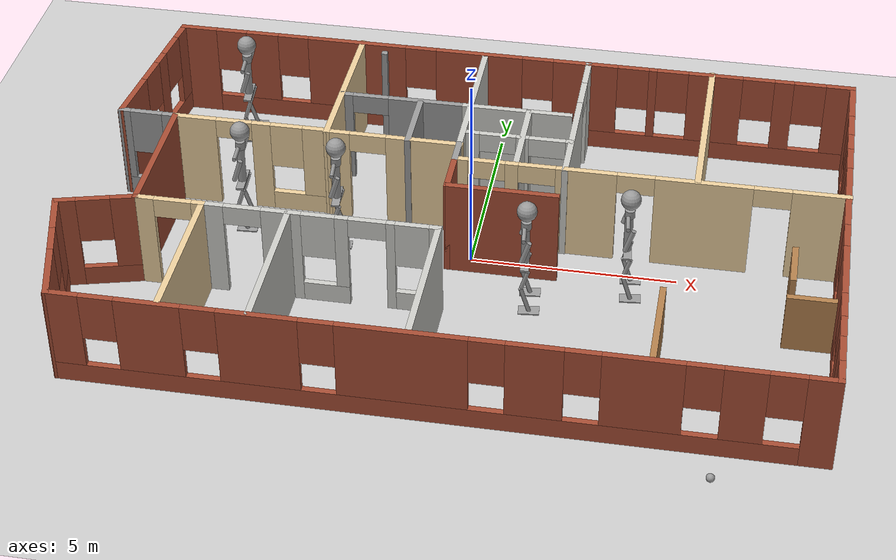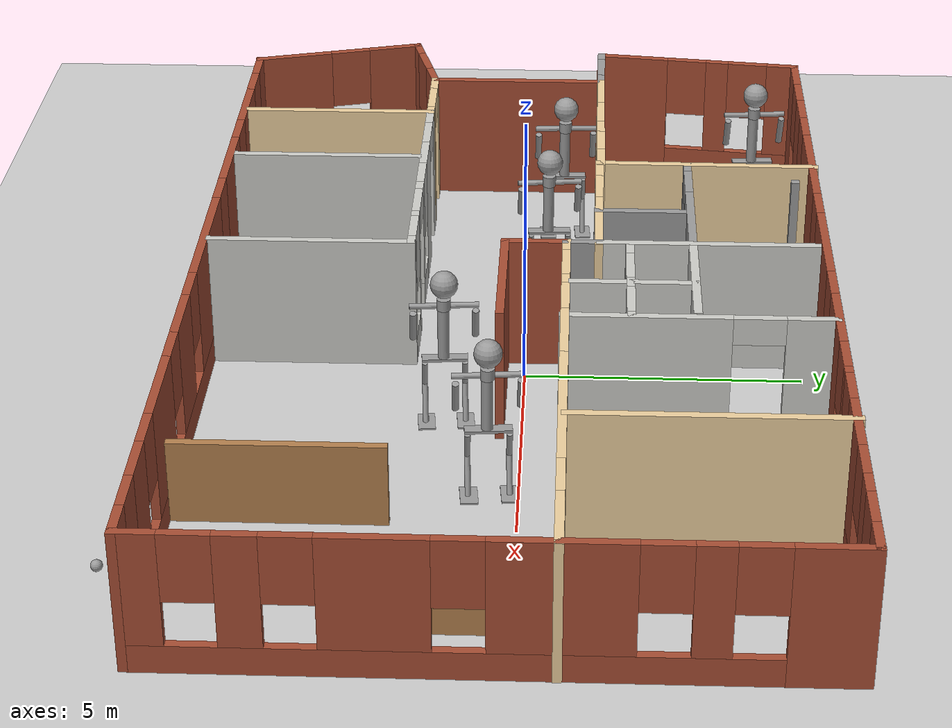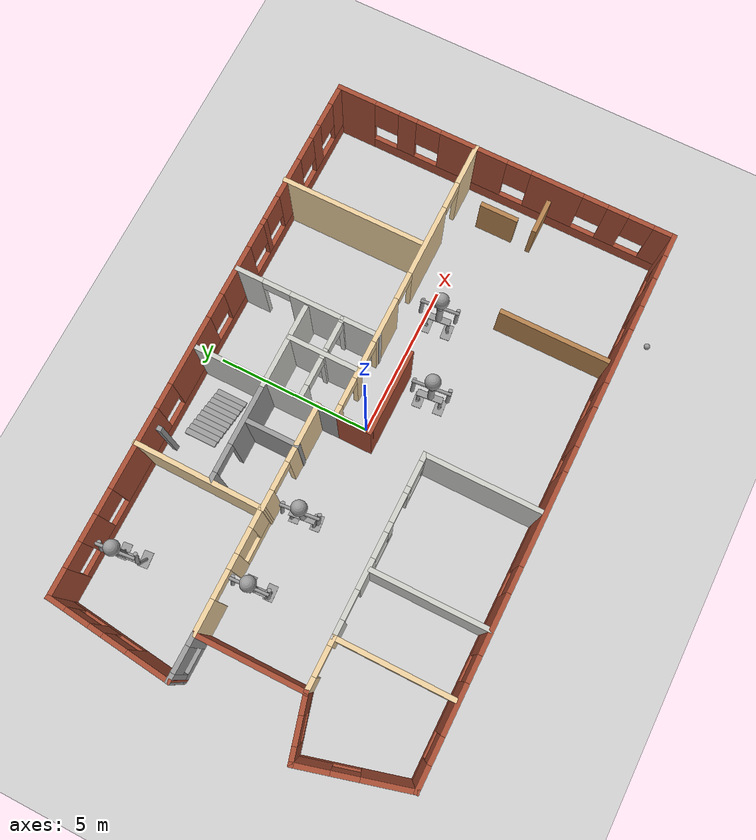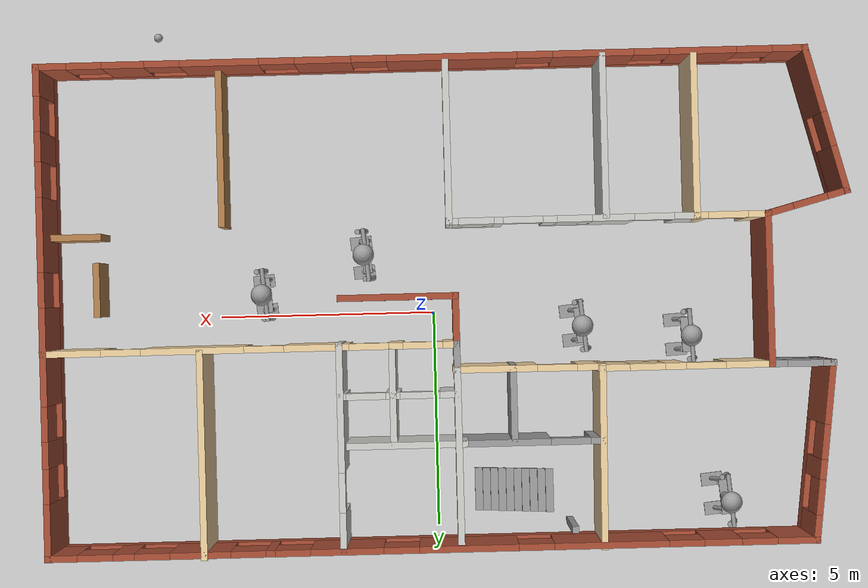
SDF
<sdf version="1.6">
 <world name="default">
  <plugin name="welcome_message" filename="libwelcome_message.so"/>
  <light name="sun" type="directional">
   <pose>0 0 10 0 -0 0</pose>
   <diffuse>0.8 0.8 0.8 1</diffuse>
   <specular>0.2 0.2 0.2 1</specular>
   <attenuation>
    <range>1000</range>
    <constant>0.9</constant>
    <linear>0.01</linear>
    <quadratic>0.001</quadratic>
   </attenuation>
   <direction>-0.5 0.1 -0.9</direction>
  </light>
  <model name="ground_plane">
   <static>1</static>
   <link name="link">
    <collision name="collision">
     <geometry><plane><normal>0 0 1</normal><size>100 100</size></plane></geometry>
     <surface><friction><ode><mu>100</mu><mu2>50</mu2></ode></friction></surface>
    </collision>
    <visual name="visual">
     <cast_shadows>0</cast_shadows>
     <geometry><plane><normal>0 0 1</normal><size>100 100</size></plane></geometry>
     <material>
      <script><uri>file://media/materials/scripts/gazebo.material</uri><name>Gazebo/Grey</name></script>
     </material>
    </visual>
   </link>
  </model>
  <gravity>0 0 -9.8</gravity>
  <magnetic_field>6e-06 2.3e-05 -4.2e-05</magnetic_field>
  <atmosphere type="adiabatic"/>
  <physics name="default_physics" default="0" type="ode">
   <max_step_size>0.001</max_step_size>
   <real_time_factor>1</real_time_factor>
   <real_time_update_rate>1000</real_time_update_rate>
  </physics>
  <scene><ambient>0.4 0.4 0.4 1</ambient><background>0.7 0.7 0.7 1</background><shadows>1</shadows></scene>
  <spherical_coordinates>
   <surface_model>EARTH_WGS84</surface_model>
   <latitude_deg>0</latitude_deg>
   <longitude_deg>0</longitude_deg>
   <elevation>0</elevation>
   <heading_deg>0</heading_deg>
  </spherical_coordinates>
  <model name="Building">
   <pose>-0.293126 -0.203944 0 0 -0 0</pose>
   <link name="Stairs_2">
    <visual name="Stairs_2_Visual_0">
     <pose>-0.680228 4.38796 0.05 0 0 -1.5708</pose>
     <geometry><box><size>1 0.18 0.1</size></box></geometry>
     <material>
      <script><uri>file://media/materials/scripts/gazebo.material</uri><name>Gazebo/Grey</name></script>
      <ambient>1 1 1 1</ambient>
     </material>
     <meta><layer>0</layer></meta>
    </visual>
    <collision name="Stairs_2_Collision_0">
     <geometry><box><size>1 0.18 0.1</size></box></geometry>
     <pose>-0.680228 4.38796 0.05 0 0 -1.5708</pose>
    </collision>
    <visual name="Stairs_2_Visual_1">
     <pose>-0.860228 4.38796 0.15 0 0 -1.5708</pose>
     <geometry><box><size>1 0.18 0.1</size></box></geometry>
     <material>
      <script><uri>file://media/materials/scripts/gazebo.material</uri><name>Gazebo/Grey</name></script>
      <ambient>1 1 1 1</ambient>
     </material>
     <meta><layer>0</layer></meta>
    </visual>
    <collision name="Stairs_2_Collision_1">
     <geometry><box><size>1 0.18 0.1</size></box></geometry>
     <pose>-0.860228 4.38796 0.15 0 0 -1.5708</pose>
    </collision>
    <visual name="Stairs_2_Visual_2">
     <pose>-1.04023 4.38796 0.25 0 0 -1.5708</pose>
     <geometry><box><size>1 0.18 0.1</size></box></geometry>
     <material>
      <script><uri>file://media/materials/scripts/gazebo.material</uri><name>Gazebo/Grey</name></script>
      <ambient>1 1 1 1</ambient>
     </material>
     <meta><layer>0</layer></meta>
    </visual>
    <collision name="Stairs_2_Collision_2">
     <geometry><box><size>1 0.18 0.1</size></box></geometry>
     <pose>-1.04023 4.38796 0.25 0 0 -1.5708</pose>
    </collision>
    <visual name="Stairs_2_Visual_3">
     <pose>-1.22023 4.38796 0.35 0 0 -1.5708</pose>
     <geometry><box><size>1 0.18 0.1</size></box></geometry>
     <material>
      <script><uri>file://media/materials/scripts/gazebo.material</uri><name>Gazebo/Grey</name></script>
      <ambient>1 1 1 1</ambient>
     </material>
     <meta><layer>0</layer></meta>
    </visual>
    <collision name="Stairs_2_Collision_3">
     <geometry><box><size>1 0.18 0.1</size></box></geometry>
     <pose>-1.22023 4.38796 0.35 0 0 -1.5708</pose>
    </collision>
    <visual name="Stairs_2_Visual_4">
     <pose>-1.40023 4.38796 0.45 0 0 -1.5708</pose>
     <geometry><box><size>1 0.18 0.1</size></box></geometry>
     <material>
      <script><uri>file://media/materials/scripts/gazebo.material</uri><name>Gazebo/Grey</name></script>
      <ambient>1 1 1 1</ambient>
     </material>
     <meta><layer>0</layer></meta>
    </visual>
    <collision name="Stairs_2_Collision_4">
     <geometry><box><size>1 0.18 0.1</size></box></geometry>
     <pose>-1.40023 4.38796 0.45 0 0 -1.5708</pose>
    </collision>
    <visual name="Stairs_2_Visual_5">
     <pose>-1.58023 4.38796 0.55 0 0 -1.5708</pose>
     <geometry><box><size>1 0.18 0.1</size></box></geometry>
     <material>
      <script><uri>file://media/materials/scripts/gazebo.material</uri><name>Gazebo/Grey</name></script>
      <ambient>1 1 1 1</ambient>
     </material>
     <meta><layer>0</layer></meta>
    </visual>
    <collision name="Stairs_2_Collision_5">
     <geometry><box><size>1 0.18 0.1</size></box></geometry>
     <pose>-1.58023 4.38796 0.55 0 0 -1.5708</pose>
    </collision>
    <visual name="Stairs_2_Visual_6">
     <pose>-1.76023 4.38796 0.65 0 0 -1.5708</pose>
     <geometry><box><size>1 0.18 0.1</size></box></geometry>
     <material>
      <script><uri>file://media/materials/scripts/gazebo.material</uri><name>Gazebo/Grey</name></script>
      <ambient>1 1 1 1</ambient>
     </material>
     <meta><layer>0</layer></meta>
    </visual>
    <collision name="Stairs_2_Collision_6">
     <geometry><box><size>1 0.18 0.1</size></box></geometry>
     <pose>-1.76023 4.38796 0.65 0 0 -1.5708</pose>
    </collision>
    <visual name="Stairs_2_Visual_7">
     <pose>-1.94023 4.38796 0.75 0 0 -1.5708</pose>
     <geometry><box><size>1 0.18 0.1</size></box></geometry>
     <material>
      <script><uri>file://media/materials/scripts/gazebo.material</uri><name>Gazebo/Grey</name></script>
      <ambient>1 1 1 1</ambient>
     </material>
     <meta><layer>0</layer></meta>
    </visual>
    <collision name="Stairs_2_Collision_7">
     <geometry><box><size>1 0.18 0.1</size></box></geometry>
     <pose>-1.94023 4.38796 0.75 0 0 -1.5708</pose>
    </collision>
    <visual name="Stairs_2_Visual_8">
     <pose>-2.12023 4.38796 0.85 0 0 -1.5708</pose>
     <geometry><box><size>1 0.18 0.1</size></box></geometry>
     <material>
      <script><uri>file://media/materials/scripts/gazebo.material</uri><name>Gazebo/Grey</name></script>
      <ambient>1 1 1 1</ambient>
     </material>
     <meta><layer>0</layer></meta>
    </visual>
    <collision name="Stairs_2_Collision_8">
     <geometry><box><size>1 0.18 0.1</size></box></geometry>
     <pose>-2.12023 4.38796 0.85 0 0 -1.5708</pose>
    </collision>
    <visual name="Stairs_2_Visual_9">
     <pose>-2.30023 4.38796 0.95 0 0 -1.5708</pose>
     <geometry><box><size>1 0.18 0.1</size></box></geometry>
     <material>
      <script><uri>file://media/materials/scripts/gazebo.material</uri><name>Gazebo/Grey</name></script>
      <ambient>1 1 1 1</ambient>
     </material>
     <meta><layer>0</layer></meta>
    </visual>
    <collision name="Stairs_2_Collision_9">
     <geometry><box><size>1 0.18 0.1</size></box></geometry>
     <pose>-2.30023 4.38796 0.95 0 0 -1.5708</pose>
    </collision>
   </link>
   <link name="Wall_0">
    <pose>0.434915 5.53865 0 0 -0 0</pose>
    <visual name="Wall_0_Visual_0">
     <pose>-8.26944 0 1.25 0 -0 0</pose>
     <geometry><box><size>0.961111 0.15 2.5</size></box></geometry>
     <material>
      <script><uri>file://media/materials/scripts/gazebo.material</uri><name>Gazebo/Bricks</name></script>
      <ambient>1 1 1 1</ambient>
     </material>
     <meta><layer>0</layer></meta>
    </visual>
    <collision name="Wall_0_Collision_0">
     <geometry><box><size>0.961111 0.15 2.5</size></box></geometry>
     <pose>-8.26944 0 1.25 0 -0 0</pose>
    </collision>
    <visual name="Wall_0_Visual_1">
     <pose>0.480555 0 0.25 0 -0 0</pose>
     <geometry><box><size>16.5389 0.15 0.5</size></box></geometry>
     <material>
      <script><uri>file://media/materials/scripts/gazebo.material</uri><name>Gazebo/Bricks</name></script>
      <ambient>1 1 1 1</ambient>
     </material>
     <meta><layer>0</layer></meta>
    </visual>
    <collision name="Wall_0_Collision_1">
     <geometry><box><size>16.5389 0.15 0.5</size></box></geometry>
     <pose>0.480555 0 0.25 0 -0 0</pose>
    </collision>
    <visual name="Wall_0_Visual_2">
     <pose>-6.56423 0 1.5 0 -0 0</pose>
     <geometry><box><size>0.849313 0.15 2</size></box></geometry>
     <material>
      <script><uri>file://media/materials/scripts/gazebo.material</uri><name>Gazebo/Bricks</name></script>
      <ambient>1 1 1 1</ambient>
     </material>
     <meta><layer>0</layer></meta>
    </visual>
    <collision name="Wall_0_Collision_2">
     <geometry><box><size>0.849313 0.15 2</size></box></geometry>
     <pose>-6.56423 0 1.5 0 -0 0</pose>
    </collision>
    <visual name="Wall_0_Visual_3">
     <pose>-4.04638 0 1.5 0 -0 0</pose>
     <geometry><box><size>2.5864 0.15 2</size></box></geometry>
     <material>
      <script><uri>file://media/materials/scripts/gazebo.material</uri><name>Gazebo/Bricks</name></script>
      <ambient>1 1 1 1</ambient>
     </material>
     <meta><layer>0</layer></meta>
    </visual>
    <collision name="Wall_0_Collision_3">
     <geometry><box><size>2.5864 0.15 2</size></box></geometry>
     <pose>-4.04638 0 1.5 0 -0 0</pose>
    </collision>
    <visual name="Wall_0_Visual_4">
     <pose>-0.828204 0 1.5 0 -0 0</pose>
     <geometry><box><size>2.24994 0.15 2</size></box></geometry>
     <material>
      <script><uri>file://media/materials/scripts/gazebo.material</uri><name>Gazebo/Bricks</name></script>
      <ambient>1 1 1 1</ambient>
     </material>
     <meta><layer>0</layer></meta>
    </visual>
    <collision name="Wall_0_Collision_4">
     <geometry><box><size>2.24994 0.15 2</size></box></geometry>
     <pose>-0.828204 0 1.5 0 -0 0</pose>
    </collision>
    <visual name="Wall_0_Visual_5">
     <pose>1.92369 0 1.5 0 -0 0</pose>
     <geometry><box><size>1.65386 0.15 2</size></box></geometry>
     <material>
      <script><uri>file://media/materials/scripts/gazebo.material</uri><name>Gazebo/Bricks</name></script>
      <ambient>1 1 1 1</ambient>
     </material>
     <meta><layer>0</layer></meta>
    </visual>
    <collision name="Wall_0_Collision_5">
     <geometry><box><size>1.65386 0.15 2</size></box></geometry>
     <pose>1.92369 0 1.5 0 -0 0</pose>
    </collision>
    <visual name="Wall_0_Visual_6">
     <pose>3.65346 0 1.5 0 -0 0</pose>
     <geometry><box><size>0.205679 0.15 2</size></box></geometry>
     <material>
      <script><uri>file://media/materials/scripts/gazebo.material</uri><name>Gazebo/Bricks</name></script>
      <ambient>1 1 1 1</ambient>
     </material>
     <meta><layer>0</layer></meta>
    </visual>
    <collision name="Wall_0_Collision_6">
     <geometry><box><size>0.205679 0.15 2</size></box></geometry>
     <pose>3.65346 0 1.5 0 -0 0</pose>
    </collision>
    <visual name="Wall_0_Visual_7">
     <pose>5.24243 0 1.5 0 -0 0</pose>
     <geometry><box><size>1.37227 0.15 2</size></box></geometry>
     <material>
      <script><uri>file://media/materials/scripts/gazebo.material</uri><name>Gazebo/Bricks</name></script>
      <ambient>1 1 1 1</ambient>
     </material>
     <meta><layer>0</layer></meta>
    </visual>
    <collision name="Wall_0_Collision_7">
     <geometry><box><size>1.37227 0.15 2</size></box></geometry>
     <pose>5.24243 0 1.5 0 -0 0</pose>
    </collision>
    <visual name="Wall_0_Visual_8">
     <pose>6.9722 0 1.5 0 -0 0</pose>
     <geometry><box><size>0.487269 0.15 2</size></box></geometry>
     <material>
      <script><uri>file://media/materials/scripts/gazebo.material</uri><name>Gazebo/Bricks</name></script>
      <ambient>1 1 1 1</ambient>
     </material>
     <meta><layer>0</layer></meta>
    </visual>
    <collision name="Wall_0_Collision_8">
     <geometry><box><size>0.487269 0.15 2</size></box></geometry>
     <pose>6.9722 0 1.5 0 -0 0</pose>
    </collision>
    <visual name="Wall_0_Visual_9">
     <pose>8.38292 0 1.5 0 -0 0</pose>
     <geometry><box><size>0.734164 0.15 2</size></box></geometry>
     <material>
      <script><uri>file://media/materials/scripts/gazebo.material</uri><name>Gazebo/Bricks</name></script>
      <ambient>1 1 1 1</ambient>
     </material>
     <meta><layer>0</layer></meta>
    </visual>
    <collision name="Wall_0_Collision_9">
     <geometry><box><size>0.734164 0.15 2</size></box></geometry>
     <pose>8.38292 0 1.5 0 -0 0</pose>
    </collision>
    <visual name="Wall_0_Visual_10">
     <pose>-7.38889 0 1.9 0 -0 0</pose>
     <geometry><box><size>0.8 0.15 1.2</size></box></geometry>
     <material>
      <script><uri>file://media/materials/scripts/gazebo.material</uri><name>Gazebo/Bricks</name></script>
      <ambient>1 1 1 1</ambient>
     </material>
     <meta><layer>0</layer></meta>
    </visual>
    <collision name="Wall_0_Collision_10">
     <geometry><box><size>0.8 0.15 1.2</size></box></geometry>
     <pose>-7.38889 0 1.9 0 -0 0</pose>
    </collision>
    <visual name="Wall_0_Visual_11">
     <pose>-5.73958 0 1.9 0 -0 0</pose>
     <geometry><box><size>0.8 0.15 1.2</size></box></geometry>
     <material>
      <script><uri>file://media/materials/scripts/gazebo.material</uri><name>Gazebo/Bricks</name></script>
      <ambient>1 1 1 1</ambient>
     </material>
     <meta><layer>0</layer></meta>
    </visual>
    <collision name="Wall_0_Collision_11">
     <geometry><box><size>0.8 0.15 1.2</size></box></geometry>
     <pose>-5.73958 0 1.9 0 -0 0</pose>
    </collision>
    <visual name="Wall_0_Visual_12">
     <pose>-2.35317 0 1.9 0 -0 0</pose>
     <geometry><box><size>0.8 0.15 1.2</size></box></geometry>
     <material>
      <script><uri>file://media/materials/scripts/gazebo.material</uri><name>Gazebo/Bricks</name></script>
      <ambient>1 1 1 1</ambient>
     </material>
     <meta><layer>0</layer></meta>
    </visual>
    <collision name="Wall_0_Collision_12">
     <geometry><box><size>0.8 0.15 1.2</size></box></geometry>
     <pose>-2.35317 0 1.9 0 -0 0</pose>
    </collision>
    <visual name="Wall_0_Visual_13">
     <pose>0.696767 0 1.9 0 -0 0</pose>
     <geometry><box><size>0.8 0.15 1.2</size></box></geometry>
     <material>
      <script><uri>file://media/materials/scripts/gazebo.material</uri><name>Gazebo/Bricks</name></script>
      <ambient>1 1 1 1</ambient>
     </material>
     <meta><layer>0</layer></meta>
    </visual>
    <collision name="Wall_0_Collision_13">
     <geometry><box><size>0.8 0.15 1.2</size></box></geometry>
     <pose>0.696767 0 1.9 0 -0 0</pose>
    </collision>
    <visual name="Wall_0_Visual_14">
     <pose>3.15062 0 1.9 0 -0 0</pose>
     <geometry><box><size>0.8 0.15 1.2</size></box></geometry>
     <material>
      <script><uri>file://media/materials/scripts/gazebo.material</uri><name>Gazebo/Bricks</name></script>
      <ambient>1 1 1 1</ambient>
     </material>
     <meta><layer>0</layer></meta>
    </visual>
    <collision name="Wall_0_Collision_14">
     <geometry><box><size>0.8 0.15 1.2</size></box></geometry>
     <pose>3.15062 0 1.9 0 -0 0</pose>
    </collision>
    <visual name="Wall_0_Visual_15">
     <pose>4.1563 0 1.9 0 -0 0</pose>
     <geometry><box><size>0.8 0.15 1.2</size></box></geometry>
     <material>
      <script><uri>file://media/materials/scripts/gazebo.material</uri><name>Gazebo/Bricks</name></script>
      <ambient>1 1 1 1</ambient>
     </material>
     <meta><layer>0</layer></meta>
    </visual>
    <collision name="Wall_0_Collision_15">
     <geometry><box><size>0.8 0.15 1.2</size></box></geometry>
     <pose>4.1563 0 1.9 0 -0 0</pose>
    </collision>
    <visual name="Wall_0_Visual_16">
     <pose>6.32857 0 1.9 0 -0 0</pose>
     <geometry><box><size>0.8 0.15 1.2</size></box></geometry>
     <material>
      <script><uri>file://media/materials/scripts/gazebo.material</uri><name>Gazebo/Bricks</name></script>
      <ambient>1 1 1 1</ambient>
     </material>
     <meta><layer>0</layer></meta>
    </visual>
    <collision name="Wall_0_Collision_16">
     <geometry><box><size>0.8 0.15 1.2</size></box></geometry>
     <pose>6.32857 0 1.9 0 -0 0</pose>
    </collision>
    <visual name="Wall_0_Visual_17">
     <pose>7.61584 0 1.9 0 -0 0</pose>
     <geometry><box><size>0.8 0.15 1.2</size></box></geometry>
     <material>
      <script><uri>file://media/materials/scripts/gazebo.material</uri><name>Gazebo/Bricks</name></script>
      <ambient>1 1 1 1</ambient>
     </material>
     <meta><layer>0</layer></meta>
    </visual>
    <collision name="Wall_0_Collision_17">
     <geometry><box><size>0.8 0.15 1.2</size></box></geometry>
     <pose>7.61584 0 1.9 0 -0 0</pose>
    </collision>
   </link>
   <link name="Wall_11">
    <pose>-6.52017 -1.84669 0 0 -0 0</pose>
    <visual name="Wall_11_Visual_0">
     <pose>-0.613993 0 1.25 0 -0 0</pose>
     <geometry><box><size>0.522013 0.15 2.5</size></box></geometry>
     <material>
      <script><uri>file://media/materials/scripts/gazebo.material</uri><name>Gazebo/Grey</name></script>
      <ambient>0.921569 0.807843 0.615686 1</ambient>
     </material>
     <meta><layer>0</layer></meta>
    </visual>
    <collision name="Wall_11_Collision_0">
     <geometry><box><size>0.522013 0.15 2.5</size></box></geometry>
     <pose>-0.613993 0 1.25 0 -0 0</pose>
    </collision>
    <visual name="Wall_11_Visual_1">
     <pose>0.711007 0 1.25 0 -0 0</pose>
     <geometry><box><size>0.327987 0.15 2.5</size></box></geometry>
     <material>
      <script><uri>file://media/materials/scripts/gazebo.material</uri><name>Gazebo/Grey</name></script>
      <ambient>0.921569 0.807843 0.615686 1</ambient>
     </material>
     <meta><layer>0</layer></meta>
    </visual>
    <collision name="Wall_11_Collision_1">
     <geometry><box><size>0.327987 0.15 2.5</size></box></geometry>
     <pose>0.711007 0 1.25 0 -0 0</pose>
    </collision>
    <visual name="Wall_11_Visual_2">
     <pose>0.097013 0 2.25 0 -0 0</pose>
     <geometry><box><size>0.9 0.15 0.5</size></box></geometry>
     <material>
      <script><uri>file://media/materials/scripts/gazebo.material</uri><name>Gazebo/Grey</name></script>
      <ambient>0.921569 0.807843 0.615686 1</ambient>
     </material>
     <meta><layer>0</layer></meta>
    </visual>
    <collision name="Wall_11_Collision_2">
     <geometry><box><size>0.9 0.15 0.5</size></box></geometry>
     <pose>0.097013 0 2.25 0 -0 0</pose>
    </collision>
   </link>
   <link name="Wall_12">
    <collision name="Wall_12_Collision">
     <geometry><box><size>3.75 0.15 2.5</size></box></geometry>
     <pose>0 0 1.25 0 -0 0</pose>
    </collision>
    <visual name="Wall_12_Visual">
     <pose>0 0 1.25 0 -0 0</pose>
     <geometry><box><size>3.75 0.15 2.5</size></box></geometry>
     <material>
      <script><uri>file://media/materials/scripts/gazebo.material</uri><name>Gazebo/Grey</name></script>
      <ambient>0.921569 0.807843 0.615686 1</ambient>
     </material>
     <meta><layer>0</layer></meta>
    </visual>
    <pose>-5.72017 -3.64669 0 0 0 -1.5708</pose>
   </link>
   <link name="Wall_14">
    <pose>-2.92017 -1.84669 0 0 -0 0</pose>
    <visual name="Wall_14_Visual_0">
     <pose>-2.58082 0 1.25 0 -0 0</pose>
     <geometry><box><size>0.588363 0.15 2.5</size></box></geometry>
     <material>
      <script><uri>file://media/materials/scripts/gazebo.material</uri><name>Gazebo/CeilingTiled</name></script>
      <ambient>0.921569 0.807843 0.615686 1</ambient>
     </material>
     <meta><layer>0</layer></meta>
    </visual>
    <collision name="Wall_14_Collision_0">
     <geometry><box><size>0.588363 0.15 2.5</size></box></geometry>
     <pose>-2.58082 0 1.25 0 -0 0</pose>
    </collision>
    <visual name="Wall_14_Visual_1">
     <pose>-0.912337 0 1.25 0 -0 0</pose>
     <geometry><box><size>0.9486 0.15 2.5</size></box></geometry>
     <material>
      <script><uri>file://media/materials/scripts/gazebo.material</uri><name>Gazebo/CeilingTiled</name></script>
      <ambient>0.921569 0.807843 0.615686 1</ambient>
     </material>
     <meta><layer>0</layer></meta>
    </visual>
    <collision name="Wall_14_Collision_1">
     <geometry><box><size>0.9486 0.15 2.5</size></box></geometry>
     <pose>-0.912337 0 1.25 0 -0 0</pose>
    </collision>
    <visual name="Wall_14_Visual_2">
     <pose>1.67976 0 1.25 0 -0 0</pose>
     <geometry><box><size>0.208 0.15 2.5</size></box></geometry>
     <material>
      <script><uri>file://media/materials/scripts/gazebo.material</uri><name>Gazebo/CeilingTiled</name></script>
      <ambient>0.921569 0.807843 0.615686 1</ambient>
     </material>
     <meta><layer>0</layer></meta>
    </visual>
    <collision name="Wall_14_Collision_2">
     <geometry><box><size>0.208 0.15 2.5</size></box></geometry>
     <pose>1.67976 0 1.25 0 -0 0</pose>
    </collision>
    <visual name="Wall_14_Visual_3">
     <pose>0.118863 0 0.25 0 -0 0</pose>
     <geometry><box><size>1.1138 0.15 0.5</size></box></geometry>
     <material>
      <script><uri>file://media/materials/scripts/gazebo.material</uri><name>Gazebo/CeilingTiled</name></script>
      <ambient>0.921569 0.807843 0.615686 1</ambient>
     </material>
     <meta><layer>0</layer></meta>
    </visual>
    <collision name="Wall_14_Collision_3">
     <geometry><box><size>1.1138 0.15 0.5</size></box></geometry>
     <pose>0.118863 0 0.25 0 -0 0</pose>
    </collision>
    <visual name="Wall_14_Visual_4">
     <pose>2.32938 0 0.25 0 -0 0</pose>
     <geometry><box><size>1.09124 0.15 0.5</size></box></geometry>
     <material>
      <script><uri>file://media/materials/scripts/gazebo.material</uri><name>Gazebo/CeilingTiled</name></script>
      <ambient>0.921569 0.807843 0.615686 1</ambient>
     </material>
     <meta><layer>0</layer></meta>
    </visual>
    <collision name="Wall_14_Collision_4">
     <geometry><box><size>1.09124 0.15 0.5</size></box></geometry>
     <pose>2.32938 0 0.25 0 -0 0</pose>
    </collision>
    <visual name="Wall_14_Visual_5">
     <pose>0.518863 0 1.5 0 -0 0</pose>
     <geometry><box><size>0.3138 0.15 2</size></box></geometry>
     <material>
      <script><uri>file://media/materials/scripts/gazebo.material</uri><name>Gazebo/CeilingTiled</name></script>
      <ambient>0.921569 0.807843 0.615686 1</ambient>
     </material>
     <meta><layer>0</layer></meta>
    </visual>
    <collision name="Wall_14_Collision_5">
     <geometry><box><size>0.3138 0.15 2</size></box></geometry>
     <pose>0.518863 0 1.5 0 -0 0</pose>
    </collision>
    <visual name="Wall_14_Visual_6">
     <pose>0.518863 0 1.5 0 -0 0</pose>
     <geometry><box><size>0.3138 0.15 2</size></box></geometry>
     <material>
      <script><uri>file://media/materials/scripts/gazebo.material</uri><name>Gazebo/CeilingTiled</name></script>
      <ambient>0.921569 0.807843 0.615686 1</ambient>
     </material>
     <meta><layer>0</layer></meta>
    </visual>
    <collision name="Wall_14_Collision_6">
     <geometry><box><size>0.3138 0.15 2</size></box></geometry>
     <pose>0.518863 0 1.5 0 -0 0</pose>
    </collision>
    <visual name="Wall_14_Visual_7">
     <pose>2.72938 0 1.5 0 -0 0</pose>
     <geometry><box><size>0.291237 0.15 2</size></box></geometry>
     <material>
      <script><uri>file://media/materials/scripts/gazebo.material</uri><name>Gazebo/CeilingTiled</name></script>
      <ambient>0.921569 0.807843 0.615686 1</ambient>
     </material>
     <meta><layer>0</layer></meta>
    </visual>
    <collision name="Wall_14_Collision_7">
     <geometry><box><size>0.291237 0.15 2</size></box></geometry>
     <pose>2.72938 0 1.5 0 -0 0</pose>
    </collision>
    <visual name="Wall_14_Visual_8">
     <pose>-0.038037 0 1.9 0 -0 0</pose>
     <geometry><box><size>0.8 0.15 1.2</size></box></geometry>
     <material>
      <script><uri>file://media/materials/scripts/gazebo.material</uri><name>Gazebo/CeilingTiled</name></script>
      <ambient>0.921569 0.807843 0.615686 1</ambient>
     </material>
     <meta><layer>0</layer></meta>
    </visual>
    <collision name="Wall_14_Collision_8">
     <geometry><box><size>0.8 0.15 1.2</size></box></geometry>
     <pose>-0.038037 0 1.9 0 -0 0</pose>
    </collision>
    <visual name="Wall_14_Visual_9">
     <pose>2.18376 0 1.9 0 -0 0</pose>
     <geometry><box><size>0.8 0.15 1.2</size></box></geometry>
     <material>
      <script><uri>file://media/materials/scripts/gazebo.material</uri><name>Gazebo/CeilingTiled</name></script>
      <ambient>0.921569 0.807843 0.615686 1</ambient>
     </material>
     <meta><layer>0</layer></meta>
    </visual>
    <collision name="Wall_14_Collision_9">
     <geometry><box><size>0.8 0.15 1.2</size></box></geometry>
     <pose>2.18376 0 1.9 0 -0 0</pose>
    </collision>
    <visual name="Wall_14_Visual_10">
     <pose>-1.83664 0 2.25 0 -0 0</pose>
     <geometry><box><size>0.9 0.15 0.5</size></box></geometry>
     <material>
      <script><uri>file://media/materials/scripts/gazebo.material</uri><name>Gazebo/CeilingTiled</name></script>
      <ambient>0.921569 0.807843 0.615686 1</ambient>
     </material>
     <meta><layer>0</layer></meta>
    </visual>
    <collision name="Wall_14_Collision_10">
     <geometry><box><size>0.9 0.15 0.5</size></box></geometry>
     <pose>-1.83664 0 2.25 0 -0 0</pose>
    </collision>
    <visual name="Wall_14_Visual_11">
     <pose>1.12576 0 2.25 0 -0 0</pose>
     <geometry><box><size>0.9 0.15 0.5</size></box></geometry>
     <material>
      <script><uri>file://media/materials/scripts/gazebo.material</uri><name>Gazebo/CeilingTiled</name></script>
      <ambient>0.921569 0.807843 0.615686 1</ambient>
     </material>
     <meta><layer>0</layer></meta>
    </visual>
    <collision name="Wall_14_Collision_11">
     <geometry><box><size>0.9 0.15 0.5</size></box></geometry>
     <pose>1.12576 0 2.25 0 -0 0</pose>
    </collision>
    <visual name="Wall_14_Visual_12">
     <pose>1.12576 0 2.25 0 -0 0</pose>
     <geometry><box><size>0.9 0.15 0.5</size></box></geometry>
     <material>
      <script><uri>file://media/materials/scripts/gazebo.material</uri><name>Gazebo/CeilingTiled</name></script>
      <ambient>0.921569 0.807843 0.615686 1</ambient>
     </material>
     <meta><layer>0</layer></meta>
    </visual>
    <collision name="Wall_14_Collision_12">
     <geometry><box><size>0.9 0.15 0.5</size></box></geometry>
     <pose>1.12576 0 2.25 0 -0 0</pose>
    </collision>
   </link>
   <link name="Wall_15">
    <collision name="Wall_15_Collision">
     <geometry><box><size>3.75 0.15 2.5</size></box></geometry>
     <pose>0 0 1.25 0 -0 0</pose>
    </collision>
    <visual name="Wall_15_Visual">
     <pose>0 0 1.25 0 -0 0</pose>
     <geometry><box><size>3.75 0.15 2.5</size></box></geometry>
     <material>
      <script><uri>file://media/materials/scripts/gazebo.material</uri><name>Gazebo/CeilingTiled</name></script>
      <ambient>0.921569 0.807843 0.615686 1</ambient>
     </material>
     <meta><layer>0</layer></meta>
    </visual>
    <pose>-0.120167 -3.64669 0 0 0 -1.5708</pose>
   </link>
   <link name="Wall_19">
    <collision name="Wall_19_Collision">
     <geometry><box><size>3.75 0.15 2.5</size></box></geometry>
     <pose>0 0 1.25 0 -0 0</pose>
    </collision>
    <visual name="Wall_19_Visual">
     <pose>0 0 1.25 0 -0 0</pose>
     <geometry><box><size>3.75 0.15 2.5</size></box></geometry>
     <material>
      <script><uri>file://media/materials/scripts/gazebo.material</uri><name>Gazebo/CeilingTiled</name></script>
      <ambient>0.921569 0.807843 0.615686 1</ambient>
     </material>
     <meta><layer>0</layer></meta>
    </visual>
    <pose>-3.66538 -3.70743 0 0 0 -1.5708</pose>
   </link>
   <link name="Wall_2">
    <pose>9.10991 -0.011353 0 0 0 -1.5708</pose>
    <visual name="Wall_2_Visual_0">
     <pose>-4.96991 0 1.25 0 -0 0</pose>
     <geometry><box><size>1.31017 0.15 2.5</size></box></geometry>
     <material>
      <script><uri>file://media/materials/scripts/gazebo.material</uri><name>Gazebo/Bricks</name></script>
      <ambient>0 0.666667 0.498039 1</ambient>
     </material>
     <meta><layer>0</layer></meta>
    </visual>
    <collision name="Wall_2_Collision_0">
     <geometry><box><size>1.31017 0.15 2.5</size></box></geometry>
     <pose>-4.96991 0 1.25 0 -0 0</pose>
    </collision>
    <visual name="Wall_2_Visual_1">
     <pose>0.655087 0 0.25 0 -0 0</pose>
     <geometry><box><size>9.93983 0.15 0.5</size></box></geometry>
     <material>
      <script><uri>file://media/materials/scripts/gazebo.material</uri><name>Gazebo/Bricks</name></script>
      <ambient>0 0.666667 0.498039 1</ambient>
     </material>
     <meta><layer>0</layer></meta>
    </visual>
    <collision name="Wall_2_Collision_1">
     <geometry><box><size>9.93983 0.15 0.5</size></box></geometry>
     <pose>0.655087 0 0.25 0 -0 0</pose>
    </collision>
    <visual name="Wall_2_Visual_2">
     <pose>-3.21085 0 1.5 0 -0 0</pose>
     <geometry><box><size>0.60795 0.15 2</size></box></geometry>
     <material>
      <script><uri>file://media/materials/scripts/gazebo.material</uri><name>Gazebo/Bricks</name></script>
      <ambient>0 0.666667 0.498039 1</ambient>
     </material>
     <meta><layer>0</layer></meta>
    </visual>
    <collision name="Wall_2_Collision_2">
     <geometry><box><size>0.60795 0.15 2</size></box></geometry>
     <pose>-3.21085 0 1.5 0 -0 0</pose>
    </collision>
    <visual name="Wall_2_Visual_3">
     <pose>-0.992199 0 1.5 0 -0 0</pose>
     <geometry><box><size>2.22935 0.15 2</size></box></geometry>
     <material>
      <script><uri>file://media/materials/scripts/gazebo.material</uri><name>Gazebo/Bricks</name></script>
      <ambient>0 0.666667 0.498039 1</ambient>
     </material>
     <meta><layer>0</layer></meta>
    </visual>
    <collision name="Wall_2_Collision_3">
     <geometry><box><size>2.22935 0.15 2</size></box></geometry>
     <pose>-0.992199 0 1.5 0 -0 0</pose>
    </collision>
    <visual name="Wall_2_Visual_4">
     <pose>1.77153 0 1.5 0 -0 0</pose>
     <geometry><box><size>1.69811 0.15 2</size></box></geometry>
     <material>
      <script><uri>file://media/materials/scripts/gazebo.material</uri><name>Gazebo/Bricks</name></script>
      <ambient>0 0.666667 0.498039 1</ambient>
     </material>
     <meta><layer>0</layer></meta>
    </visual>
    <collision name="Wall_2_Collision_4">
     <geometry><box><size>1.69811 0.15 2</size></box></geometry>
     <pose>1.77153 0 1.5 0 -0 0</pose>
    </collision>
    <visual name="Wall_2_Visual_5">
     <pose>3.76076 0 1.5 0 -0 0</pose>
     <geometry><box><size>0.680358 0.15 2</size></box></geometry>
     <material>
      <script><uri>file://media/materials/scripts/gazebo.material</uri><name>Gazebo/Bricks</name></script>
      <ambient>0 0.666667 0.498039 1</ambient>
     </material>
     <meta><layer>0</layer></meta>
    </visual>
    <collision name="Wall_2_Collision_5">
     <geometry><box><size>0.680358 0.15 2</size></box></geometry>
     <pose>3.76076 0 1.5 0 -0 0</pose>
    </collision>
    <visual name="Wall_2_Visual_6">
     <pose>5.26297 0 1.5 0 -0 0</pose>
     <geometry><box><size>0.724057 0.15 2</size></box></geometry>
     <material>
      <script><uri>file://media/materials/scripts/gazebo.material</uri><name>Gazebo/Bricks</name></script>
      <ambient>0 0.666667 0.498039 1</ambient>
     </material>
     <meta><layer>0</layer></meta>
    </visual>
    <collision name="Wall_2_Collision_6">
     <geometry><box><size>0.724057 0.15 2</size></box></geometry>
     <pose>5.26297 0 1.5 0 -0 0</pose>
    </collision>
    <visual name="Wall_2_Visual_7">
     <pose>-3.91483 0 1.9 0 -0 0</pose>
     <geometry><box><size>0.8 0.15 1.2</size></box></geometry>
     <material>
      <script><uri>file://media/materials/scripts/gazebo.material</uri><name>Gazebo/Bricks</name></script>
      <ambient>0 0.666667 0.498039 1</ambient>
     </material>
     <meta><layer>0</layer></meta>
    </visual>
    <collision name="Wall_2_Collision_7">
     <geometry><box><size>0.8 0.15 1.2</size></box></geometry>
     <pose>-3.91483 0 1.9 0 -0 0</pose>
    </collision>
    <visual name="Wall_2_Visual_8">
     <pose>-2.50688 0 1.9 0 -0 0</pose>
     <geometry><box><size>0.8 0.15 1.2</size></box></geometry>
     <material>
      <script><uri>file://media/materials/scripts/gazebo.material</uri><name>Gazebo/Bricks</name></script>
      <ambient>0 0.666667 0.498039 1</ambient>
     </material>
     <meta><layer>0</layer></meta>
    </visual>
    <collision name="Wall_2_Collision_8">
     <geometry><box><size>0.8 0.15 1.2</size></box></geometry>
     <pose>-2.50688 0 1.9 0 -0 0</pose>
    </collision>
    <visual name="Wall_2_Visual_9">
     <pose>0.522479 0 1.9 0 -0 0</pose>
     <geometry><box><size>0.8 0.15 1.2</size></box></geometry>
     <material>
      <script><uri>file://media/materials/scripts/gazebo.material</uri><name>Gazebo/Bricks</name></script>
      <ambient>0 0.666667 0.498039 1</ambient>
     </material>
     <meta><layer>0</layer></meta>
    </visual>
    <collision name="Wall_2_Collision_9">
     <geometry><box><size>0.8 0.15 1.2</size></box></geometry>
     <pose>0.522479 0 1.9 0 -0 0</pose>
    </collision>
    <visual name="Wall_2_Visual_10">
     <pose>3.02059 0 1.9 0 -0 0</pose>
     <geometry><box><size>0.8 0.15 1.2</size></box></geometry>
     <material>
      <script><uri>file://media/materials/scripts/gazebo.material</uri><name>Gazebo/Bricks</name></script>
      <ambient>0 0.666667 0.498039 1</ambient>
     </material>
     <meta><layer>0</layer></meta>
    </visual>
    <collision name="Wall_2_Collision_10">
     <geometry><box><size>0.8 0.15 1.2</size></box></geometry>
     <pose>3.02059 0 1.9 0 -0 0</pose>
    </collision>
    <visual name="Wall_2_Visual_11">
     <pose>4.50094 0 1.9 0 -0 0</pose>
     <geometry><box><size>0.8 0.15 1.2</size></box></geometry>
     <material>
      <script><uri>file://media/materials/scripts/gazebo.material</uri><name>Gazebo/Bricks</name></script>
      <ambient>0 0.666667 0.498039 1</ambient>
     </material>
     <meta><layer>0</layer></meta>
    </visual>
    <collision name="Wall_2_Collision_11">
     <geometry><box><size>0.8 0.15 1.2</size></box></geometry>
     <pose>4.50094 0 1.9 0 -0 0</pose>
    </collision>
   </link>
   <link name="Wall_21">
    <collision name="Wall_21_Collision">
     <geometry><box><size>3.75 0.15 1.5</size></box></geometry>
     <pose>0 0 0.75 0 -0 0</pose>
    </collision>
    <visual name="Wall_21_Visual">
     <pose>0 0 0.75 0 -0 0</pose>
     <geometry><box><size>3.75 0.15 1.5</size></box></geometry>
     <material>
      <script><uri>file://media/materials/scripts/gazebo.material</uri><name>Gazebo/Wood</name></script>
      <ambient>1 1 1 1</ambient>
     </material>
     <meta><layer>0</layer></meta>
    </visual>
    <pose>5.09526 -3.75796 0 0 -0 1.5708</pose>
   </link>
   <link name="Wall_23">
    <pose>-5.40433 1.5402 0 0 -0 0</pose>
    <visual name="Wall_23_Visual_0">
     <pose>-1.44346 0 1.25 0 -0 0</pose>
     <geometry><box><size>1.11308 0.15 2.5</size></box></geometry>
     <material>
      <script><uri>file://media/materials/scripts/gazebo.material</uri><name>Gazebo/Grey</name></script>
      <ambient>0.921569 0.807843 0.615686 1</ambient>
     </material>
     <meta><layer>0</layer></meta>
    </visual>
    <collision name="Wall_23_Collision_0">
     <geometry><box><size>1.11308 0.15 2.5</size></box></geometry>
     <pose>-1.44346 0 1.25 0 -0 0</pose>
    </collision>
    <visual name="Wall_23_Visual_1">
     <pose>0.249326 0 1.25 0 -0 0</pose>
     <geometry><box><size>0.4725 0.15 2.5</size></box></geometry>
     <material>
      <script><uri>file://media/materials/scripts/gazebo.material</uri><name>Gazebo/Grey</name></script>
      <ambient>0.921569 0.807843 0.615686 1</ambient>
     </material>
     <meta><layer>0</layer></meta>
    </visual>
    <collision name="Wall_23_Collision_1">
     <geometry><box><size>0.4725 0.15 2.5</size></box></geometry>
     <pose>0.249326 0 1.25 0 -0 0</pose>
    </collision>
    <visual name="Wall_23_Visual_2">
     <pose>1.24279 0 0.25 0 -0 0</pose>
     <geometry><box><size>1.51442 0.15 0.5</size></box></geometry>
     <material>
      <script><uri>file://media/materials/scripts/gazebo.material</uri><name>Gazebo/Grey</name></script>
      <ambient>0.921569 0.807843 0.615686 1</ambient>
     </material>
     <meta><layer>0</layer></meta>
    </visual>
    <collision name="Wall_23_Collision_2">
     <geometry><box><size>1.51442 0.15 0.5</size></box></geometry>
     <pose>1.24279 0 0.25 0 -0 0</pose>
    </collision>
    <visual name="Wall_23_Visual_3">
     <pose>1.64279 0 1.5 0 -0 0</pose>
     <geometry><box><size>0.714424 0.15 2</size></box></geometry>
     <material>
      <script><uri>file://media/materials/scripts/gazebo.material</uri><name>Gazebo/Grey</name></script>
      <ambient>0.921569 0.807843 0.615686 1</ambient>
     </material>
     <meta><layer>0</layer></meta>
    </visual>
    <collision name="Wall_23_Collision_3">
     <geometry><box><size>0.714424 0.15 2</size></box></geometry>
     <pose>1.64279 0 1.5 0 -0 0</pose>
    </collision>
    <visual name="Wall_23_Visual_4">
     <pose>0.885576 0 1.9 0 -0 0</pose>
     <geometry><box><size>0.8 0.15 1.2</size></box></geometry>
     <material>
      <script><uri>file://media/materials/scripts/gazebo.material</uri><name>Gazebo/Grey</name></script>
      <ambient>0.921569 0.807843 0.615686 1</ambient>
     </material>
     <meta><layer>0</layer></meta>
    </visual>
    <collision name="Wall_23_Collision_4">
     <geometry><box><size>0.8 0.15 1.2</size></box></geometry>
     <pose>0.885576 0 1.9 0 -0 0</pose>
    </collision>
    <visual name="Wall_23_Visual_5">
     <pose>-0.436924 0 2.25 0 -0 0</pose>
     <geometry><box><size>0.9 0.15 0.5</size></box></geometry>
     <material>
      <script><uri>file://media/materials/scripts/gazebo.material</uri><name>Gazebo/Grey</name></script>
      <ambient>0.921569 0.807843 0.615686 1</ambient>
     </material>
     <meta><layer>0</layer></meta>
    </visual>
    <collision name="Wall_23_Collision_5">
     <geometry><box><size>0.9 0.15 0.5</size></box></geometry>
     <pose>-0.436924 0 2.25 0 -0 0</pose>
    </collision>
   </link>
   <link name="Wall_27">
    <collision name="Wall_27_Collision">
     <geometry><box><size>0.15 0.15 2.5</size></box></geometry>
     <pose>0 0 1.25 0 -0 0</pose>
    </collision>
    <visual name="Wall_27_Visual">
     <pose>0 0 1.25 0 -0 0</pose>
     <geometry><box><size>0.15 0.15 2.5</size></box></geometry>
     <material>
      <script><uri>file://media/materials/scripts/gazebo.material</uri><name>Gazebo/Grey</name></script>
      <ambient>1 1 1 1</ambient>
     </material>
     <meta><layer>0</layer></meta>
    </visual>
    <pose>-2.80058 5.17081 0 0 -0 0</pose>
   </link>
   <link name="Wall_3">
    <pose>0.434915 -5.56135 0 0 -0 3.14159</pose>
    <visual name="Wall_3_Visual_0">
     <pose>-8.37149 0 1.25 0 -0 0</pose>
     <geometry><box><size>0.757013 0.15 2.5</size></box></geometry>
     <material>
      <script><uri>file://media/materials/scripts/gazebo.material</uri><name>Gazebo/Bricks</name></script>
      <ambient>1 1 1 1</ambient>
     </material>
     <meta><layer>0</layer></meta>
    </visual>
    <collision name="Wall_3_Collision_0">
     <geometry><box><size>0.757013 0.15 2.5</size></box></geometry>
     <pose>-8.37149 0 1.25 0 -0 0</pose>
    </collision>
    <visual name="Wall_3_Visual_1">
     <pose>0.378507 0 0.25 0 -0 0</pose>
     <geometry><box><size>16.743 0.15 0.5</size></box></geometry>
     <material>
      <script><uri>file://media/materials/scripts/gazebo.material</uri><name>Gazebo/Bricks</name></script>
      <ambient>1 1 1 1</ambient>
     </material>
     <meta><layer>0</layer></meta>
    </visual>
    <collision name="Wall_3_Collision_1">
     <geometry><box><size>16.743 0.15 0.5</size></box></geometry>
     <pose>0.378507 0 0.25 0 -0 0</pose>
    </collision>
    <visual name="Wall_3_Visual_2">
     <pose>-6.71402 0 1.5 0 -0 0</pose>
     <geometry><box><size>0.957926 0.15 2</size></box></geometry>
     <material>
      <script><uri>file://media/materials/scripts/gazebo.material</uri><name>Gazebo/Bricks</name></script>
      <ambient>1 1 1 1</ambient>
     </material>
     <meta><layer>0</layer></meta>
    </visual>
    <collision name="Wall_3_Collision_2">
     <geometry><box><size>0.957926 0.15 2</size></box></geometry>
     <pose>-6.71402 0 1.5 0 -0 0</pose>
    </collision>
    <visual name="Wall_3_Visual_3">
     <pose>-4.53975 0 1.5 0 -0 0</pose>
     <geometry><box><size>1.79063 0.15 2</size></box></geometry>
     <material>
      <script><uri>file://media/materials/scripts/gazebo.material</uri><name>Gazebo/Bricks</name></script>
      <ambient>1 1 1 1</ambient>
     </material>
     <meta><layer>0</layer></meta>
    </visual>
    <collision name="Wall_3_Collision_3">
     <geometry><box><size>1.79063 0.15 2</size></box></geometry>
     <pose>-4.53975 0 1.5 0 -0 0</pose>
    </collision>
    <visual name="Wall_3_Visual_4">
     <pose>-2.20356 0 1.5 0 -0 0</pose>
     <geometry><box><size>1.28175 0.15 2</size></box></geometry>
     <material>
      <script><uri>file://media/materials/scripts/gazebo.material</uri><name>Gazebo/Bricks</name></script>
      <ambient>1 1 1 1</ambient>
     </material>
     <meta><layer>0</layer></meta>
    </visual>
    <collision name="Wall_3_Collision_4">
     <geometry><box><size>1.28175 0.15 2</size></box></geometry>
     <pose>-2.20356 0 1.5 0 -0 0</pose>
    </collision>
    <visual name="Wall_3_Visual_5">
     <pose>0.710901 0 1.5 0 -0 0</pose>
     <geometry><box><size>2.94716 0.15 2</size></box></geometry>
     <material>
      <script><uri>file://media/materials/scripts/gazebo.material</uri><name>Gazebo/Bricks</name></script>
      <ambient>1 1 1 1</ambient>
     </material>
     <meta><layer>0</layer></meta>
    </visual>
    <collision name="Wall_3_Collision_5">
     <geometry><box><size>2.94716 0.15 2</size></box></geometry>
     <pose>0.710901 0 1.5 0 -0 0</pose>
    </collision>
    <visual name="Wall_3_Visual_6">
     <pose>3.90293 0 1.5 0 -0 0</pose>
     <geometry><box><size>1.83689 0.15 2</size></box></geometry>
     <material>
      <script><uri>file://media/materials/scripts/gazebo.material</uri><name>Gazebo/Bricks</name></script>
      <ambient>1 1 1 1</ambient>
     </material>
     <meta><layer>0</layer></meta>
    </visual>
    <collision name="Wall_3_Collision_6">
     <geometry><box><size>1.83689 0.15 2</size></box></geometry>
     <pose>3.90293 0 1.5 0 -0 0</pose>
    </collision>
    <visual name="Wall_3_Visual_7">
     <pose>6.3779 0 1.5 0 -0 0</pose>
     <geometry><box><size>1.51306 0.15 2</size></box></geometry>
     <material>
      <script><uri>file://media/materials/scripts/gazebo.material</uri><name>Gazebo/Bricks</name></script>
      <ambient>1 1 1 1</ambient>
     </material>
     <meta><layer>0</layer></meta>
    </visual>
    <collision name="Wall_3_Collision_7">
     <geometry><box><size>1.51306 0.15 2</size></box></geometry>
     <pose>6.3779 0 1.5 0 -0 0</pose>
    </collision>
    <visual name="Wall_3_Visual_8">
     <pose>8.34221 0 1.5 0 -0 0</pose>
     <geometry><box><size>0.815569 0.15 2</size></box></geometry>
     <material>
      <script><uri>file://media/materials/scripts/gazebo.material</uri><name>Gazebo/Bricks</name></script>
      <ambient>1 1 1 1</ambient>
     </material>
     <meta><layer>0</layer></meta>
    </visual>
    <collision name="Wall_3_Collision_8">
     <geometry><box><size>0.815569 0.15 2</size></box></geometry>
     <pose>8.34221 0 1.5 0 -0 0</pose>
    </collision>
    <visual name="Wall_3_Visual_9">
     <pose>-7.59299 0 1.9 0 -0 0</pose>
     <geometry><box><size>0.8 0.15 1.2</size></box></geometry>
     <material>
      <script><uri>file://media/materials/scripts/gazebo.material</uri><name>Gazebo/Bricks</name></script>
      <ambient>1 1 1 1</ambient>
     </material>
     <meta><layer>0</layer></meta>
    </visual>
    <collision name="Wall_3_Collision_9">
     <geometry><box><size>0.8 0.15 1.2</size></box></geometry>
     <pose>-7.59299 0 1.9 0 -0 0</pose>
    </collision>
    <visual name="Wall_3_Visual_10">
     <pose>-5.83506 0 1.9 0 -0 0</pose>
     <geometry><box><size>0.8 0.15 1.2</size></box></geometry>
     <material>
      <script><uri>file://media/materials/scripts/gazebo.material</uri><name>Gazebo/Bricks</name></script>
      <ambient>1 1 1 1</ambient>
     </material>
     <meta><layer>0</layer></meta>
    </visual>
    <collision name="Wall_3_Collision_10">
     <geometry><box><size>0.8 0.15 1.2</size></box></geometry>
     <pose>-5.83506 0 1.9 0 -0 0</pose>
    </collision>
    <visual name="Wall_3_Visual_11">
     <pose>-3.24443 0 1.9 0 -0 0</pose>
     <geometry><box><size>0.8 0.15 1.2</size></box></geometry>
     <material>
      <script><uri>file://media/materials/scripts/gazebo.material</uri><name>Gazebo/Bricks</name></script>
      <ambient>1 1 1 1</ambient>
     </material>
     <meta><layer>0</layer></meta>
    </visual>
    <collision name="Wall_3_Collision_11">
     <geometry><box><size>0.8 0.15 1.2</size></box></geometry>
     <pose>-3.24443 0 1.9 0 -0 0</pose>
    </collision>
    <visual name="Wall_3_Visual_12">
     <pose>-1.16268 0 1.9 0 -0 0</pose>
     <geometry><box><size>0.8 0.15 1.2</size></box></geometry>
     <material>
      <script><uri>file://media/materials/scripts/gazebo.material</uri><name>Gazebo/Bricks</name></script>
      <ambient>1 1 1 1</ambient>
     </material>
     <meta><layer>0</layer></meta>
    </visual>
    <collision name="Wall_3_Collision_12">
     <geometry><box><size>0.8 0.15 1.2</size></box></geometry>
     <pose>-1.16268 0 1.9 0 -0 0</pose>
    </collision>
    <visual name="Wall_3_Visual_13">
     <pose>2.58448 0 1.9 0 -0 0</pose>
     <geometry><box><size>0.8 0.15 1.2</size></box></geometry>
     <material>
      <script><uri>file://media/materials/scripts/gazebo.material</uri><name>Gazebo/Bricks</name></script>
      <ambient>1 1 1 1</ambient>
     </material>
     <meta><layer>0</layer></meta>
    </visual>
    <collision name="Wall_3_Collision_13">
     <geometry><box><size>0.8 0.15 1.2</size></box></geometry>
     <pose>2.58448 0 1.9 0 -0 0</pose>
    </collision>
    <visual name="Wall_3_Visual_14">
     <pose>5.22137 0 1.9 0 -0 0</pose>
     <geometry><box><size>0.8 0.15 1.2</size></box></geometry>
     <material>
      <script><uri>file://media/materials/scripts/gazebo.material</uri><name>Gazebo/Bricks</name></script>
      <ambient>1 1 1 1</ambient>
     </material>
     <meta><layer>0</layer></meta>
    </visual>
    <collision name="Wall_3_Collision_14">
     <geometry><box><size>0.8 0.15 1.2</size></box></geometry>
     <pose>5.22137 0 1.9 0 -0 0</pose>
    </collision>
    <visual name="Wall_3_Visual_15">
     <pose>7.53443 0 1.9 0 -0 0</pose>
     <geometry><box><size>0.8 0.15 1.2</size></box></geometry>
     <material>
      <script><uri>file://media/materials/scripts/gazebo.material</uri><name>Gazebo/Bricks</name></script>
      <ambient>1 1 1 1</ambient>
     </material>
     <meta><layer>0</layer></meta>
    </visual>
    <collision name="Wall_3_Collision_15">
     <geometry><box><size>0.8 0.15 1.2</size></box></geometry>
     <pose>7.53443 0 1.9 0 -0 0</pose>
    </collision>
   </link>
   <link name="Wall_33">
    <collision name="Wall_33_Collision">
     <geometry><box><size>4.20944 0.15 2.5</size></box></geometry>
     <pose>0 0 1.25 0 -0 0</pose>
    </collision>
    <visual name="Wall_33_Visual">
     <pose>0 0 1.25 0 -0 0</pose>
     <geometry><box><size>4.20944 0.15 2.5</size></box></geometry>
     <material>
      <script><uri>file://media/materials/scripts/gazebo.material</uri><name>Gazebo/Grey</name></script>
      <ambient>0.921569 0.807843 0.615686 1</ambient>
     </material>
     <meta><layer>0</layer></meta>
    </visual>
    <pose>-3.48131 3.54332 0 0 -0 1.55874</pose>
   </link>
   <link name="Wall_35">
    <pose>-1.85267 1.50582 0 0 0 -0.0048</pose>
    <visual name="Wall_35_Visual_0">
     <pose>-1.40365 0 1.25 0 -0 0</pose>
     <geometry><box><size>0.648961 0.15 2.5</size></box></geometry>
     <material>
      <script><uri>file://media/materials/scripts/gazebo.material</uri><name>Gazebo/Grey</name></script>
      <ambient>0.921569 0.807843 0.615686 1</ambient>
     </material>
     <meta><layer>0</layer></meta>
    </visual>
    <collision name="Wall_35_Collision_0">
     <geometry><box><size>0.648961 0.15 2.5</size></box></geometry>
     <pose>-1.40365 0 1.25 0 -0 0</pose>
    </collision>
    <visual name="Wall_35_Visual_1">
     <pose>0.77448 0 1.25 0 -0 0</pose>
     <geometry><box><size>1.90729 0.15 2.5</size></box></geometry>
     <material>
      <script><uri>file://media/materials/scripts/gazebo.material</uri><name>Gazebo/Grey</name></script>
      <ambient>0.921569 0.807843 0.615686 1</ambient>
     </material>
     <meta><layer>0</layer></meta>
    </visual>
    <collision name="Wall_35_Collision_1">
     <geometry><box><size>1.90729 0.15 2.5</size></box></geometry>
     <pose>0.77448 0 1.25 0 -0 0</pose>
    </collision>
    <visual name="Wall_35_Visual_2">
     <pose>-0.629166 0 2.25 0 -0 0</pose>
     <geometry><box><size>0.9 0.15 0.5</size></box></geometry>
     <material>
      <script><uri>file://media/materials/scripts/gazebo.material</uri><name>Gazebo/Grey</name></script>
      <ambient>0.921569 0.807843 0.615686 1</ambient>
     </material>
     <meta><layer>0</layer></meta>
    </visual>
    <collision name="Wall_35_Collision_2">
     <geometry><box><size>0.9 0.15 0.5</size></box></geometry>
     <pose>-0.629166 0 2.25 0 -0 0</pose>
    </collision>
   </link>
   <link name="Wall_39">
    <collision name="Wall_39_Collision">
     <geometry><box><size>4 0.15 2.5</size></box></geometry>
     <pose>0 0 1.25 0 -0 0</pose>
    </collision>
    <visual name="Wall_39_Visual">
     <pose>0 0 1.25 0 -0 0</pose>
     <geometry><box><size>4 0.15 2.5</size></box></geometry>
     <material>
      <script><uri>file://media/materials/scripts/gazebo.material</uri><name>Gazebo/CeilingTiled</name></script>
      <ambient>1 1 1 1</ambient>
     </material>
     <meta><layer>0</layer></meta>
    </visual>
    <pose>-0.226014 3.44933 0 0 -0 1.5708</pose>
   </link>
   <link name="Wall_4">
    <pose>-8.67361 -3.94343 0 0 -0 1.8326</pose>
    <visual name="Wall_4_Visual_0">
     <pose>-0.961066 0 1.25 0 -0 0</pose>
     <geometry><box><size>1.57787 0.15 2.5</size></box></geometry>
     <material>
      <script><uri>file://media/materials/scripts/gazebo.material</uri><name>Gazebo/Bricks</name></script>
      <ambient>1 1 1 1</ambient>
     </material>
     <meta><layer>0</layer></meta>
    </visual>
    <collision name="Wall_4_Collision_0">
     <geometry><box><size>1.57787 0.15 2.5</size></box></geometry>
     <pose>-0.961066 0 1.25 0 -0 0</pose>
    </collision>
    <visual name="Wall_4_Visual_1">
     <pose>0.788934 0 0.25 0 -0 0</pose>
     <geometry><box><size>1.92213 0.15 0.5</size></box></geometry>
     <material>
      <script><uri>file://media/materials/scripts/gazebo.material</uri><name>Gazebo/Bricks</name></script>
      <ambient>1 1 1 1</ambient>
     </material>
     <meta><layer>0</layer></meta>
    </visual>
    <collision name="Wall_4_Collision_1">
     <geometry><box><size>1.92213 0.15 0.5</size></box></geometry>
     <pose>0.788934 0 0.25 0 -0 0</pose>
    </collision>
    <visual name="Wall_4_Visual_2">
     <pose>1.18893 0 1.5 0 -0 0</pose>
     <geometry><box><size>1.12213 0.15 2</size></box></geometry>
     <material>
      <script><uri>file://media/materials/scripts/gazebo.material</uri><name>Gazebo/Bricks</name></script>
      <ambient>1 1 1 1</ambient>
     </material>
     <meta><layer>0</layer></meta>
    </visual>
    <collision name="Wall_4_Collision_2">
     <geometry><box><size>1.12213 0.15 2</size></box></geometry>
     <pose>1.18893 0 1.5 0 -0 0</pose>
    </collision>
    <visual name="Wall_4_Visual_3">
     <pose>0.227868 0 1.9 0 -0 0</pose>
     <geometry><box><size>0.8 0.15 1.2</size></box></geometry>
     <material>
      <script><uri>file://media/materials/scripts/gazebo.material</uri><name>Gazebo/Bricks</name></script>
      <ambient>1 1 1 1</ambient>
     </material>
     <meta><layer>0</layer></meta>
    </visual>
    <collision name="Wall_4_Collision_3">
     <geometry><box><size>0.8 0.15 1.2</size></box></geometry>
     <pose>0.227868 0 1.9 0 -0 0</pose>
    </collision>
   </link>
   <link name="Wall_43">
    <pose>-1.90246 3.17229 0 0 -0 0</pose>
    <visual name="Wall_43_Visual_0">
     <pose>-1.45957 0 1.25 0 -0 0</pose>
     <geometry><box><size>0.330852 0.15 2.5</size></box></geometry>
     <material>
      <script><uri>file://media/materials/scripts/gazebo.material</uri><name>Gazebo/Grey</name></script>
      <ambient>1 1 1 1</ambient>
     </material>
     <meta><layer>0</layer></meta>
    </visual>
    <collision name="Wall_43_Collision_0">
     <geometry><box><size>0.330852 0.15 2.5</size></box></geometry>
     <pose>-1.45957 0 1.25 0 -0 0</pose>
    </collision>
    <visual name="Wall_43_Visual_1">
     <pose>0.615426 0 1.25 0 -0 0</pose>
     <geometry><box><size>2.01915 0.15 2.5</size></box></geometry>
     <material>
      <script><uri>file://media/materials/scripts/gazebo.material</uri><name>Gazebo/Grey</name></script>
      <ambient>1 1 1 1</ambient>
     </material>
     <meta><layer>0</layer></meta>
    </visual>
    <collision name="Wall_43_Collision_1">
     <geometry><box><size>2.01915 0.15 2.5</size></box></geometry>
     <pose>0.615426 0 1.25 0 -0 0</pose>
    </collision>
    <visual name="Wall_43_Visual_2">
     <pose>-0.844148 0 2.25 0 -0 0</pose>
     <geometry><box><size>0.9 0.15 0.5</size></box></geometry>
     <material>
      <script><uri>file://media/materials/scripts/gazebo.material</uri><name>Gazebo/Grey</name></script>
      <ambient>1 1 1 1</ambient>
     </material>
     <meta><layer>0</layer></meta>
    </visual>
    <collision name="Wall_43_Collision_2">
     <geometry><box><size>0.9 0.15 0.5</size></box></geometry>
     <pose>-0.844148 0 2.25 0 -0 0</pose>
    </collision>
   </link>
   <link name="Wall_45">
    <collision name="Wall_45_Collision">
     <geometry><box><size>1.75 0.15 2.5</size></box></geometry>
     <pose>0 0 1.25 0 -0 0</pose>
    </collision>
    <visual name="Wall_45_Visual">
     <pose>0 0 1.25 0 -0 0</pose>
     <geometry><box><size>1.75 0.15 2.5</size></box></geometry>
     <material>
      <script><uri>file://media/materials/scripts/gazebo.material</uri><name>Gazebo/Grey</name></script>
      <ambient>1 1 1 1</ambient>
     </material>
     <meta><layer>0</layer></meta>
    </visual>
    <pose>-1.48458 2.28897 0 0 0 -1.5708</pose>
   </link>
   <link name="Wall_47">
    <collision name="Wall_47_Collision">
     <geometry><box><size>0.75 0.15 2.5</size></box></geometry>
     <pose>0 0 1.25 0 -0 0</pose>
    </collision>
    <visual name="Wall_47_Visual">
     <pose>0 0 1.25 0 -0 0</pose>
     <geometry><box><size>0.75 0.15 2.5</size></box></geometry>
     <material>
      <script><uri>file://media/materials/scripts/gazebo.material</uri><name>Gazebo/Grey</name></script>
      <ambient>1 1 1 1</ambient>
     </material>
     <meta><layer>0</layer></meta>
    </visual>
    <pose>-0.226014 1.22433 0 0 0 -1.5708</pose>
   </link>
   <link name="Wall_48">
    <pose>4.44899 0.924331 0 0 -0 0</pose>
    <visual name="Wall_48_Visual_0">
     <pose>-4.55266 0 1.25 0 -0 0</pose>
     <geometry><box><size>0.394676 0.15 2.5</size></box></geometry>
     <material>
      <script><uri>file://media/materials/scripts/gazebo.material</uri><name>Gazebo/Grey</name></script>
      <ambient>0.921569 0.807843 0.615686 1</ambient>
     </material>
     <meta><layer>0</layer></meta>
    </visual>
    <collision name="Wall_48_Collision_0">
     <geometry><box><size>0.394676 0.15 2.5</size></box></geometry>
     <pose>-4.55266 0 1.25 0 -0 0</pose>
    </collision>
    <visual name="Wall_48_Visual_1">
     <pose>-3.29697 0 1.25 0 -0 0</pose>
     <geometry><box><size>0.3167 0.15 2.5</size></box></geometry>
     <material>
      <script><uri>file://media/materials/scripts/gazebo.material</uri><name>Gazebo/Grey</name></script>
      <ambient>0.921569 0.807843 0.615686 1</ambient>
     </material>
     <meta><layer>0</layer></meta>
    </visual>
    <collision name="Wall_48_Collision_1">
     <geometry><box><size>0.3167 0.15 2.5</size></box></geometry>
     <pose>-3.29697 0 1.25 0 -0 0</pose>
    </collision>
    <visual name="Wall_48_Visual_2">
     <pose>-1.50361 0 1.25 0 -0 0</pose>
     <geometry><box><size>1.47003 0.15 2.5</size></box></geometry>
     <material>
      <script><uri>file://media/materials/scripts/gazebo.material</uri><name>Gazebo/Grey</name></script>
      <ambient>0.921569 0.807843 0.615686 1</ambient>
     </material>
     <meta><layer>0</layer></meta>
    </visual>
    <collision name="Wall_48_Collision_2">
     <geometry><box><size>1.47003 0.15 2.5</size></box></geometry>
     <pose>-1.50361 0 1.25 0 -0 0</pose>
    </collision>
    <visual name="Wall_48_Visual_3">
     <pose>1.29486 0 1.25 0 -0 0</pose>
     <geometry><box><size>2.3269 0.15 2.5</size></box></geometry>
     <material>
      <script><uri>file://media/materials/scripts/gazebo.material</uri><name>Gazebo/Grey</name></script>
      <ambient>0.921569 0.807843 0.615686 1</ambient>
     </material>
     <meta><layer>0</layer></meta>
    </visual>
    <collision name="Wall_48_Collision_3">
     <geometry><box><size>2.3269 0.15 2.5</size></box></geometry>
     <pose>1.29486 0 1.25 0 -0 0</pose>
    </collision>
    <visual name="Wall_48_Visual_4">
     <pose>4.05415 0 1.25 0 -0 0</pose>
     <geometry><box><size>1.39169 0.15 2.5</size></box></geometry>
     <material>
      <script><uri>file://media/materials/scripts/gazebo.material</uri><name>Gazebo/Grey</name></script>
      <ambient>0.921569 0.807843 0.615686 1</ambient>
     </material>
     <meta><layer>0</layer></meta>
    </visual>
    <collision name="Wall_48_Collision_4">
     <geometry><box><size>1.39169 0.15 2.5</size></box></geometry>
     <pose>4.05415 0 1.25 0 -0 0</pose>
    </collision>
    <visual name="Wall_48_Visual_5">
     <pose>-3.90532 0 2.25 0 -0 0</pose>
     <geometry><box><size>0.9 0.15 0.5</size></box></geometry>
     <material>
      <script><uri>file://media/materials/scripts/gazebo.material</uri><name>Gazebo/Grey</name></script>
      <ambient>0.921569 0.807843 0.615686 1</ambient>
     </material>
     <meta><layer>0</layer></meta>
    </visual>
    <collision name="Wall_48_Collision_5">
     <geometry><box><size>0.9 0.15 0.5</size></box></geometry>
     <pose>-3.90532 0 2.25 0 -0 0</pose>
    </collision>
    <visual name="Wall_48_Visual_6">
     <pose>-2.68862 0 2.25 0 -0 0</pose>
     <geometry><box><size>0.9 0.15 0.5</size></box></geometry>
     <material>
      <script><uri>file://media/materials/scripts/gazebo.material</uri><name>Gazebo/Grey</name></script>
      <ambient>0.921569 0.807843 0.615686 1</ambient>
     </material>
     <meta><layer>0</layer></meta>
    </visual>
    <collision name="Wall_48_Collision_6">
     <geometry><box><size>0.9 0.15 0.5</size></box></geometry>
     <pose>-2.68862 0 2.25 0 -0 0</pose>
    </collision>
    <visual name="Wall_48_Visual_7">
     <pose>-0.318588 0 2.25 0 -0 0</pose>
     <geometry><box><size>0.9 0.15 0.5</size></box></geometry>
     <material>
      <script><uri>file://media/materials/scripts/gazebo.material</uri><name>Gazebo/Grey</name></script>
      <ambient>0.921569 0.807843 0.615686 1</ambient>
     </material>
     <meta><layer>0</layer></meta>
    </visual>
    <collision name="Wall_48_Collision_7">
     <geometry><box><size>0.9 0.15 0.5</size></box></geometry>
     <pose>-0.318588 0 2.25 0 -0 0</pose>
    </collision>
    <visual name="Wall_48_Visual_8">
     <pose>2.90831 0 2.25 0 -0 0</pose>
     <geometry><box><size>0.9 0.15 0.5</size></box></geometry>
     <material>
      <script><uri>file://media/materials/scripts/gazebo.material</uri><name>Gazebo/Grey</name></script>
      <ambient>0.921569 0.807843 0.615686 1</ambient>
     </material>
     <meta><layer>0</layer></meta>
    </visual>
    <collision name="Wall_48_Collision_8">
     <geometry><box><size>0.9 0.15 0.5</size></box></geometry>
     <pose>2.90831 0 2.25 0 -0 0</pose>
    </collision>
   </link>
   <link name="Wall_5">
    <pose>-8.21365 -2.08609 0 0 -0 0.261799</pose>
    <visual name="Wall_5_Visual_0">
     <pose>-0.733309 0 1.25 0 -0 0</pose>
     <geometry><box><size>0.533382 0.15 2.5</size></box></geometry>
     <material>
      <script><uri>file://media/materials/scripts/gazebo.material</uri><name>Gazebo/Bricks</name></script>
      <ambient>1 1 1 1</ambient>
     </material>
     <meta><layer>0</layer></meta>
    </visual>
    <collision name="Wall_5_Collision_0">
     <geometry><box><size>0.533382 0.15 2.5</size></box></geometry>
     <pose>-0.733309 0 1.25 0 -0 0</pose>
    </collision>
    <visual name="Wall_5_Visual_1">
     <pose>0.266691 0 0.25 0 -0 0</pose>
     <geometry><box><size>1.46662 0.15 0.5</size></box></geometry>
     <material>
      <script><uri>file://media/materials/scripts/gazebo.material</uri><name>Gazebo/Bricks</name></script>
      <ambient>1 1 1 1</ambient>
     </material>
     <meta><layer>0</layer></meta>
    </visual>
    <collision name="Wall_5_Collision_1">
     <geometry><box><size>1.46662 0.15 0.5</size></box></geometry>
     <pose>0.266691 0 0.25 0 -0 0</pose>
    </collision>
    <visual name="Wall_5_Visual_2">
     <pose>0.666691 0 1.5 0 -0 0</pose>
     <geometry><box><size>0.666618 0.15 2</size></box></geometry>
     <material>
      <script><uri>file://media/materials/scripts/gazebo.material</uri><name>Gazebo/Bricks</name></script>
      <ambient>1 1 1 1</ambient>
     </material>
     <meta><layer>0</layer></meta>
    </visual>
    <collision name="Wall_5_Collision_2">
     <geometry><box><size>0.666618 0.15 2</size></box></geometry>
     <pose>0.666691 0 1.5 0 -0 0</pose>
    </collision>
    <visual name="Wall_5_Visual_3">
     <pose>-0.066618 0 1.9 0 -0 0</pose>
     <geometry><box><size>0.8 0.15 1.2</size></box></geometry>
     <material>
      <script><uri>file://media/materials/scripts/gazebo.material</uri><name>Gazebo/Bricks</name></script>
      <ambient>1 1 1 1</ambient>
     </material>
     <meta><layer>0</layer></meta>
    </visual>
    <collision name="Wall_5_Collision_3">
     <geometry><box><size>0.8 0.15 1.2</size></box></geometry>
     <pose>-0.066618 0 1.9 0 -0 0</pose>
    </collision>
   </link>
   <link name="Wall_50">
    <collision name="Wall_50_Collision">
     <geometry><box><size>4.75 0.15 2.5</size></box></geometry>
     <pose>0 0 1.25 0 -0 0</pose>
    </collision>
    <visual name="Wall_50_Visual">
     <pose>0 0 1.25 0 -0 0</pose>
     <geometry><box><size>4.75 0.15 2.5</size></box></geometry>
     <material>
      <script><uri>file://media/materials/scripts/gazebo.material</uri><name>Gazebo/Grey</name></script>
      <ambient>0.921569 0.807843 0.615686 1</ambient>
     </material>
     <meta><layer>0</layer></meta>
    </visual>
    <pose>5.58515 3.27821 0 0 0 -1.5708</pose>
   </link>
   <link name="Wall_52">
    <pose>2.4376 3.19886 0 0 0 -1.5708</pose>
    <visual name="Wall_52_Visual_0">
     <pose>-1.91753 0 1.25 0 -0 0</pose>
     <geometry><box><size>0.914932 0.15 2.5</size></box></geometry>
     <material>
      <script><uri>file://media/materials/scripts/gazebo.material</uri><name>Gazebo/CeilingTiled</name></script>
      <ambient>1 1 1 1</ambient>
     </material>
     <meta><layer>0</layer></meta>
    </visual>
    <collision name="Wall_52_Collision_0">
     <geometry><box><size>0.914932 0.15 2.5</size></box></geometry>
     <pose>-1.91753 0 1.25 0 -0 0</pose>
    </collision>
    <visual name="Wall_52_Visual_1">
     <pose>0.907466 0 1.25 0 -0 0</pose>
     <geometry><box><size>2.93507 0.15 2.5</size></box></geometry>
     <material>
      <script><uri>file://media/materials/scripts/gazebo.material</uri><name>Gazebo/CeilingTiled</name></script>
      <ambient>1 1 1 1</ambient>
     </material>
     <meta><layer>0</layer></meta>
    </visual>
    <collision name="Wall_52_Collision_1">
     <geometry><box><size>2.93507 0.15 2.5</size></box></geometry>
     <pose>0.907466 0 1.25 0 -0 0</pose>
    </collision>
    <visual name="Wall_52_Visual_2">
     <pose>-1.01007 0 2.25 0 -0 0</pose>
     <geometry><box><size>0.9 0.15 0.5</size></box></geometry>
     <material>
      <script><uri>file://media/materials/scripts/gazebo.material</uri><name>Gazebo/CeilingTiled</name></script>
      <ambient>1 1 1 1</ambient>
     </material>
     <meta><layer>0</layer></meta>
    </visual>
    <collision name="Wall_52_Collision_2">
     <geometry><box><size>0.9 0.15 0.5</size></box></geometry>
     <pose>-1.01007 0 2.25 0 -0 0</pose>
    </collision>
   </link>
   <link name="Wall_54">
    <collision name="Wall_54_Collision">
     <geometry><box><size>2.75 0.15 2.5</size></box></geometry>
     <pose>0 0 1.25 0 -0 0</pose>
    </collision>
    <visual name="Wall_54_Visual">
     <pose>0 0 1.25 0 -0 0</pose>
     <geometry><box><size>2.75 0.15 2.5</size></box></geometry>
     <material>
      <script><uri>file://media/materials/scripts/gazebo.material</uri><name>Gazebo/CeilingTiled</name></script>
      <ambient>1 1 1 1</ambient>
     </material>
     <meta><layer>0</layer></meta>
    </visual>
    <pose>0.947545 3.17229 0 0 -0 0</pose>
   </link>
   <link name="Wall_56">
    <collision name="Wall_56_Collision">
     <geometry><box><size>2.25 0.15 2.5</size></box></geometry>
     <pose>0 0 1.25 0 -0 0</pose>
    </collision>
    <visual name="Wall_56_Visual">
     <pose>0 0 1.25 0 -0 0</pose>
     <geometry><box><size>2.25 0.15 2.5</size></box></geometry>
     <material>
      <script><uri>file://media/materials/scripts/gazebo.material</uri><name>Gazebo/CeilingTiled</name></script>
      <ambient>1 1 1 1</ambient>
     </material>
     <meta><layer>0</layer></meta>
    </visual>
    <pose>1.24327 2.09431 0 0 0 -1.5708</pose>
   </link>
   <link name="Wall_58">
    <pose>1.11364 2.04928 0 0 -0 0</pose>
    <visual name="Wall_58_Visual_0">
     <pose>-1.15186 0 1.25 0 -0 0</pose>
     <geometry><box><size>0.446272 0.15 2.5</size></box></geometry>
     <material>
      <script><uri>file://media/materials/scripts/gazebo.material</uri><name>Gazebo/CeilingTiled</name></script>
      <ambient>1 1 1 1</ambient>
     </material>
     <meta><layer>0</layer></meta>
    </visual>
    <collision name="Wall_58_Collision_0">
     <geometry><box><size>0.446272 0.15 2.5</size></box></geometry>
     <pose>-1.15186 0 1.25 0 -0 0</pose>
    </collision>
    <visual name="Wall_58_Visual_1">
     <pose>0.129622 0 1.25 0 -0 0</pose>
     <geometry><box><size>0.3167 0.15 2.5</size></box></geometry>
     <material>
      <script><uri>file://media/materials/scripts/gazebo.material</uri><name>Gazebo/CeilingTiled</name></script>
      <ambient>1 1 1 1</ambient>
     </material>
     <meta><layer>0</layer></meta>
    </visual>
    <collision name="Wall_58_Collision_1">
     <geometry><box><size>0.3167 0.15 2.5</size></box></geometry>
     <pose>0.129622 0 1.25 0 -0 0</pose>
    </collision>
    <visual name="Wall_58_Visual_2">
     <pose>1.28149 0 1.25 0 -0 0</pose>
     <geometry><box><size>0.187028 0.15 2.5</size></box></geometry>
     <material>
      <script><uri>file://media/materials/scripts/gazebo.material</uri><name>Gazebo/CeilingTiled</name></script>
      <ambient>1 1 1 1</ambient>
     </material>
     <meta><layer>0</layer></meta>
    </visual>
    <collision name="Wall_58_Collision_2">
     <geometry><box><size>0.187028 0.15 2.5</size></box></geometry>
     <pose>1.28149 0 1.25 0 -0 0</pose>
    </collision>
    <visual name="Wall_58_Visual_3">
     <pose>-0.478728 0 2.25 0 -0 0</pose>
     <geometry><box><size>0.9 0.15 0.5</size></box></geometry>
     <material>
      <script><uri>file://media/materials/scripts/gazebo.material</uri><name>Gazebo/CeilingTiled</name></script>
      <ambient>1 1 1 1</ambient>
     </material>
     <meta><layer>0</layer></meta>
    </visual>
    <collision name="Wall_58_Collision_3">
     <geometry><box><size>0.9 0.15 0.5</size></box></geometry>
     <pose>-0.478728 0 2.25 0 -0 0</pose>
    </collision>
    <visual name="Wall_58_Visual_4">
     <pose>0.737972 0 2.25 0 -0 0</pose>
     <geometry><box><size>0.9 0.15 0.5</size></box></geometry>
     <material>
      <script><uri>file://media/materials/scripts/gazebo.material</uri><name>Gazebo/CeilingTiled</name></script>
      <ambient>1 1 1 1</ambient>
     </material>
     <meta><layer>0</layer></meta>
    </visual>
    <collision name="Wall_58_Collision_4">
     <geometry><box><size>0.9 0.15 0.5</size></box></geometry>
     <pose>0.737972 0 2.25 0 -0 0</pose>
    </collision>
   </link>
   <link name="Wall_6">
    <collision name="Wall_6_Collision">
     <geometry><box><size>3.5369 0.15 2.5</size></box></geometry>
     <pose>0 0 1.25 0 -0 0</pose>
    </collision>
    <visual name="Wall_6_Visual">
     <pose>0 0 1.25 0 -0 0</pose>
     <geometry><box><size>3.5369 0.15 2.5</size></box></geometry>
     <material>
      <script><uri>file://media/materials/scripts/gazebo.material</uri><name>Gazebo/Bricks</name></script>
      <ambient>1 1 1 1</ambient>
     </material>
     <meta><layer>0</layer></meta>
    </visual>
    <pose>-7.32475 -0.153243 0 0 -0 1.5735</pose>
   </link>
   <link name="Wall_60">
    <collision name="Wall_60_Collision">
     <geometry><box><size>1.25 0.15 1.5</size></box></geometry>
     <pose>0 0 0.75 0 -0 0</pose>
    </collision>
    <visual name="Wall_60_Visual">
     <pose>0 0 0.75 0 -0 0</pose>
     <geometry><box><size>1.25 0.15 1.5</size></box></geometry>
     <material>
      <script><uri>file://media/materials/scripts/gazebo.material</uri><name>Gazebo/Wood</name></script>
      <ambient>1 1 1 1</ambient>
     </material>
     <meta><layer>0</layer></meta>
    </visual>
    <pose>8.50626 -1.72796 0 0 -0 3.14159</pose>
   </link>
   <link name="Wall_62">
    <collision name="Wall_62_Collision">
     <geometry><box><size>1.25 0.15 1.5</size></box></geometry>
     <pose>0 0 0.75 0 -0 0</pose>
    </collision>
    <visual name="Wall_62_Visual">
     <pose>0 0 0.75 0 -0 0</pose>
     <geometry><box><size>1.25 0.15 1.5</size></box></geometry>
     <material>
      <script><uri>file://media/materials/scripts/gazebo.material</uri><name>Gazebo/Wood</name></script>
      <ambient>1 1 1 1</ambient>
     </material>
     <meta><layer>0</layer></meta>
    </visual>
    <pose>8.01026 -0.507962 0 0 0 -1.5708</pose>
   </link>
   <link name="Wall_65">
    <collision name="Wall_65_Collision">
     <geometry><box><size>1.25 0.15 2.5</size></box></geometry>
     <pose>0 0 1.25 0 -0 0</pose>
    </collision>
    <visual name="Wall_65_Visual">
     <pose>0 0 1.25 0 -0 0</pose>
     <geometry><box><size>1.25 0.15 2.5</size></box></geometry>
     <material>
      <script><uri>file://media/materials/scripts/gazebo.material</uri><name>Gazebo/Bricks</name></script>
      <ambient>1 1 1 1</ambient>
     </material>
     <meta><layer>0</layer></meta>
    </visual>
    <pose>-0.226014 0.374331 0 0 0 -1.5708</pose>
   </link>
   <link name="Wall_66">
    <collision name="Wall_66_Collision">
     <geometry><box><size>2.75 0.15 2.5</size></box></geometry>
     <pose>0 0 1.25 0 -0 0</pose>
    </collision>
    <visual name="Wall_66_Visual">
     <pose>0 0 1.25 0 -0 0</pose>
     <geometry><box><size>2.75 0.15 2.5</size></box></geometry>
     <material>
      <script><uri>file://media/materials/scripts/gazebo.material</uri><name>Gazebo/Bricks</name></script>
      <ambient>1 1 1 1</ambient>
     </material>
     <meta><layer>0</layer></meta>
    </visual>
    <pose>1.07399 -0.175669 0 0 -0 0</pose>
   </link>
   <link name="Wall_7">
    <pose>-8.01757 1.54676 0 0 -0 3.13207</pose>
    <visual name="Wall_7_Visual_0">
     <pose>-0.554694 0 1.25 0 -0 0</pose>
     <geometry><box><size>0.417153 0.15 2.5</size></box></geometry>
     <material>
      <script><uri>file://media/materials/scripts/gazebo.material</uri><name>Gazebo/Grey</name></script>
      <ambient>1 1 1 1</ambient>
     </material>
     <meta><layer>0</layer></meta>
    </visual>
    <collision name="Wall_7_Collision_0">
     <geometry><box><size>0.417153 0.15 2.5</size></box></geometry>
     <pose>-0.554694 0 1.25 0 -0 0</pose>
    </collision>
    <visual name="Wall_7_Visual_1">
     <pose>0.208577 0 0.25 0 -0 0</pose>
     <geometry><box><size>1.10939 0.15 0.5</size></box></geometry>
     <material>
      <script><uri>file://media/materials/scripts/gazebo.material</uri><name>Gazebo/Grey</name></script>
      <ambient>1 1 1 1</ambient>
     </material>
     <meta><layer>0</layer></meta>
    </visual>
    <collision name="Wall_7_Collision_1">
     <geometry><box><size>1.10939 0.15 0.5</size></box></geometry>
     <pose>0.208577 0 0.25 0 -0 0</pose>
    </collision>
    <visual name="Wall_7_Visual_2">
     <pose>0.608577 0 1.5 0 -0 0</pose>
     <geometry><box><size>0.309387 0.15 2</size></box></geometry>
     <material>
      <script><uri>file://media/materials/scripts/gazebo.material</uri><name>Gazebo/Grey</name></script>
      <ambient>1 1 1 1</ambient>
     </material>
     <meta><layer>0</layer></meta>
    </visual>
    <collision name="Wall_7_Collision_2">
     <geometry><box><size>0.309387 0.15 2</size></box></geometry>
     <pose>0.608577 0 1.5 0 -0 0</pose>
    </collision>
    <visual name="Wall_7_Visual_3">
     <pose>0.053883 0 1.9 0 -0 0</pose>
     <geometry><box><size>0.8 0.15 1.2</size></box></geometry>
     <material>
      <script><uri>file://media/materials/scripts/gazebo.material</uri><name>Gazebo/Grey</name></script>
      <ambient>1 1 1 1</ambient>
     </material>
     <meta><layer>0</layer></meta>
    </visual>
    <collision name="Wall_7_Collision_3">
     <geometry><box><size>0.8 0.15 1.2</size></box></geometry>
     <pose>0.053883 0 1.9 0 -0 0</pose>
    </collision>
   </link>
   <link name="Wall_8">
    <pose>-8.47295 3.54598 0 0 -0 1.45446</pose>
    <visual name="Wall_8_Visual_0">
     <pose>-1.34799 0 1.25 0 -0 0</pose>
     <geometry><box><size>1.46647 0.15 2.5</size></box></geometry>
     <material>
      <script><uri>file://media/materials/scripts/gazebo.material</uri><name>Gazebo/Bricks</name></script>
      <ambient>1 1 1 1</ambient>
     </material>
     <meta><layer>0</layer></meta>
    </visual>
    <collision name="Wall_8_Collision_0">
     <geometry><box><size>1.46647 0.15 2.5</size></box></geometry>
     <pose>-1.34799 0 1.25 0 -0 0</pose>
    </collision>
    <visual name="Wall_8_Visual_1">
     <pose>0.733235 0 0.25 0 -0 0</pose>
     <geometry><box><size>2.69598 0.15 0.5</size></box></geometry>
     <material>
      <script><uri>file://media/materials/scripts/gazebo.material</uri><name>Gazebo/Bricks</name></script>
      <ambient>1 1 1 1</ambient>
     </material>
     <meta><layer>0</layer></meta>
    </visual>
    <collision name="Wall_8_Collision_1">
     <geometry><box><size>2.69598 0.15 0.5</size></box></geometry>
     <pose>0.733235 0 0.25 0 -0 0</pose>
    </collision>
    <visual name="Wall_8_Visual_2">
     <pose>0.413888 0 1.5 0 -0 0</pose>
     <geometry><box><size>0.457289 0.15 2</size></box></geometry>
     <material>
      <script><uri>file://media/materials/scripts/gazebo.material</uri><name>Gazebo/Bricks</name></script>
      <ambient>1 1 1 1</ambient>
     </material>
     <meta><layer>0</layer></meta>
    </visual>
    <collision name="Wall_8_Collision_2">
     <geometry><box><size>0.457289 0.15 2</size></box></geometry>
     <pose>0.413888 0 1.5 0 -0 0</pose>
    </collision>
    <visual name="Wall_8_Visual_3">
     <pose>1.76188 0 1.5 0 -0 0</pose>
     <geometry><box><size>0.638694 0.15 2</size></box></geometry>
     <material>
      <script><uri>file://media/materials/scripts/gazebo.material</uri><name>Gazebo/Bricks</name></script>
      <ambient>1 1 1 1</ambient>
     </material>
     <meta><layer>0</layer></meta>
    </visual>
    <collision name="Wall_8_Collision_3">
     <geometry><box><size>0.638694 0.15 2</size></box></geometry>
     <pose>1.76188 0 1.5 0 -0 0</pose>
    </collision>
    <visual name="Wall_8_Visual_4">
     <pose>-0.214757 0 1.9 0 -0 0</pose>
     <geometry><box><size>0.8 0.15 1.2</size></box></geometry>
     <material>
      <script><uri>file://media/materials/scripts/gazebo.material</uri><name>Gazebo/Bricks</name></script>
      <ambient>1 1 1 1</ambient>
     </material>
     <meta><layer>0</layer></meta>
    </visual>
    <collision name="Wall_8_Collision_4">
     <geometry><box><size>0.8 0.15 1.2</size></box></geometry>
     <pose>-0.214757 0 1.9 0 -0 0</pose>
    </collision>
    <visual name="Wall_8_Visual_5">
     <pose>1.04253 0 1.9 0 -0 0</pose>
     <geometry><box><size>0.8 0.15 1.2</size></box></geometry>
     <material>
      <script><uri>file://media/materials/scripts/gazebo.material</uri><name>Gazebo/Bricks</name></script>
      <ambient>1 1 1 1</ambient>
     </material>
     <meta><layer>0</layer></meta>
    </visual>
    <collision name="Wall_8_Collision_5">
     <geometry><box><size>0.8 0.15 1.2</size></box></geometry>
     <pose>1.04253 0 1.9 0 -0 0</pose>
    </collision>
   </link>
   <static>1</static>
  </model>
  <model name="HumanoidRobot">
   <model name="Untitled">
    <model name="HumanoidRobot">
     <link name="link_1">
      <pose>-0.173443 0.410402 2.12746 0 -0 0</pose>
      <inertial>
       <mass>0.94</mass>
       <inertia><ixx>0.1</ixx><ixy>0</ixy><ixz>0</ixz><iyy>0.1</iyy><iyz>0</iyz><izz>0.1</izz></inertia>
      </inertial>
      <visual name="visual">
       <geometry><sphere><radius>0.24</radius></sphere></geometry>
       <material>
        <lighting>1</lighting>
        <script><uri>file://media/materials/scripts/gazebo.material</uri><name>Gazebo/Grey</name></script>
        <shader type="pixel"><normal_map>__default__</normal_map></shader>
        <ambient>0.3 0.3 0.3 1</ambient>
        <diffuse>0.7 0.7 0.7 1</diffuse>
        <specular>0.01 0.01 0.01 1</specular>
        <emissive>0 0 0 1</emissive>
       </material>
      </visual>
      <collision name="collision">
       <geometry><sphere><radius>0.24</radius></sphere></geometry>
       <surface>
        <friction>
         <ode><mu>1</mu><mu2>1</mu2><fdir1>0 0 0</fdir1><slip1>0</slip1><slip2>0</slip2></ode>
         <torsional>
          <coefficient>1</coefficient>
          <patch_radius>0</patch_radius>
          <surface_radius>0</surface_radius>
          <use_patch_radius>1</use_patch_radius>
          <ode><slip>0</slip></ode>
         </torsional>
        </friction>
        <bounce><restitution_coefficient>0</restitution_coefficient><threshold>1e+06</threshold></bounce>
        <contact>
         <collide_without_contact>0</collide_without_contact>
         <collide_without_contact_bitmask>1</collide_without_contact_bitmask>
         <collide_bitmask>1</collide_bitmask>
         <ode>
          <soft_cfm>0</soft_cfm>
          <soft_erp>0.2</soft_erp>
          <kp>1e+13</kp>
          <kd>1</kd>
          <max_vel>0.01</max_vel>
          <min_depth>0</min_depth>
         </ode>
         <bullet>
          <split_impulse>1</split_impulse>
          <split_impulse_penetration_threshold>-0.01</split_impulse_penetration_threshold>
          <soft_cfm>0</soft_cfm>
          <soft_erp>0.2</soft_erp>
          <kp>1e+13</kp>
          <kd>1</kd>
         </bullet>
        </contact>
       </surface>
      </collision>
     </link>
     <link name="link_2">
      <pose>-0.183443 0.400402 1.74746 0 -0 0</pose>
      <inertial>
       <mass>1</mass>
       <inertia><ixx>0.145833</ixx><ixy>0</ixy><ixz>0</ixz><iyy>0.145833</iyy><iyz>0</iyz><izz>0.125</izz></inertia>
      </inertial>
      <visual name="visual">
       <geometry><cylinder><radius>0.12</radius><length>0.2</length></cylinder></geometry>
       <material>
        <lighting>1</lighting>
        <script><uri>file://media/materials/scripts/gazebo.material</uri><name>Gazebo/Grey</name></script>
        <shader type="pixel"><normal_map>__default__</normal_map></shader>
        <ambient>0.3 0.3 0.3 1</ambient>
        <diffuse>0.7 0.7 0.7 1</diffuse>
        <specular>0.01 0.01 0.01 1</specular>
        <emissive>0 0 0 1</emissive>
       </material>
      </visual>
      <collision name="collision">
       <geometry><cylinder><radius>0.12</radius><length>0.2</length></cylinder></geometry>
       <surface>
        <friction>
         <ode><mu>1</mu><mu2>1</mu2><fdir1>0 0 0</fdir1><slip1>0</slip1><slip2>0</slip2></ode>
         <torsional>
          <coefficient>1</coefficient>
          <patch_radius>0</patch_radius>
          <surface_radius>0</surface_radius>
          <use_patch_radius>1</use_patch_radius>
          <ode><slip>0</slip></ode>
         </torsional>
        </friction>
        <bounce><restitution_coefficient>0</restitution_coefficient><threshold>1e+06</threshold></bounce>
        <contact>
         <collide_without_contact>0</collide_without_contact>
         <collide_without_contact_bitmask>1</collide_without_contact_bitmask>
         <collide_bitmask>1</collide_bitmask>
         <ode>
          <soft_cfm>0</soft_cfm>
          <soft_erp>0.2</soft_erp>
          <kp>1e+13</kp>
          <kd>1</kd>
          <max_vel>0.01</max_vel>
          <min_depth>0</min_depth>
         </ode>
         <bullet>
          <split_impulse>1</split_impulse>
          <split_impulse_penetration_threshold>-0.01</split_impulse_penetration_threshold>
          <soft_cfm>0</soft_cfm>
          <soft_erp>0.2</soft_erp>
          <kp>1e+13</kp>
          <kd>1</kd>
         </bullet>
        </contact>
       </surface>
      </collision>
     </link>
     <link name="link_3">
      <pose>-0.218443 0.410402 1.69752 0 -0 0</pose>
      <inertial>
       <mass>1</mass>
       <inertia><ixx>0.145833</ixx><ixy>0</ixy><ixz>0</ixz><iyy>0.145833</iyy><iyz>0</iyz><izz>0.125</izz></inertia>
      </inertial>
      <visual name="visual">
       <pose>0 0 0 1.5707 -0 0</pose>
       <geometry><cylinder><radius>0.05</radius><length>1.2</length></cylinder></geometry>
       <material>
        <lighting>1</lighting>
        <script><uri>file://media/materials/scripts/gazebo.material</uri><name>Gazebo/Grey</name></script>
        <shader type="pixel"><normal_map>__default__</normal_map></shader>
        <ambient>0.3 0.3 0.3 1</ambient>
        <diffuse>0.7 0.7 0.7 1</diffuse>
        <specular>0.01 0.01 0.01 1</specular>
        <emissive>0 0 0 1</emissive>
       </material>
      </visual>
      <collision name="collision">
       <pose>0 0 0 1.5707 -0 0</pose>
       <geometry><cylinder><radius>0.05</radius><length>1.2</length></cylinder></geometry>
       <surface>
        <friction>
         <ode><mu>1</mu><mu2>1</mu2><fdir1>0 0 0</fdir1><slip1>0</slip1><slip2>0</slip2></ode>
         <torsional>
          <coefficient>1</coefficient>
          <patch_radius>0</patch_radius>
          <surface_radius>0</surface_radius>
          <use_patch_radius>1</use_patch_radius>
          <ode><slip>0</slip></ode>
         </torsional>
        </friction>
        <bounce><restitution_coefficient>0</restitution_coefficient><threshold>1e+06</threshold></bounce>
        <contact>
         <collide_without_contact>0</collide_without_contact>
         <collide_without_contact_bitmask>1</collide_without_contact_bitmask>
         <collide_bitmask>1</collide_bitmask>
         <ode>
          <soft_cfm>0</soft_cfm>
          <soft_erp>0.2</soft_erp>
          <kp>1e+13</kp>
          <kd>1</kd>
          <max_vel>0.01</max_vel>
          <min_depth>0</min_depth>
         </ode>
         <bullet>
          <split_impulse>1</split_impulse>
          <split_impulse_penetration_threshold>-0.01</split_impulse_penetration_threshold>
          <soft_cfm>0</soft_cfm>
          <soft_erp>0.2</soft_erp>
          <kp>1e+13</kp>
          <kd>1</kd>
         </bullet>
        </contact>
       </surface>
      </collision>
     </link>
     <link name="link_4">
      <pose>-0.173443 -0.129603 1.34313 0 -0 0</pose>
      <inertial>
       <mass>1</mass>
       <inertia><ixx>0.145833</ixx><ixy>0</ixy><ixz>0</ixz><iyy>0.145833</iyy><iyz>0</iyz><izz>0.125</izz></inertia>
      </inertial>
      <visual name="visual">
       <pose>0 0 0 0 0.3 0</pose>
       <geometry><cylinder><radius>0.06</radius><length>0.6</length></cylinder></geometry>
       <material>
        <lighting>1</lighting>
        <script><uri>file://media/materials/scripts/gazebo.material</uri><name>Gazebo/Grey</name></script>
        <shader type="pixel"><normal_map>__default__</normal_map></shader>
        <ambient>0.3 0.3 0.3 1</ambient>
        <diffuse>0.7 0.7 0.7 1</diffuse>
        <specular>0.01 0.01 0.01 1</specular>
        <emissive>0 0 0 1</emissive>
       </material>
      </visual>
      <collision name="collision">
       <pose>0 0 0 0 0.3 0</pose>
       <geometry><cylinder><radius>0.06</radius><length>0.6</length></cylinder></geometry>
       <surface>
        <friction>
         <ode><mu>1</mu><mu2>1</mu2><fdir1>0 0 0</fdir1><slip1>0</slip1><slip2>0</slip2></ode>
         <torsional>
          <coefficient>1</coefficient>
          <patch_radius>0</patch_radius>
          <surface_radius>0</surface_radius>
          <use_patch_radius>1</use_patch_radius>
          <ode><slip>0</slip></ode>
         </torsional>
        </friction>
        <bounce><restitution_coefficient>0</restitution_coefficient><threshold>1e+06</threshold></bounce>
        <contact>
         <collide_without_contact>0</collide_without_contact>
         <collide_without_contact_bitmask>1</collide_without_contact_bitmask>
         <collide_bitmask>1</collide_bitmask>
         <ode>
          <soft_cfm>0</soft_cfm>
          <soft_erp>0.2</soft_erp>
          <kp>1e+13</kp>
          <kd>1</kd>
          <max_vel>0.01</max_vel>
          <min_depth>0</min_depth>
         </ode>
         <bullet>
          <split_impulse>1</split_impulse>
          <split_impulse_penetration_threshold>-0.01</split_impulse_penetration_threshold>
          <soft_cfm>0</soft_cfm>
          <soft_erp>0.2</soft_erp>
          <kp>1e+13</kp>
          <kd>1</kd>
         </bullet>
        </contact>
       </surface>
      </collision>
     </link>
     <link name="link_4_clone">
      <pose>-0.224419 0.950407 1.34313 0 -0 0</pose>
      <inertial>
       <mass>1</mass>
       <inertia><ixx>0.145833</ixx><ixy>0</ixy><ixz>0</ixz><iyy>0.145833</iyy><iyz>0</iyz><izz>0.125</izz></inertia>
      </inertial>
      <visual name="visual">
       <pose>0 0 0 0 0.3 0</pose>
       <geometry><cylinder><radius>0.06</radius><length>0.6</length></cylinder></geometry>
       <material>
        <lighting>1</lighting>
        <script><uri>file://media/materials/scripts/gazebo.material</uri><name>Gazebo/Grey</name></script>
        <shader type="pixel"><normal_map>__default__</normal_map></shader>
        <ambient>0.3 0.3 0.3 1</ambient>
        <diffuse>0.7 0.7 0.7 1</diffuse>
        <specular>0.01 0.01 0.01 1</specular>
        <emissive>0 0 0 1</emissive>
       </material>
      </visual>
      <collision name="collision">
       <pose>0 0 0 0 0.3 0</pose>
       <geometry><cylinder><radius>0.06</radius><length>0.6</length></cylinder></geometry>
       <surface>
        <friction>
         <ode><mu>1</mu><mu2>1</mu2><fdir1>0 0 0</fdir1><slip1>0</slip1><slip2>0</slip2></ode>
         <torsional>
          <coefficient>1</coefficient>
          <patch_radius>0</patch_radius>
          <surface_radius>0</surface_radius>
          <use_patch_radius>1</use_patch_radius>
          <ode><slip>0</slip></ode>
         </torsional>
        </friction>
        <bounce><restitution_coefficient>0</restitution_coefficient><threshold>1e+06</threshold></bounce>
        <contact>
         <collide_without_contact>0</collide_without_contact>
         <collide_without_contact_bitmask>1</collide_without_contact_bitmask>
         <collide_bitmask>1</collide_bitmask>
         <ode>
          <soft_cfm>0</soft_cfm>
          <soft_erp>0.2</soft_erp>
          <kp>1e+13</kp>
          <kd>1</kd>
          <max_vel>0.01</max_vel>
          <min_depth>0</min_depth>
         </ode>
         <bullet>
          <split_impulse>1</split_impulse>
          <split_impulse_penetration_threshold>-0.01</split_impulse_penetration_threshold>
          <soft_cfm>0</soft_cfm>
          <soft_erp>0.2</soft_erp>
          <kp>1e+13</kp>
          <kd>1</kd>
         </bullet>
        </contact>
       </surface>
      </collision>
     </link>
     <link name="link_5">
      <pose>-0.193443 0.390402 1.14746 0 -0 0</pose>
      <inertial>
       <mass>1</mass>
       <inertia><ixx>0.145833</ixx><ixy>0</ixy><ixz>0</ixz><iyy>0.145833</iyy><iyz>0</iyz><izz>0.125</izz></inertia>
      </inertial>
      <visual name="visual">
       <geometry><cylinder><radius>0.1</radius><length>1</length></cylinder></geometry>
       <material>
        <lighting>1</lighting>
        <script><uri>file://media/materials/scripts/gazebo.material</uri><name>Gazebo/Grey</name></script>
        <shader type="pixel"><normal_map>__default__</normal_map></shader>
        <ambient>0.3 0.3 0.3 1</ambient>
        <diffuse>0.7 0.7 0.7 1</diffuse>
        <specular>0.01 0.01 0.01 1</specular>
        <emissive>0 0 0 1</emissive>
       </material>
      </visual>
      <collision name="collision">
       <geometry><cylinder><radius>0.1</radius><length>1</length></cylinder></geometry>
       <surface>
        <friction>
         <ode><mu>1</mu><mu2>1</mu2><fdir1>0 0 0</fdir1><slip1>0</slip1><slip2>0</slip2></ode>
         <torsional>
          <coefficient>1</coefficient>
          <patch_radius>0</patch_radius>
          <surface_radius>0</surface_radius>
          <use_patch_radius>1</use_patch_radius>
          <ode><slip>0</slip></ode>
         </torsional>
        </friction>
        <bounce><restitution_coefficient>0</restitution_coefficient><threshold>1e+06</threshold></bounce>
        <contact>
         <collide_without_contact>0</collide_without_contact>
         <collide_without_contact_bitmask>1</collide_without_contact_bitmask>
         <collide_bitmask>1</collide_bitmask>
         <ode>
          <soft_cfm>0</soft_cfm>
          <soft_erp>0.2</soft_erp>
          <kp>1e+13</kp>
          <kd>1</kd>
          <max_vel>0.01</max_vel>
          <min_depth>0</min_depth>
         </ode>
         <bullet>
          <split_impulse>1</split_impulse>
          <split_impulse_penetration_threshold>-0.01</split_impulse_penetration_threshold>
          <soft_cfm>0</soft_cfm>
          <soft_erp>0.2</soft_erp>
          <kp>1e+13</kp>
          <kd>1</kd>
         </bullet>
        </contact>
       </surface>
      </collision>
     </link>
     <link name="link_6">
      <pose>-0.193443 0.410402 0.672459 0 -0 0</pose>
      <inertial>
       <mass>1</mass>
       <inertia>
        <ixx>0.166667</ixx>
        <ixy>0</ixy>
        <ixz>0</ixz>
        <iyy>0.166667</iyy>
        <iyz>0</iyz>
        <izz>0.166667</izz>
       </inertia>
      </inertial>
      <visual name="visual">
       <geometry><box><size>0.2 0.8 0.05</size></box></geometry>
       <material>
        <lighting>1</lighting>
        <script><uri>file://media/materials/scripts/gazebo.material</uri><name>Gazebo/Grey</name></script>
        <shader type="pixel"><normal_map>__default__</normal_map></shader>
        <ambient>0.3 0.3 0.3 1</ambient>
        <diffuse>0.7 0.7 0.7 1</diffuse>
        <specular>0.01 0.01 0.01 1</specular>
        <emissive>0 0 0 1</emissive>
       </material>
      </visual>
      <collision name="collision">
       <geometry><box><size>0.2 0.8 0.05</size></box></geometry>
       <surface>
        <friction>
         <ode><mu>1</mu><mu2>1</mu2><fdir1>0 0 0</fdir1><slip1>0</slip1><slip2>0</slip2></ode>
         <torsional>
          <coefficient>1</coefficient>
          <patch_radius>0</patch_radius>
          <surface_radius>0</surface_radius>
          <use_patch_radius>1</use_patch_radius>
          <ode><slip>0</slip></ode>
         </torsional>
        </friction>
        <bounce><restitution_coefficient>0</restitution_coefficient><threshold>1e+06</threshold></bounce>
        <contact>
         <collide_without_contact>0</collide_without_contact>
         <collide_without_contact_bitmask>1</collide_without_contact_bitmask>
         <collide_bitmask>1</collide_bitmask>
         <ode>
          <soft_cfm>0</soft_cfm>
          <soft_erp>0.2</soft_erp>
          <kp>1e+13</kp>
          <kd>1</kd>
          <max_vel>0.01</max_vel>
          <min_depth>0</min_depth>
         </ode>
         <bullet>
          <split_impulse>1</split_impulse>
          <split_impulse_penetration_threshold>-0.01</split_impulse_penetration_threshold>
          <soft_cfm>0</soft_cfm>
          <soft_erp>0.2</soft_erp>
          <kp>1e+13</kp>
          <kd>1</kd>
         </bullet>
        </contact>
       </surface>
      </collision>
     </link>
     <link name="link_7">
      <pose>-0.18262 0.060402 0.393848 0 -0 0</pose>
      <inertial>
       <mass>1</mass>
       <inertia><ixx>0.145833</ixx><ixy>0</ixy><ixz>0</ixz><iyy>0.145833</iyy><iyz>0</iyz><izz>0.125</izz></inertia>
      </inertial>
      <visual name="visual">
       <pose>0 0 0 0 0.3 0</pose>
       <geometry><cylinder><radius>0.05</radius><length>0.5</length></cylinder></geometry>
       <material>
        <lighting>1</lighting>
        <script><uri>file://media/materials/scripts/gazebo.material</uri><name>Gazebo/Grey</name></script>
        <shader type="pixel"><normal_map>__default__</normal_map></shader>
        <ambient>0.3 0.3 0.3 1</ambient>
        <diffuse>0.7 0.7 0.7 1</diffuse>
        <specular>0.01 0.01 0.01 1</specular>
        <emissive>0 0 0 1</emissive>
       </material>
      </visual>
      <collision name="collision">
       <pose>0 0 0 0 0.3 0</pose>
       <geometry><cylinder><radius>0.05</radius><length>0.5</length></cylinder></geometry>
       <surface>
        <friction>
         <ode><mu>1</mu><mu2>1</mu2><fdir1>0 0 0</fdir1><slip1>0</slip1><slip2>0</slip2></ode>
         <torsional>
          <coefficient>1</coefficient>
          <patch_radius>0</patch_radius>
          <surface_radius>0</surface_radius>
          <use_patch_radius>1</use_patch_radius>
          <ode><slip>0</slip></ode>
         </torsional>
        </friction>
        <bounce><restitution_coefficient>0</restitution_coefficient><threshold>1e+06</threshold></bounce>
        <contact>
         <collide_without_contact>0</collide_without_contact>
         <collide_without_contact_bitmask>1</collide_without_contact_bitmask>
         <collide_bitmask>1</collide_bitmask>
         <ode>
          <soft_cfm>0</soft_cfm>
          <soft_erp>0.2</soft_erp>
          <kp>1e+13</kp>
          <kd>1</kd>
          <max_vel>0.01</max_vel>
          <min_depth>0</min_depth>
         </ode>
         <bullet>
          <split_impulse>1</split_impulse>
          <split_impulse_penetration_threshold>-0.01</split_impulse_penetration_threshold>
          <soft_cfm>0</soft_cfm>
          <soft_erp>0.2</soft_erp>
          <kp>1e+13</kp>
          <kd>1</kd>
         </bullet>
        </contact>
       </surface>
      </collision>
     </link>
     <link name="link_7_clone">
      <pose>-0.173443 0.760402 0.393849 0 -0 0</pose>
      <inertial>
       <mass>1</mass>
       <inertia><ixx>0.145833</ixx><ixy>0</ixy><ixz>0</ixz><iyy>0.145833</iyy><iyz>0</iyz><izz>0.125</izz></inertia>
      </inertial>
      <visual name="visual">
       <pose>0 0 0 0 0.3 0</pose>
       <geometry><cylinder><radius>0.05</radius><length>0.5</length></cylinder></geometry>
       <material>
        <lighting>1</lighting>
        <script><uri>file://media/materials/scripts/gazebo.material</uri><name>Gazebo/Grey</name></script>
        <shader type="pixel"><normal_map>__default__</normal_map></shader>
        <ambient>0.3 0.3 0.3 1</ambient>
        <diffuse>0.7 0.7 0.7 1</diffuse>
        <specular>0.01 0.01 0.01 1</specular>
        <emissive>0 0 0 1</emissive>
       </material>
      </visual>
      <collision name="collision">
       <pose>0 0 0 0 0.3 0</pose>
       <geometry><cylinder><radius>0.05</radius><length>0.5</length></cylinder></geometry>
       <surface>
        <friction>
         <ode><mu>1</mu><mu2>1</mu2><fdir1>0 0 0</fdir1><slip1>0</slip1><slip2>0</slip2></ode>
         <torsional>
          <coefficient>1</coefficient>
          <patch_radius>0</patch_radius>
          <surface_radius>0</surface_radius>
          <use_patch_radius>1</use_patch_radius>
          <ode><slip>0</slip></ode>
         </torsional>
        </friction>
        <bounce><restitution_coefficient>0</restitution_coefficient><threshold>1e+06</threshold></bounce>
        <contact>
         <collide_without_contact>0</collide_without_contact>
         <collide_without_contact_bitmask>1</collide_without_contact_bitmask>
         <collide_bitmask>1</collide_bitmask>
         <ode>
          <soft_cfm>0</soft_cfm>
          <soft_erp>0.2</soft_erp>
          <kp>1e+13</kp>
          <kd>1</kd>
          <max_vel>0.01</max_vel>
          <min_depth>0</min_depth>
         </ode>
         <bullet>
          <split_impulse>1</split_impulse>
          <split_impulse_penetration_threshold>-0.01</split_impulse_penetration_threshold>
          <soft_cfm>0</soft_cfm>
          <soft_erp>0.2</soft_erp>
          <kp>1e+13</kp>
          <kd>1</kd>
         </bullet>
        </contact>
       </surface>
      </collision>
     </link>
     <link name="link_8">
      <pose>-0.173443 0.060402 -0.208906 0 -0 0</pose>
      <inertial>
       <mass>1</mass>
       <inertia><ixx>0.145833</ixx><ixy>0</ixy><ixz>0</ixz><iyy>0.145833</iyy><iyz>0</iyz><izz>0.125</izz></inertia>
      </inertial>
      <visual name="visual">
       <pose>0 0 0 0 -0.3 0</pose>
       <geometry><cylinder><radius>0.05</radius><length>0.7</length></cylinder></geometry>
       <material>
        <lighting>1</lighting>
        <script><uri>file://media/materials/scripts/gazebo.material</uri><name>Gazebo/Grey</name></script>
        <shader type="pixel"><normal_map>__default__</normal_map></shader>
        <ambient>0.3 0.3 0.3 1</ambient>
        <diffuse>0.7 0.7 0.7 1</diffuse>
        <specular>0.01 0.01 0.01 1</specular>
        <emissive>0 0 0 1</emissive>
       </material>
      </visual>
      <collision name="collision">
       <pose>0 0 0 0 -0.3 0</pose>
       <geometry><cylinder><radius>0.05</radius><length>0.7</length></cylinder></geometry>
       <surface>
        <friction>
         <ode><mu>1</mu><mu2>1</mu2><fdir1>0 0 0</fdir1><slip1>0</slip1><slip2>0</slip2></ode>
         <torsional>
          <coefficient>1</coefficient>
          <patch_radius>0</patch_radius>
          <surface_radius>0</surface_radius>
          <use_patch_radius>1</use_patch_radius>
          <ode><slip>0</slip></ode>
         </torsional>
        </friction>
        <bounce><restitution_coefficient>0</restitution_coefficient><threshold>1e+06</threshold></bounce>
        <contact>
         <collide_without_contact>0</collide_without_contact>
         <collide_without_contact_bitmask>1</collide_without_contact_bitmask>
         <collide_bitmask>1</collide_bitmask>
         <ode>
          <soft_cfm>0</soft_cfm>
          <soft_erp>0.2</soft_erp>
          <kp>1e+13</kp>
          <kd>1</kd>
          <max_vel>0.01</max_vel>
          <min_depth>0</min_depth>
         </ode>
         <bullet>
          <split_impulse>1</split_impulse>
          <split_impulse_penetration_threshold>-0.01</split_impulse_penetration_threshold>
          <soft_cfm>0</soft_cfm>
          <soft_erp>0.2</soft_erp>
          <kp>1e+13</kp>
          <kd>1</kd>
         </bullet>
        </contact>
       </surface>
      </collision>
     </link>
     <link name="link_8_clone">
      <pose>-0.173443 0.760402 -0.208905 0 -0 0</pose>
      <inertial>
       <mass>1</mass>
       <inertia><ixx>0.145833</ixx><ixy>0</ixy><ixz>0</ixz><iyy>0.145833</iyy><iyz>0</iyz><izz>0.125</izz></inertia>
      </inertial>
      <visual name="visual">
       <pose>0 0 0 0 -0.3 0</pose>
       <geometry><cylinder><radius>0.05</radius><length>0.7</length></cylinder></geometry>
       <material>
        <lighting>1</lighting>
        <script><uri>file://media/materials/scripts/gazebo.material</uri><name>Gazebo/Grey</name></script>
        <shader type="pixel"><normal_map>__default__</normal_map></shader>
        <ambient>0.3 0.3 0.3 1</ambient>
        <diffuse>0.7 0.7 0.7 1</diffuse>
        <specular>0.01 0.01 0.01 1</specular>
        <emissive>0 0 0 1</emissive>
       </material>
      </visual>
      <collision name="collision">
       <pose>0 0 0 0 -0.3 0</pose>
       <geometry><cylinder><radius>0.05</radius><length>0.7</length></cylinder></geometry>
       <surface>
        <friction>
         <ode><mu>1</mu><mu2>1</mu2><fdir1>0 0 0</fdir1><slip1>0</slip1><slip2>0</slip2></ode>
         <torsional>
          <coefficient>1</coefficient>
          <patch_radius>0</patch_radius>
          <surface_radius>0</surface_radius>
          <use_patch_radius>1</use_patch_radius>
          <ode><slip>0</slip></ode>
         </torsional>
        </friction>
        <bounce><restitution_coefficient>0</restitution_coefficient><threshold>1e+06</threshold></bounce>
        <contact>
         <collide_without_contact>0</collide_without_contact>
         <collide_without_contact_bitmask>1</collide_without_contact_bitmask>
         <collide_bitmask>1</collide_bitmask>
         <ode>
          <soft_cfm>0</soft_cfm>
          <soft_erp>0.2</soft_erp>
          <kp>1e+13</kp>
          <kd>1</kd>
          <max_vel>0.01</max_vel>
          <min_depth>0</min_depth>
         </ode>
         <bullet>
          <split_impulse>1</split_impulse>
          <split_impulse_penetration_threshold>-0.01</split_impulse_penetration_threshold>
          <soft_cfm>0</soft_cfm>
          <soft_erp>0.2</soft_erp>
          <kp>1e+13</kp>
          <kd>1</kd>
         </bullet>
        </contact>
       </surface>
      </collision>
     </link>
     <link name="link_9">
      <pose>-0.073443 0.072902 -0.54305 0 -0 0</pose>
      <inertial>
       <mass>1</mass>
       <inertia>
        <ixx>0.166667</ixx>
        <ixy>0</ixy>
        <ixz>0</ixz>
        <iyy>0.166667</iyy>
        <iyz>0</iyz>
        <izz>0.166667</izz>
       </inertia>
      </inertial>
      <visual name="visual">
       <geometry><box><size>0.5 0.3 0.03</size></box></geometry>
       <material>
        <lighting>1</lighting>
        <script><uri>file://media/materials/scripts/gazebo.material</uri><name>Gazebo/Grey</name></script>
        <shader type="pixel"><normal_map>__default__</normal_map></shader>
        <ambient>0.3 0.3 0.3 1</ambient>
        <diffuse>0.7 0.7 0.7 1</diffuse>
        <specular>0.01 0.01 0.01 1</specular>
        <emissive>0 0 0 1</emissive>
       </material>
      </visual>
      <collision name="collision">
       <geometry><box><size>0.5 0.3 0.03</size></box></geometry>
       <surface>
        <friction>
         <ode><mu>1</mu><mu2>1</mu2><fdir1>0 0 0</fdir1><slip1>0</slip1><slip2>0</slip2></ode>
         <torsional>
          <coefficient>1</coefficient>
          <patch_radius>0</patch_radius>
          <surface_radius>0</surface_radius>
          <use_patch_radius>1</use_patch_radius>
          <ode><slip>0</slip></ode>
         </torsional>
        </friction>
        <bounce><restitution_coefficient>0</restitution_coefficient><threshold>1e+06</threshold></bounce>
        <contact>
         <collide_without_contact>0</collide_without_contact>
         <collide_without_contact_bitmask>1</collide_without_contact_bitmask>
         <collide_bitmask>1</collide_bitmask>
         <ode>
          <soft_cfm>0</soft_cfm>
          <soft_erp>0.2</soft_erp>
          <kp>1e+13</kp>
          <kd>1</kd>
          <max_vel>0.01</max_vel>
          <min_depth>0</min_depth>
         </ode>
         <bullet>
          <split_impulse>1</split_impulse>
          <split_impulse_penetration_threshold>-0.01</split_impulse_penetration_threshold>
          <soft_cfm>0</soft_cfm>
          <soft_erp>0.2</soft_erp>
          <kp>1e+13</kp>
          <kd>1</kd>
         </bullet>
        </contact>
       </surface>
      </collision>
     </link>
     <link name="link_9_clone">
      <pose>-0.073443 0.760402 -0.543049 0 -0 0</pose>
      <inertial>
       <mass>1</mass>
       <inertia>
        <ixx>0.166667</ixx>
        <ixy>0</ixy>
        <ixz>0</ixz>
        <iyy>0.166667</iyy>
        <iyz>0</iyz>
        <izz>0.166667</izz>
       </inertia>
      </inertial>
      <visual name="visual">
       <geometry><box><size>0.5 0.3 0.03</size></box></geometry>
       <material>
        <lighting>1</lighting>
        <script><uri>file://media/materials/scripts/gazebo.material</uri><name>Gazebo/Grey</name></script>
        <shader type="pixel"><normal_map>__default__</normal_map></shader>
        <ambient>0.3 0.3 0.3 1</ambient>
        <diffuse>0.7 0.7 0.7 1</diffuse>
        <specular>0.01 0.01 0.01 1</specular>
        <emissive>0 0 0 1</emissive>
       </material>
      </visual>
      <collision name="collision">
       <geometry><box><size>0.5 0.3 0.03</size></box></geometry>
       <surface>
        <friction>
         <ode><mu>1</mu><mu2>1</mu2><fdir1>0 0 0</fdir1><slip1>0</slip1><slip2>0</slip2></ode>
         <torsional>
          <coefficient>1</coefficient>
          <patch_radius>0</patch_radius>
          <surface_radius>0</surface_radius>
          <use_patch_radius>1</use_patch_radius>
          <ode><slip>0</slip></ode>
         </torsional>
        </friction>
        <bounce><restitution_coefficient>0</restitution_coefficient><threshold>1e+06</threshold></bounce>
        <contact>
         <collide_without_contact>0</collide_without_contact>
         <collide_without_contact_bitmask>1</collide_without_contact_bitmask>
         <collide_bitmask>1</collide_bitmask>
         <ode>
          <soft_cfm>0</soft_cfm>
          <soft_erp>0.2</soft_erp>
          <kp>1e+13</kp>
          <kd>1</kd>
          <max_vel>0.01</max_vel>
          <min_depth>0</min_depth>
         </ode>
         <bullet>
          <split_impulse>1</split_impulse>
          <split_impulse_penetration_threshold>-0.01</split_impulse_penetration_threshold>
          <soft_cfm>0</soft_cfm>
          <soft_erp>0.2</soft_erp>
          <kp>1e+13</kp>
          <kd>1</kd>
         </bullet>
        </contact>
       </surface>
      </collision>
     </link>
     <joint name="link_1_JOINT_0" type="fixed">
      <parent>link_1</parent>
      <child>link_2</child>
      <axis>
       <xyz>1 0 0</xyz>
       <use_parent_model_frame>0</use_parent_model_frame>
       <limit>
        <lower>-1.79769e+308</lower>
        <upper>1.79769e+308</upper>
        <effort>-1</effort>
        <velocity>-1</velocity>
       </limit>
       <dynamics>
        <spring_reference>0</spring_reference>
        <spring_stiffness>0</spring_stiffness>
        <damping>0</damping>
       </dynamics>
      </axis>
      <physics>
       <ode><limit><cfm>0</cfm><erp>0.2</erp></limit><suspension><cfm>0</cfm><erp>0.2</erp></suspension></ode>
      </physics>
     </joint>
     <joint name="link_2_JOINT_1" type="fixed">
      <parent>link_2</parent>
      <child>link_3</child>
      <axis>
       <xyz>1 0 0</xyz>
       <use_parent_model_frame>0</use_parent_model_frame>
       <limit>
        <lower>-1.79769e+308</lower>
        <upper>1.79769e+308</upper>
        <effort>-1</effort>
        <velocity>-1</velocity>
       </limit>
       <dynamics>
        <spring_reference>0</spring_reference>
        <spring_stiffness>0</spring_stiffness>
        <damping>0</damping>
       </dynamics>
      </axis>
      <physics>
       <ode><limit><cfm>0</cfm><erp>0.2</erp></limit><suspension><cfm>0</cfm><erp>0.2</erp></suspension></ode>
      </physics>
     </joint>
     <joint name="link_2_JOINT_4" type="fixed">
      <parent>link_2</parent>
      <child>link_5</child>
      <axis>
       <xyz>0 0 1</xyz>
       <use_parent_model_frame>0</use_parent_model_frame>
       <limit>
        <lower>-1.79769e+308</lower>
        <upper>1.79769e+308</upper>
        <effort>-1</effort>
        <velocity>-1</velocity>
       </limit>
       <dynamics>
        <spring_reference>0</spring_reference>
        <spring_stiffness>0</spring_stiffness>
        <damping>0</damping>
       </dynamics>
      </axis>
      <physics>
       <ode><limit><cfm>0</cfm><erp>0.2</erp></limit><suspension><cfm>0</cfm><erp>0.2</erp></suspension></ode>
      </physics>
     </joint>
     <joint name="link_3_JOINT_2" type="fixed">
      <parent>link_3</parent>
      <child>link_4</child>
      <axis>
       <xyz>1 0 0</xyz>
       <use_parent_model_frame>0</use_parent_model_frame>
       <limit>
        <lower>-1.79769e+308</lower>
        <upper>1.79769e+308</upper>
        <effort>-1</effort>
        <velocity>-1</velocity>
       </limit>
       <dynamics>
        <spring_reference>0</spring_reference>
        <spring_stiffness>0</spring_stiffness>
        <damping>0</damping>
       </dynamics>
      </axis>
      <physics>
       <ode><limit><cfm>0</cfm><erp>0.2</erp></limit><suspension><cfm>0</cfm><erp>0.2</erp></suspension></ode>
      </physics>
     </joint>
     <joint name="link_3_JOINT_3" type="fixed">
      <parent>link_3</parent>
      <child>link_4_clone</child>
      <axis>
       <xyz>1 0 0</xyz>
       <use_parent_model_frame>0</use_parent_model_frame>
       <limit>
        <lower>-1.79769e+308</lower>
        <upper>1.79769e+308</upper>
        <effort>-1</effort>
        <velocity>-1</velocity>
       </limit>
       <dynamics>
        <spring_reference>0</spring_reference>
        <spring_stiffness>0</spring_stiffness>
        <damping>0</damping>
       </dynamics>
      </axis>
      <physics>
       <ode><limit><cfm>0</cfm><erp>0.2</erp></limit><suspension><cfm>0</cfm><erp>0.2</erp></suspension></ode>
      </physics>
     </joint>
     <joint name="link_5_JOINT_5" type="fixed">
      <parent>link_5</parent>
      <child>link_6</child>
      <axis>
       <xyz>0 0 1</xyz>
       <use_parent_model_frame>0</use_parent_model_frame>
       <limit>
        <lower>-1.79769e+308</lower>
        <upper>1.79769e+308</upper>
        <effort>-1</effort>
        <velocity>-1</velocity>
       </limit>
       <dynamics>
        <spring_reference>0</spring_reference>
        <spring_stiffness>0</spring_stiffness>
        <damping>0</damping>
       </dynamics>
      </axis>
      <physics>
       <ode><limit><cfm>0</cfm><erp>0.2</erp></limit><suspension><cfm>0</cfm><erp>0.2</erp></suspension></ode>
      </physics>
     </joint>
     <joint name="link_6_JOINT_6" type="fixed">
      <parent>link_6</parent>
      <child>link_7</child>
      <axis>
       <xyz>0 1 0</xyz>
       <use_parent_model_frame>0</use_parent_model_frame>
       <limit>
        <lower>-1.79769e+308</lower>
        <upper>1.79769e+308</upper>
        <effort>-1</effort>
        <velocity>-1</velocity>
       </limit>
       <dynamics>
        <spring_reference>0</spring_reference>
        <spring_stiffness>0</spring_stiffness>
        <damping>0</damping>
        <friction>0</friction>
       </dynamics>
      </axis>
      <physics>
       <ode><limit><cfm>0</cfm><erp>0.2</erp></limit><suspension><cfm>0</cfm><erp>0.2</erp></suspension></ode>
      </physics>
     </joint>
     <joint name="link_6_JOINT_7" type="fixed">
      <parent>link_6</parent>
      <child>link_7_clone</child>
      <axis>
       <xyz>0 1 0</xyz>
       <use_parent_model_frame>0</use_parent_model_frame>
       <limit>
        <lower>-1.79769e+308</lower>
        <upper>1.79769e+308</upper>
        <effort>-1</effort>
        <velocity>-1</velocity>
       </limit>
       <dynamics>
        <spring_reference>0</spring_reference>
        <spring_stiffness>0</spring_stiffness>
        <damping>0</damping>
       </dynamics>
      </axis>
      <physics>
       <ode><limit><cfm>0</cfm><erp>0.2</erp></limit><suspension><cfm>0</cfm><erp>0.2</erp></suspension></ode>
      </physics>
     </joint>
     <joint name="link_7_JOINT_8" type="fixed">
      <parent>link_7</parent>
      <child>link_8</child>
      <axis>
       <xyz>0 1 0</xyz>
       <use_parent_model_frame>0</use_parent_model_frame>
       <limit>
        <lower>-1.79769e+308</lower>
        <upper>1.79769e+308</upper>
        <effort>-1</effort>
        <velocity>-1</velocity>
       </limit>
       <dynamics>
        <spring_reference>0</spring_reference>
        <spring_stiffness>0</spring_stiffness>
        <damping>0</damping>
       </dynamics>
      </axis>
      <physics>
       <ode><limit><cfm>0</cfm><erp>0.2</erp></limit><suspension><cfm>0</cfm><erp>0.2</erp></suspension></ode>
      </physics>
     </joint>
     <joint name="link_7_clone_JOINT_9" type="fixed">
      <parent>link_7_clone</parent>
      <child>link_8_clone</child>
      <axis>
       <xyz>0 1 0</xyz>
       <use_parent_model_frame>0</use_parent_model_frame>
       <limit>
        <lower>-1.79769e+308</lower>
        <upper>1.79769e+308</upper>
        <effort>-1</effort>
        <velocity>-1</velocity>
       </limit>
       <dynamics>
        <spring_reference>0</spring_reference>
        <spring_stiffness>0</spring_stiffness>
        <damping>0</damping>
       </dynamics>
      </axis>
      <physics>
       <ode><limit><cfm>0</cfm><erp>0.2</erp></limit><suspension><cfm>0</cfm><erp>0.2</erp></suspension></ode>
      </physics>
     </joint>
     <joint name="link_8_JOINT_10" type="fixed">
      <parent>link_8</parent>
      <child>link_9</child>
      <axis>
       <xyz>0 1 0</xyz>
       <use_parent_model_frame>0</use_parent_model_frame>
       <limit>
        <lower>-1.79769e+308</lower>
        <upper>1.79769e+308</upper>
        <effort>-1</effort>
        <velocity>-1</velocity>
       </limit>
       <dynamics>
        <spring_reference>0</spring_reference>
        <spring_stiffness>0</spring_stiffness>
        <damping>0</damping>
       </dynamics>
      </axis>
      <physics>
       <ode><limit><cfm>0</cfm><erp>0.2</erp></limit><suspension><cfm>0</cfm><erp>0.2</erp></suspension></ode>
      </physics>
     </joint>
     <joint name="link_8_clone_JOINT_11" type="fixed">
      <parent>link_8_clone</parent>
      <child>link_9_clone</child>
      <axis>
       <xyz>0 1 0</xyz>
       <use_parent_model_frame>0</use_parent_model_frame>
       <limit>
        <lower>-1.79769e+308</lower>
        <upper>1.79769e+308</upper>
        <effort>-1</effort>
        <velocity>-1</velocity>
       </limit>
       <dynamics>
        <spring_reference>0</spring_reference>
        <spring_stiffness>0</spring_stiffness>
        <damping>0</damping>
       </dynamics>
      </axis>
      <physics>
       <ode><limit><cfm>0</cfm><erp>0.2</erp></limit><suspension><cfm>0</cfm><erp>0.2</erp></suspension></ode>
      </physics>
     </joint>
     <static>0</static>
     <pose>-3e-06 -2e-06 -0 0 -0 0</pose>
    </model>
    <static>1</static>
    <pose>-3e-06 3e-06 0 0 -0 0</pose>
   </model>
   <static>1</static>
   <pose>-5.59748 0.249498 0.558047 3e-06 -0 0.058329</pose>
  </model>
  <model name="HumanoidRobot_0">
   <model name="Untitled">
    <model name="HumanoidRobot">
     <link name="link_1">
      <pose>-0.173443 0.410402 2.12746 0 -0 0</pose>
      <inertial>
       <mass>0.94</mass>
       <inertia><ixx>0.1</ixx><ixy>0</ixy><ixz>0</ixz><iyy>0.1</iyy><iyz>0</iyz><izz>0.1</izz></inertia>
      </inertial>
      <visual name="visual">
       <geometry><sphere><radius>0.24</radius></sphere></geometry>
       <material>
        <lighting>1</lighting>
        <script><uri>file://media/materials/scripts/gazebo.material</uri><name>Gazebo/Grey</name></script>
        <shader type="pixel"><normal_map>__default__</normal_map></shader>
        <ambient>0.3 0.3 0.3 1</ambient>
        <diffuse>0.7 0.7 0.7 1</diffuse>
        <specular>0.01 0.01 0.01 1</specular>
        <emissive>0 0 0 1</emissive>
       </material>
      </visual>
      <collision name="collision">
       <geometry><sphere><radius>0.24</radius></sphere></geometry>
       <surface>
        <friction>
         <ode><mu>1</mu><mu2>1</mu2><fdir1>0 0 0</fdir1><slip1>0</slip1><slip2>0</slip2></ode>
         <torsional>
          <coefficient>1</coefficient>
          <patch_radius>0</patch_radius>
          <surface_radius>0</surface_radius>
          <use_patch_radius>1</use_patch_radius>
          <ode><slip>0</slip></ode>
         </torsional>
        </friction>
        <bounce><restitution_coefficient>0</restitution_coefficient><threshold>1e+06</threshold></bounce>
        <contact>
         <collide_without_contact>0</collide_without_contact>
         <collide_without_contact_bitmask>1</collide_without_contact_bitmask>
         <collide_bitmask>1</collide_bitmask>
         <ode>
          <soft_cfm>0</soft_cfm>
          <soft_erp>0.2</soft_erp>
          <kp>1e+13</kp>
          <kd>1</kd>
          <max_vel>0.01</max_vel>
          <min_depth>0</min_depth>
         </ode>
         <bullet>
          <split_impulse>1</split_impulse>
          <split_impulse_penetration_threshold>-0.01</split_impulse_penetration_threshold>
          <soft_cfm>0</soft_cfm>
          <soft_erp>0.2</soft_erp>
          <kp>1e+13</kp>
          <kd>1</kd>
         </bullet>
        </contact>
       </surface>
      </collision>
     </link>
     <link name="link_2">
      <pose>-0.183443 0.400402 1.74746 0 -0 0</pose>
      <inertial>
       <mass>1</mass>
       <inertia><ixx>0.145833</ixx><ixy>0</ixy><ixz>0</ixz><iyy>0.145833</iyy><iyz>0</iyz><izz>0.125</izz></inertia>
      </inertial>
      <visual name="visual">
       <geometry><cylinder><radius>0.12</radius><length>0.2</length></cylinder></geometry>
       <material>
        <lighting>1</lighting>
        <script><uri>file://media/materials/scripts/gazebo.material</uri><name>Gazebo/Grey</name></script>
        <shader type="pixel"><normal_map>__default__</normal_map></shader>
        <ambient>0.3 0.3 0.3 1</ambient>
        <diffuse>0.7 0.7 0.7 1</diffuse>
        <specular>0.01 0.01 0.01 1</specular>
        <emissive>0 0 0 1</emissive>
       </material>
      </visual>
      <collision name="collision">
       <geometry><cylinder><radius>0.12</radius><length>0.2</length></cylinder></geometry>
       <surface>
        <friction>
         <ode><mu>1</mu><mu2>1</mu2><fdir1>0 0 0</fdir1><slip1>0</slip1><slip2>0</slip2></ode>
         <torsional>
          <coefficient>1</coefficient>
          <patch_radius>0</patch_radius>
          <surface_radius>0</surface_radius>
          <use_patch_radius>1</use_patch_radius>
          <ode><slip>0</slip></ode>
         </torsional>
        </friction>
        <bounce><restitution_coefficient>0</restitution_coefficient><threshold>1e+06</threshold></bounce>
        <contact>
         <collide_without_contact>0</collide_without_contact>
         <collide_without_contact_bitmask>1</collide_without_contact_bitmask>
         <collide_bitmask>1</collide_bitmask>
         <ode>
          <soft_cfm>0</soft_cfm>
          <soft_erp>0.2</soft_erp>
          <kp>1e+13</kp>
          <kd>1</kd>
          <max_vel>0.01</max_vel>
          <min_depth>0</min_depth>
         </ode>
         <bullet>
          <split_impulse>1</split_impulse>
          <split_impulse_penetration_threshold>-0.01</split_impulse_penetration_threshold>
          <soft_cfm>0</soft_cfm>
          <soft_erp>0.2</soft_erp>
          <kp>1e+13</kp>
          <kd>1</kd>
         </bullet>
        </contact>
       </surface>
      </collision>
     </link>
     <link name="link_3">
      <pose>-0.218443 0.410402 1.69752 0 -0 0</pose>
      <inertial>
       <mass>1</mass>
       <inertia><ixx>0.145833</ixx><ixy>0</ixy><ixz>0</ixz><iyy>0.145833</iyy><iyz>0</iyz><izz>0.125</izz></inertia>
      </inertial>
      <visual name="visual">
       <pose>0 0 0 1.5707 -0 0</pose>
       <geometry><cylinder><radius>0.05</radius><length>1.2</length></cylinder></geometry>
       <material>
        <lighting>1</lighting>
        <script><uri>file://media/materials/scripts/gazebo.material</uri><name>Gazebo/Grey</name></script>
        <shader type="pixel"><normal_map>__default__</normal_map></shader>
        <ambient>0.3 0.3 0.3 1</ambient>
        <diffuse>0.7 0.7 0.7 1</diffuse>
        <specular>0.01 0.01 0.01 1</specular>
        <emissive>0 0 0 1</emissive>
       </material>
      </visual>
      <collision name="collision">
       <pose>0 0 0 1.5707 -0 0</pose>
       <geometry><cylinder><radius>0.05</radius><length>1.2</length></cylinder></geometry>
       <surface>
        <friction>
         <ode><mu>1</mu><mu2>1</mu2><fdir1>0 0 0</fdir1><slip1>0</slip1><slip2>0</slip2></ode>
         <torsional>
          <coefficient>1</coefficient>
          <patch_radius>0</patch_radius>
          <surface_radius>0</surface_radius>
          <use_patch_radius>1</use_patch_radius>
          <ode><slip>0</slip></ode>
         </torsional>
        </friction>
        <bounce><restitution_coefficient>0</restitution_coefficient><threshold>1e+06</threshold></bounce>
        <contact>
         <collide_without_contact>0</collide_without_contact>
         <collide_without_contact_bitmask>1</collide_without_contact_bitmask>
         <collide_bitmask>1</collide_bitmask>
         <ode>
          <soft_cfm>0</soft_cfm>
          <soft_erp>0.2</soft_erp>
          <kp>1e+13</kp>
          <kd>1</kd>
          <max_vel>0.01</max_vel>
          <min_depth>0</min_depth>
         </ode>
         <bullet>
          <split_impulse>1</split_impulse>
          <split_impulse_penetration_threshold>-0.01</split_impulse_penetration_threshold>
          <soft_cfm>0</soft_cfm>
          <soft_erp>0.2</soft_erp>
          <kp>1e+13</kp>
          <kd>1</kd>
         </bullet>
        </contact>
       </surface>
      </collision>
     </link>
     <link name="link_4">
      <pose>-0.173443 -0.129603 1.34313 0 -0 0</pose>
      <inertial>
       <mass>1</mass>
       <inertia><ixx>0.145833</ixx><ixy>0</ixy><ixz>0</ixz><iyy>0.145833</iyy><iyz>0</iyz><izz>0.125</izz></inertia>
      </inertial>
      <visual name="visual">
       <pose>0 0 0 0 0.3 0</pose>
       <geometry><cylinder><radius>0.06</radius><length>0.6</length></cylinder></geometry>
       <material>
        <lighting>1</lighting>
        <script><uri>file://media/materials/scripts/gazebo.material</uri><name>Gazebo/Grey</name></script>
        <shader type="pixel"><normal_map>__default__</normal_map></shader>
        <ambient>0.3 0.3 0.3 1</ambient>
        <diffuse>0.7 0.7 0.7 1</diffuse>
        <specular>0.01 0.01 0.01 1</specular>
        <emissive>0 0 0 1</emissive>
       </material>
      </visual>
      <collision name="collision">
       <pose>0 0 0 0 0.3 0</pose>
       <geometry><cylinder><radius>0.06</radius><length>0.6</length></cylinder></geometry>
       <surface>
        <friction>
         <ode><mu>1</mu><mu2>1</mu2><fdir1>0 0 0</fdir1><slip1>0</slip1><slip2>0</slip2></ode>
         <torsional>
          <coefficient>1</coefficient>
          <patch_radius>0</patch_radius>
          <surface_radius>0</surface_radius>
          <use_patch_radius>1</use_patch_radius>
          <ode><slip>0</slip></ode>
         </torsional>
        </friction>
        <bounce><restitution_coefficient>0</restitution_coefficient><threshold>1e+06</threshold></bounce>
        <contact>
         <collide_without_contact>0</collide_without_contact>
         <collide_without_contact_bitmask>1</collide_without_contact_bitmask>
         <collide_bitmask>1</collide_bitmask>
         <ode>
          <soft_cfm>0</soft_cfm>
          <soft_erp>0.2</soft_erp>
          <kp>1e+13</kp>
          <kd>1</kd>
          <max_vel>0.01</max_vel>
          <min_depth>0</min_depth>
         </ode>
         <bullet>
          <split_impulse>1</split_impulse>
          <split_impulse_penetration_threshold>-0.01</split_impulse_penetration_threshold>
          <soft_cfm>0</soft_cfm>
          <soft_erp>0.2</soft_erp>
          <kp>1e+13</kp>
          <kd>1</kd>
         </bullet>
        </contact>
       </surface>
      </collision>
     </link>
     <link name="link_4_clone">
      <pose>-0.224419 0.950407 1.34313 0 -0 0</pose>
      <inertial>
       <mass>1</mass>
       <inertia><ixx>0.145833</ixx><ixy>0</ixy><ixz>0</ixz><iyy>0.145833</iyy><iyz>0</iyz><izz>0.125</izz></inertia>
      </inertial>
      <visual name="visual">
       <pose>0 0 0 0 0.3 0</pose>
       <geometry><cylinder><radius>0.06</radius><length>0.6</length></cylinder></geometry>
       <material>
        <lighting>1</lighting>
        <script><uri>file://media/materials/scripts/gazebo.material</uri><name>Gazebo/Grey</name></script>
        <shader type="pixel"><normal_map>__default__</normal_map></shader>
        <ambient>0.3 0.3 0.3 1</ambient>
        <diffuse>0.7 0.7 0.7 1</diffuse>
        <specular>0.01 0.01 0.01 1</specular>
        <emissive>0 0 0 1</emissive>
       </material>
      </visual>
      <collision name="collision">
       <pose>0 0 0 0 0.3 0</pose>
       <geometry><cylinder><radius>0.06</radius><length>0.6</length></cylinder></geometry>
       <surface>
        <friction>
         <ode><mu>1</mu><mu2>1</mu2><fdir1>0 0 0</fdir1><slip1>0</slip1><slip2>0</slip2></ode>
         <torsional>
          <coefficient>1</coefficient>
          <patch_radius>0</patch_radius>
          <surface_radius>0</surface_radius>
          <use_patch_radius>1</use_patch_radius>
          <ode><slip>0</slip></ode>
         </torsional>
        </friction>
        <bounce><restitution_coefficient>0</restitution_coefficient><threshold>1e+06</threshold></bounce>
        <contact>
         <collide_without_contact>0</collide_without_contact>
         <collide_without_contact_bitmask>1</collide_without_contact_bitmask>
         <collide_bitmask>1</collide_bitmask>
         <ode>
          <soft_cfm>0</soft_cfm>
          <soft_erp>0.2</soft_erp>
          <kp>1e+13</kp>
          <kd>1</kd>
          <max_vel>0.01</max_vel>
          <min_depth>0</min_depth>
         </ode>
         <bullet>
          <split_impulse>1</split_impulse>
          <split_impulse_penetration_threshold>-0.01</split_impulse_penetration_threshold>
          <soft_cfm>0</soft_cfm>
          <soft_erp>0.2</soft_erp>
          <kp>1e+13</kp>
          <kd>1</kd>
         </bullet>
        </contact>
       </surface>
      </collision>
     </link>
     <link name="link_5">
      <pose>-0.193443 0.390402 1.14746 0 -0 0</pose>
      <inertial>
       <mass>1</mass>
       <inertia><ixx>0.145833</ixx><ixy>0</ixy><ixz>0</ixz><iyy>0.145833</iyy><iyz>0</iyz><izz>0.125</izz></inertia>
      </inertial>
      <visual name="visual">
       <geometry><cylinder><radius>0.1</radius><length>1</length></cylinder></geometry>
       <material>
        <lighting>1</lighting>
        <script><uri>file://media/materials/scripts/gazebo.material</uri><name>Gazebo/Grey</name></script>
        <shader type="pixel"><normal_map>__default__</normal_map></shader>
        <ambient>0.3 0.3 0.3 1</ambient>
        <diffuse>0.7 0.7 0.7 1</diffuse>
        <specular>0.01 0.01 0.01 1</specular>
        <emissive>0 0 0 1</emissive>
       </material>
      </visual>
      <collision name="collision">
       <geometry><cylinder><radius>0.1</radius><length>1</length></cylinder></geometry>
       <surface>
        <friction>
         <ode><mu>1</mu><mu2>1</mu2><fdir1>0 0 0</fdir1><slip1>0</slip1><slip2>0</slip2></ode>
         <torsional>
          <coefficient>1</coefficient>
          <patch_radius>0</patch_radius>
          <surface_radius>0</surface_radius>
          <use_patch_radius>1</use_patch_radius>
          <ode><slip>0</slip></ode>
         </torsional>
        </friction>
        <bounce><restitution_coefficient>0</restitution_coefficient><threshold>1e+06</threshold></bounce>
        <contact>
         <collide_without_contact>0</collide_without_contact>
         <collide_without_contact_bitmask>1</collide_without_contact_bitmask>
         <collide_bitmask>1</collide_bitmask>
         <ode>
          <soft_cfm>0</soft_cfm>
          <soft_erp>0.2</soft_erp>
          <kp>1e+13</kp>
          <kd>1</kd>
          <max_vel>0.01</max_vel>
          <min_depth>0</min_depth>
         </ode>
         <bullet>
          <split_impulse>1</split_impulse>
          <split_impulse_penetration_threshold>-0.01</split_impulse_penetration_threshold>
          <soft_cfm>0</soft_cfm>
          <soft_erp>0.2</soft_erp>
          <kp>1e+13</kp>
          <kd>1</kd>
         </bullet>
        </contact>
       </surface>
      </collision>
     </link>
     <link name="link_6">
      <pose>-0.193443 0.410402 0.672459 0 -0 0</pose>
      <inertial>
       <mass>1</mass>
       <inertia>
        <ixx>0.166667</ixx>
        <ixy>0</ixy>
        <ixz>0</ixz>
        <iyy>0.166667</iyy>
        <iyz>0</iyz>
        <izz>0.166667</izz>
       </inertia>
      </inertial>
      <visual name="visual">
       <geometry><box><size>0.2 0.8 0.05</size></box></geometry>
       <material>
        <lighting>1</lighting>
        <script><uri>file://media/materials/scripts/gazebo.material</uri><name>Gazebo/Grey</name></script>
        <shader type="pixel"><normal_map>__default__</normal_map></shader>
        <ambient>0.3 0.3 0.3 1</ambient>
        <diffuse>0.7 0.7 0.7 1</diffuse>
        <specular>0.01 0.01 0.01 1</specular>
        <emissive>0 0 0 1</emissive>
       </material>
      </visual>
      <collision name="collision">
       <geometry><box><size>0.2 0.8 0.05</size></box></geometry>
       <surface>
        <friction>
         <ode><mu>1</mu><mu2>1</mu2><fdir1>0 0 0</fdir1><slip1>0</slip1><slip2>0</slip2></ode>
         <torsional>
          <coefficient>1</coefficient>
          <patch_radius>0</patch_radius>
          <surface_radius>0</surface_radius>
          <use_patch_radius>1</use_patch_radius>
          <ode><slip>0</slip></ode>
         </torsional>
        </friction>
        <bounce><restitution_coefficient>0</restitution_coefficient><threshold>1e+06</threshold></bounce>
        <contact>
         <collide_without_contact>0</collide_without_contact>
         <collide_without_contact_bitmask>1</collide_without_contact_bitmask>
         <collide_bitmask>1</collide_bitmask>
         <ode>
          <soft_cfm>0</soft_cfm>
          <soft_erp>0.2</soft_erp>
          <kp>1e+13</kp>
          <kd>1</kd>
          <max_vel>0.01</max_vel>
          <min_depth>0</min_depth>
         </ode>
         <bullet>
          <split_impulse>1</split_impulse>
          <split_impulse_penetration_threshold>-0.01</split_impulse_penetration_threshold>
          <soft_cfm>0</soft_cfm>
          <soft_erp>0.2</soft_erp>
          <kp>1e+13</kp>
          <kd>1</kd>
         </bullet>
        </contact>
       </surface>
      </collision>
     </link>
     <link name="link_7">
      <pose>-0.18262 0.060402 0.393848 0 -0 0</pose>
      <inertial>
       <mass>1</mass>
       <inertia><ixx>0.145833</ixx><ixy>0</ixy><ixz>0</ixz><iyy>0.145833</iyy><iyz>0</iyz><izz>0.125</izz></inertia>
      </inertial>
      <visual name="visual">
       <pose>0 0 0 0 0.3 0</pose>
       <geometry><cylinder><radius>0.05</radius><length>0.5</length></cylinder></geometry>
       <material>
        <lighting>1</lighting>
        <script><uri>file://media/materials/scripts/gazebo.material</uri><name>Gazebo/Grey</name></script>
        <shader type="pixel"><normal_map>__default__</normal_map></shader>
        <ambient>0.3 0.3 0.3 1</ambient>
        <diffuse>0.7 0.7 0.7 1</diffuse>
        <specular>0.01 0.01 0.01 1</specular>
        <emissive>0 0 0 1</emissive>
       </material>
      </visual>
      <collision name="collision">
       <pose>0 0 0 0 0.3 0</pose>
       <geometry><cylinder><radius>0.05</radius><length>0.5</length></cylinder></geometry>
       <surface>
        <friction>
         <ode><mu>1</mu><mu2>1</mu2><fdir1>0 0 0</fdir1><slip1>0</slip1><slip2>0</slip2></ode>
         <torsional>
          <coefficient>1</coefficient>
          <patch_radius>0</patch_radius>
          <surface_radius>0</surface_radius>
          <use_patch_radius>1</use_patch_radius>
          <ode><slip>0</slip></ode>
         </torsional>
        </friction>
        <bounce><restitution_coefficient>0</restitution_coefficient><threshold>1e+06</threshold></bounce>
        <contact>
         <collide_without_contact>0</collide_without_contact>
         <collide_without_contact_bitmask>1</collide_without_contact_bitmask>
         <collide_bitmask>1</collide_bitmask>
         <ode>
          <soft_cfm>0</soft_cfm>
          <soft_erp>0.2</soft_erp>
          <kp>1e+13</kp>
          <kd>1</kd>
          <max_vel>0.01</max_vel>
          <min_depth>0</min_depth>
         </ode>
         <bullet>
          <split_impulse>1</split_impulse>
          <split_impulse_penetration_threshold>-0.01</split_impulse_penetration_threshold>
          <soft_cfm>0</soft_cfm>
          <soft_erp>0.2</soft_erp>
          <kp>1e+13</kp>
          <kd>1</kd>
         </bullet>
        </contact>
       </surface>
      </collision>
     </link>
     <link name="link_7_clone">
      <pose>-0.173443 0.760402 0.393849 0 -0 0</pose>
      <inertial>
       <mass>1</mass>
       <inertia><ixx>0.145833</ixx><ixy>0</ixy><ixz>0</ixz><iyy>0.145833</iyy><iyz>0</iyz><izz>0.125</izz></inertia>
      </inertial>
      <visual name="visual">
       <pose>0 0 0 0 0.3 0</pose>
       <geometry><cylinder><radius>0.05</radius><length>0.5</length></cylinder></geometry>
       <material>
        <lighting>1</lighting>
        <script><uri>file://media/materials/scripts/gazebo.material</uri><name>Gazebo/Grey</name></script>
        <shader type="pixel"><normal_map>__default__</normal_map></shader>
        <ambient>0.3 0.3 0.3 1</ambient>
        <diffuse>0.7 0.7 0.7 1</diffuse>
        <specular>0.01 0.01 0.01 1</specular>
        <emissive>0 0 0 1</emissive>
       </material>
      </visual>
      <collision name="collision">
       <pose>0 0 0 0 0.3 0</pose>
       <geometry><cylinder><radius>0.05</radius><length>0.5</length></cylinder></geometry>
       <surface>
        <friction>
         <ode><mu>1</mu><mu2>1</mu2><fdir1>0 0 0</fdir1><slip1>0</slip1><slip2>0</slip2></ode>
         <torsional>
          <coefficient>1</coefficient>
          <patch_radius>0</patch_radius>
          <surface_radius>0</surface_radius>
          <use_patch_radius>1</use_patch_radius>
          <ode><slip>0</slip></ode>
         </torsional>
        </friction>
        <bounce><restitution_coefficient>0</restitution_coefficient><threshold>1e+06</threshold></bounce>
        <contact>
         <collide_without_contact>0</collide_without_contact>
         <collide_without_contact_bitmask>1</collide_without_contact_bitmask>
         <collide_bitmask>1</collide_bitmask>
         <ode>
          <soft_cfm>0</soft_cfm>
          <soft_erp>0.2</soft_erp>
          <kp>1e+13</kp>
          <kd>1</kd>
          <max_vel>0.01</max_vel>
          <min_depth>0</min_depth>
         </ode>
         <bullet>
          <split_impulse>1</split_impulse>
          <split_impulse_penetration_threshold>-0.01</split_impulse_penetration_threshold>
          <soft_cfm>0</soft_cfm>
          <soft_erp>0.2</soft_erp>
          <kp>1e+13</kp>
          <kd>1</kd>
         </bullet>
        </contact>
       </surface>
      </collision>
     </link>
     <link name="link_8">
      <pose>-0.173443 0.060402 -0.208906 0 -0 0</pose>
      <inertial>
       <mass>1</mass>
       <inertia><ixx>0.145833</ixx><ixy>0</ixy><ixz>0</ixz><iyy>0.145833</iyy><iyz>0</iyz><izz>0.125</izz></inertia>
      </inertial>
      <visual name="visual">
       <pose>0 0 0 0 -0.3 0</pose>
       <geometry><cylinder><radius>0.05</radius><length>0.7</length></cylinder></geometry>
       <material>
        <lighting>1</lighting>
        <script><uri>file://media/materials/scripts/gazebo.material</uri><name>Gazebo/Grey</name></script>
        <shader type="pixel"><normal_map>__default__</normal_map></shader>
        <ambient>0.3 0.3 0.3 1</ambient>
        <diffuse>0.7 0.7 0.7 1</diffuse>
        <specular>0.01 0.01 0.01 1</specular>
        <emissive>0 0 0 1</emissive>
       </material>
      </visual>
      <collision name="collision">
       <pose>0 0 0 0 -0.3 0</pose>
       <geometry><cylinder><radius>0.05</radius><length>0.7</length></cylinder></geometry>
       <surface>
        <friction>
         <ode><mu>1</mu><mu2>1</mu2><fdir1>0 0 0</fdir1><slip1>0</slip1><slip2>0</slip2></ode>
         <torsional>
          <coefficient>1</coefficient>
          <patch_radius>0</patch_radius>
          <surface_radius>0</surface_radius>
          <use_patch_radius>1</use_patch_radius>
          <ode><slip>0</slip></ode>
         </torsional>
        </friction>
        <bounce><restitution_coefficient>0</restitution_coefficient><threshold>1e+06</threshold></bounce>
        <contact>
         <collide_without_contact>0</collide_without_contact>
         <collide_without_contact_bitmask>1</collide_without_contact_bitmask>
         <collide_bitmask>1</collide_bitmask>
         <ode>
          <soft_cfm>0</soft_cfm>
          <soft_erp>0.2</soft_erp>
          <kp>1e+13</kp>
          <kd>1</kd>
          <max_vel>0.01</max_vel>
          <min_depth>0</min_depth>
         </ode>
         <bullet>
          <split_impulse>1</split_impulse>
          <split_impulse_penetration_threshold>-0.01</split_impulse_penetration_threshold>
          <soft_cfm>0</soft_cfm>
          <soft_erp>0.2</soft_erp>
          <kp>1e+13</kp>
          <kd>1</kd>
         </bullet>
        </contact>
       </surface>
      </collision>
     </link>
     <link name="link_8_clone">
      <pose>-0.173443 0.760402 -0.208905 0 -0 0</pose>
      <inertial>
       <mass>1</mass>
       <inertia><ixx>0.145833</ixx><ixy>0</ixy><ixz>0</ixz><iyy>0.145833</iyy><iyz>0</iyz><izz>0.125</izz></inertia>
      </inertial>
      <visual name="visual">
       <pose>0 0 0 0 -0.3 0</pose>
       <geometry><cylinder><radius>0.05</radius><length>0.7</length></cylinder></geometry>
       <material>
        <lighting>1</lighting>
        <script><uri>file://media/materials/scripts/gazebo.material</uri><name>Gazebo/Grey</name></script>
        <shader type="pixel"><normal_map>__default__</normal_map></shader>
        <ambient>0.3 0.3 0.3 1</ambient>
        <diffuse>0.7 0.7 0.7 1</diffuse>
        <specular>0.01 0.01 0.01 1</specular>
        <emissive>0 0 0 1</emissive>
       </material>
      </visual>
      <collision name="collision">
       <pose>0 0 0 0 -0.3 0</pose>
       <geometry><cylinder><radius>0.05</radius><length>0.7</length></cylinder></geometry>
       <surface>
        <friction>
         <ode><mu>1</mu><mu2>1</mu2><fdir1>0 0 0</fdir1><slip1>0</slip1><slip2>0</slip2></ode>
         <torsional>
          <coefficient>1</coefficient>
          <patch_radius>0</patch_radius>
          <surface_radius>0</surface_radius>
          <use_patch_radius>1</use_patch_radius>
          <ode><slip>0</slip></ode>
         </torsional>
        </friction>
        <bounce><restitution_coefficient>0</restitution_coefficient><threshold>1e+06</threshold></bounce>
        <contact>
         <collide_without_contact>0</collide_without_contact>
         <collide_without_contact_bitmask>1</collide_without_contact_bitmask>
         <collide_bitmask>1</collide_bitmask>
         <ode>
          <soft_cfm>0</soft_cfm>
          <soft_erp>0.2</soft_erp>
          <kp>1e+13</kp>
          <kd>1</kd>
          <max_vel>0.01</max_vel>
          <min_depth>0</min_depth>
         </ode>
         <bullet>
          <split_impulse>1</split_impulse>
          <split_impulse_penetration_threshold>-0.01</split_impulse_penetration_threshold>
          <soft_cfm>0</soft_cfm>
          <soft_erp>0.2</soft_erp>
          <kp>1e+13</kp>
          <kd>1</kd>
         </bullet>
        </contact>
       </surface>
      </collision>
     </link>
     <link name="link_9">
      <pose>-0.073443 0.072902 -0.54305 0 -0 0</pose>
      <inertial>
       <mass>1</mass>
       <inertia>
        <ixx>0.166667</ixx>
        <ixy>0</ixy>
        <ixz>0</ixz>
        <iyy>0.166667</iyy>
        <iyz>0</iyz>
        <izz>0.166667</izz>
       </inertia>
      </inertial>
      <visual name="visual">
       <geometry><box><size>0.5 0.3 0.03</size></box></geometry>
       <material>
        <lighting>1</lighting>
        <script><uri>file://media/materials/scripts/gazebo.material</uri><name>Gazebo/Grey</name></script>
        <shader type="pixel"><normal_map>__default__</normal_map></shader>
        <ambient>0.3 0.3 0.3 1</ambient>
        <diffuse>0.7 0.7 0.7 1</diffuse>
        <specular>0.01 0.01 0.01 1</specular>
        <emissive>0 0 0 1</emissive>
       </material>
      </visual>
      <collision name="collision">
       <geometry><box><size>0.5 0.3 0.03</size></box></geometry>
       <surface>
        <friction>
         <ode><mu>1</mu><mu2>1</mu2><fdir1>0 0 0</fdir1><slip1>0</slip1><slip2>0</slip2></ode>
         <torsional>
          <coefficient>1</coefficient>
          <patch_radius>0</patch_radius>
          <surface_radius>0</surface_radius>
          <use_patch_radius>1</use_patch_radius>
          <ode><slip>0</slip></ode>
         </torsional>
        </friction>
        <bounce><restitution_coefficient>0</restitution_coefficient><threshold>1e+06</threshold></bounce>
        <contact>
         <collide_without_contact>0</collide_without_contact>
         <collide_without_contact_bitmask>1</collide_without_contact_bitmask>
         <collide_bitmask>1</collide_bitmask>
         <ode>
          <soft_cfm>0</soft_cfm>
          <soft_erp>0.2</soft_erp>
          <kp>1e+13</kp>
          <kd>1</kd>
          <max_vel>0.01</max_vel>
          <min_depth>0</min_depth>
         </ode>
         <bullet>
          <split_impulse>1</split_impulse>
          <split_impulse_penetration_threshold>-0.01</split_impulse_penetration_threshold>
          <soft_cfm>0</soft_cfm>
          <soft_erp>0.2</soft_erp>
          <kp>1e+13</kp>
          <kd>1</kd>
         </bullet>
        </contact>
       </surface>
      </collision>
     </link>
     <link name="link_9_clone">
      <pose>-0.073443 0.760402 -0.543049 0 -0 0</pose>
      <inertial>
       <mass>1</mass>
       <inertia>
        <ixx>0.166667</ixx>
        <ixy>0</ixy>
        <ixz>0</ixz>
        <iyy>0.166667</iyy>
        <iyz>0</iyz>
        <izz>0.166667</izz>
       </inertia>
      </inertial>
      <visual name="visual">
       <geometry><box><size>0.5 0.3 0.03</size></box></geometry>
       <material>
        <lighting>1</lighting>
        <script><uri>file://media/materials/scripts/gazebo.material</uri><name>Gazebo/Grey</name></script>
        <shader type="pixel"><normal_map>__default__</normal_map></shader>
        <ambient>0.3 0.3 0.3 1</ambient>
        <diffuse>0.7 0.7 0.7 1</diffuse>
        <specular>0.01 0.01 0.01 1</specular>
        <emissive>0 0 0 1</emissive>
       </material>
      </visual>
      <collision name="collision">
       <geometry><box><size>0.5 0.3 0.03</size></box></geometry>
       <surface>
        <friction>
         <ode><mu>1</mu><mu2>1</mu2><fdir1>0 0 0</fdir1><slip1>0</slip1><slip2>0</slip2></ode>
         <torsional>
          <coefficient>1</coefficient>
          <patch_radius>0</patch_radius>
          <surface_radius>0</surface_radius>
          <use_patch_radius>1</use_patch_radius>
          <ode><slip>0</slip></ode>
         </torsional>
        </friction>
        <bounce><restitution_coefficient>0</restitution_coefficient><threshold>1e+06</threshold></bounce>
        <contact>
         <collide_without_contact>0</collide_without_contact>
         <collide_without_contact_bitmask>1</collide_without_contact_bitmask>
         <collide_bitmask>1</collide_bitmask>
         <ode>
          <soft_cfm>0</soft_cfm>
          <soft_erp>0.2</soft_erp>
          <kp>1e+13</kp>
          <kd>1</kd>
          <max_vel>0.01</max_vel>
          <min_depth>0</min_depth>
         </ode>
         <bullet>
          <split_impulse>1</split_impulse>
          <split_impulse_penetration_threshold>-0.01</split_impulse_penetration_threshold>
          <soft_cfm>0</soft_cfm>
          <soft_erp>0.2</soft_erp>
          <kp>1e+13</kp>
          <kd>1</kd>
         </bullet>
        </contact>
       </surface>
      </collision>
     </link>
     <joint name="link_1_JOINT_0" type="fixed">
      <parent>link_1</parent>
      <child>link_2</child>
      <axis>
       <xyz>1 0 0</xyz>
       <use_parent_model_frame>0</use_parent_model_frame>
       <limit>
        <lower>-1.79769e+308</lower>
        <upper>1.79769e+308</upper>
        <effort>-1</effort>
        <velocity>-1</velocity>
       </limit>
       <dynamics>
        <spring_reference>0</spring_reference>
        <spring_stiffness>0</spring_stiffness>
        <damping>0</damping>
       </dynamics>
      </axis>
      <physics>
       <ode><limit><cfm>0</cfm><erp>0.2</erp></limit><suspension><cfm>0</cfm><erp>0.2</erp></suspension></ode>
      </physics>
     </joint>
     <joint name="link_2_JOINT_1" type="fixed">
      <parent>link_2</parent>
      <child>link_3</child>
      <axis>
       <xyz>1 0 0</xyz>
       <use_parent_model_frame>0</use_parent_model_frame>
       <limit>
        <lower>-1.79769e+308</lower>
        <upper>1.79769e+308</upper>
        <effort>-1</effort>
        <velocity>-1</velocity>
       </limit>
       <dynamics>
        <spring_reference>0</spring_reference>
        <spring_stiffness>0</spring_stiffness>
        <damping>0</damping>
       </dynamics>
      </axis>
      <physics>
       <ode><limit><cfm>0</cfm><erp>0.2</erp></limit><suspension><cfm>0</cfm><erp>0.2</erp></suspension></ode>
      </physics>
     </joint>
     <joint name="link_2_JOINT_4" type="fixed">
      <parent>link_2</parent>
      <child>link_5</child>
      <axis>
       <xyz>0 0 1</xyz>
       <use_parent_model_frame>0</use_parent_model_frame>
       <limit>
        <lower>-1.79769e+308</lower>
        <upper>1.79769e+308</upper>
        <effort>-1</effort>
        <velocity>-1</velocity>
       </limit>
       <dynamics>
        <spring_reference>0</spring_reference>
        <spring_stiffness>0</spring_stiffness>
        <damping>0</damping>
       </dynamics>
      </axis>
      <physics>
       <ode><limit><cfm>0</cfm><erp>0.2</erp></limit><suspension><cfm>0</cfm><erp>0.2</erp></suspension></ode>
      </physics>
     </joint>
     <joint name="link_3_JOINT_2" type="fixed">
      <parent>link_3</parent>
      <child>link_4</child>
      <axis>
       <xyz>1 0 0</xyz>
       <use_parent_model_frame>0</use_parent_model_frame>
       <limit>
        <lower>-1.79769e+308</lower>
        <upper>1.79769e+308</upper>
        <effort>-1</effort>
        <velocity>-1</velocity>
       </limit>
       <dynamics>
        <spring_reference>0</spring_reference>
        <spring_stiffness>0</spring_stiffness>
        <damping>0</damping>
       </dynamics>
      </axis>
      <physics>
       <ode><limit><cfm>0</cfm><erp>0.2</erp></limit><suspension><cfm>0</cfm><erp>0.2</erp></suspension></ode>
      </physics>
     </joint>
     <joint name="link_3_JOINT_3" type="fixed">
      <parent>link_3</parent>
      <child>link_4_clone</child>
      <axis>
       <xyz>1 0 0</xyz>
       <use_parent_model_frame>0</use_parent_model_frame>
       <limit>
        <lower>-1.79769e+308</lower>
        <upper>1.79769e+308</upper>
        <effort>-1</effort>
        <velocity>-1</velocity>
       </limit>
       <dynamics>
        <spring_reference>0</spring_reference>
        <spring_stiffness>0</spring_stiffness>
        <damping>0</damping>
       </dynamics>
      </axis>
      <physics>
       <ode><limit><cfm>0</cfm><erp>0.2</erp></limit><suspension><cfm>0</cfm><erp>0.2</erp></suspension></ode>
      </physics>
     </joint>
     <joint name="link_5_JOINT_5" type="fixed">
      <parent>link_5</parent>
      <child>link_6</child>
      <axis>
       <xyz>0 0 1</xyz>
       <use_parent_model_frame>0</use_parent_model_frame>
       <limit>
        <lower>-1.79769e+308</lower>
        <upper>1.79769e+308</upper>
        <effort>-1</effort>
        <velocity>-1</velocity>
       </limit>
       <dynamics>
        <spring_reference>0</spring_reference>
        <spring_stiffness>0</spring_stiffness>
        <damping>0</damping>
       </dynamics>
      </axis>
      <physics>
       <ode><limit><cfm>0</cfm><erp>0.2</erp></limit><suspension><cfm>0</cfm><erp>0.2</erp></suspension></ode>
      </physics>
     </joint>
     <joint name="link_6_JOINT_6" type="fixed">
      <parent>link_6</parent>
      <child>link_7</child>
      <axis>
       <xyz>0 1 0</xyz>
       <use_parent_model_frame>0</use_parent_model_frame>
       <limit>
        <lower>-1.79769e+308</lower>
        <upper>1.79769e+308</upper>
        <effort>-1</effort>
        <velocity>-1</velocity>
       </limit>
       <dynamics>
        <spring_reference>0</spring_reference>
        <spring_stiffness>0</spring_stiffness>
        <damping>0</damping>
        <friction>0</friction>
       </dynamics>
      </axis>
      <physics>
       <ode><limit><cfm>0</cfm><erp>0.2</erp></limit><suspension><cfm>0</cfm><erp>0.2</erp></suspension></ode>
      </physics>
     </joint>
     <joint name="link_6_JOINT_7" type="fixed">
      <parent>link_6</parent>
      <child>link_7_clone</child>
      <axis>
       <xyz>0 1 0</xyz>
       <use_parent_model_frame>0</use_parent_model_frame>
       <limit>
        <lower>-1.79769e+308</lower>
        <upper>1.79769e+308</upper>
        <effort>-1</effort>
        <velocity>-1</velocity>
       </limit>
       <dynamics>
        <spring_reference>0</spring_reference>
        <spring_stiffness>0</spring_stiffness>
        <damping>0</damping>
       </dynamics>
      </axis>
      <physics>
       <ode><limit><cfm>0</cfm><erp>0.2</erp></limit><suspension><cfm>0</cfm><erp>0.2</erp></suspension></ode>
      </physics>
     </joint>
     <joint name="link_7_JOINT_8" type="fixed">
      <parent>link_7</parent>
      <child>link_8</child>
      <axis>
       <xyz>0 1 0</xyz>
       <use_parent_model_frame>0</use_parent_model_frame>
       <limit>
        <lower>-1.79769e+308</lower>
        <upper>1.79769e+308</upper>
        <effort>-1</effort>
        <velocity>-1</velocity>
       </limit>
       <dynamics>
        <spring_reference>0</spring_reference>
        <spring_stiffness>0</spring_stiffness>
        <damping>0</damping>
       </dynamics>
      </axis>
      <physics>
       <ode><limit><cfm>0</cfm><erp>0.2</erp></limit><suspension><cfm>0</cfm><erp>0.2</erp></suspension></ode>
      </physics>
     </joint>
     <joint name="link_7_clone_JOINT_9" type="fixed">
      <parent>link_7_clone</parent>
      <child>link_8_clone</child>
      <axis>
       <xyz>0 1 0</xyz>
       <use_parent_model_frame>0</use_parent_model_frame>
       <limit>
        <lower>-1.79769e+308</lower>
        <upper>1.79769e+308</upper>
        <effort>-1</effort>
        <velocity>-1</velocity>
       </limit>
       <dynamics>
        <spring_reference>0</spring_reference>
        <spring_stiffness>0</spring_stiffness>
        <damping>0</damping>
       </dynamics>
      </axis>
      <physics>
       <ode><limit><cfm>0</cfm><erp>0.2</erp></limit><suspension><cfm>0</cfm><erp>0.2</erp></suspension></ode>
      </physics>
     </joint>
     <joint name="link_8_JOINT_10" type="fixed">
      <parent>link_8</parent>
      <child>link_9</child>
      <axis>
       <xyz>0 1 0</xyz>
       <use_parent_model_frame>0</use_parent_model_frame>
       <limit>
        <lower>-1.79769e+308</lower>
        <upper>1.79769e+308</upper>
        <effort>-1</effort>
        <velocity>-1</velocity>
       </limit>
       <dynamics>
        <spring_reference>0</spring_reference>
        <spring_stiffness>0</spring_stiffness>
        <damping>0</damping>
       </dynamics>
      </axis>
      <physics>
       <ode><limit><cfm>0</cfm><erp>0.2</erp></limit><suspension><cfm>0</cfm><erp>0.2</erp></suspension></ode>
      </physics>
     </joint>
     <joint name="link_8_clone_JOINT_11" type="fixed">
      <parent>link_8_clone</parent>
      <child>link_9_clone</child>
      <axis>
       <xyz>0 1 0</xyz>
       <use_parent_model_frame>0</use_parent_model_frame>
       <limit>
        <lower>-1.79769e+308</lower>
        <upper>1.79769e+308</upper>
        <effort>-1</effort>
        <velocity>-1</velocity>
       </limit>
       <dynamics>
        <spring_reference>0</spring_reference>
        <spring_stiffness>0</spring_stiffness>
        <damping>0</damping>
       </dynamics>
      </axis>
      <physics>
       <ode><limit><cfm>0</cfm><erp>0.2</erp></limit><suspension><cfm>0</cfm><erp>0.2</erp></suspension></ode>
      </physics>
     </joint>
     <static>0</static>
     <pose>-3e-06 -2e-06 -0 0 -0 0</pose>
    </model>
    <static>1</static>
    <pose>-3e-06 3e-06 0 0 -0 0</pose>
   </model>
   <static>1</static>
   <pose>-3.1417 -0.0195 0.558049 -3e-06 -4e-06 0.097783</pose>
  </model>
  <model name="HumanoidRobot_1">
   <model name="Untitled">
    <model name="HumanoidRobot">
     <link name="link_1">
      <pose>-0.173443 0.410402 2.12746 0 -0 0</pose>
      <inertial>
       <mass>0.94</mass>
       <inertia><ixx>0.1</ixx><ixy>0</ixy><ixz>0</ixz><iyy>0.1</iyy><iyz>0</iyz><izz>0.1</izz></inertia>
      </inertial>
      <visual name="visual">
       <geometry><sphere><radius>0.24</radius></sphere></geometry>
       <material>
        <lighting>1</lighting>
        <script><uri>file://media/materials/scripts/gazebo.material</uri><name>Gazebo/Grey</name></script>
        <shader type="pixel"><normal_map>__default__</normal_map></shader>
        <ambient>0.3 0.3 0.3 1</ambient>
        <diffuse>0.7 0.7 0.7 1</diffuse>
        <specular>0.01 0.01 0.01 1</specular>
        <emissive>0 0 0 1</emissive>
       </material>
      </visual>
      <collision name="collision">
       <geometry><sphere><radius>0.24</radius></sphere></geometry>
       <surface>
        <friction>
         <ode><mu>1</mu><mu2>1</mu2><fdir1>0 0 0</fdir1><slip1>0</slip1><slip2>0</slip2></ode>
         <torsional>
          <coefficient>1</coefficient>
          <patch_radius>0</patch_radius>
          <surface_radius>0</surface_radius>
          <use_patch_radius>1</use_patch_radius>
          <ode><slip>0</slip></ode>
         </torsional>
        </friction>
        <bounce><restitution_coefficient>0</restitution_coefficient><threshold>1e+06</threshold></bounce>
        <contact>
         <collide_without_contact>0</collide_without_contact>
         <collide_without_contact_bitmask>1</collide_without_contact_bitmask>
         <collide_bitmask>1</collide_bitmask>
         <ode>
          <soft_cfm>0</soft_cfm>
          <soft_erp>0.2</soft_erp>
          <kp>1e+13</kp>
          <kd>1</kd>
          <max_vel>0.01</max_vel>
          <min_depth>0</min_depth>
         </ode>
         <bullet>
          <split_impulse>1</split_impulse>
          <split_impulse_penetration_threshold>-0.01</split_impulse_penetration_threshold>
          <soft_cfm>0</soft_cfm>
          <soft_erp>0.2</soft_erp>
          <kp>1e+13</kp>
          <kd>1</kd>
         </bullet>
        </contact>
       </surface>
      </collision>
     </link>
     <link name="link_2">
      <pose>-0.183443 0.400402 1.74746 0 -0 0</pose>
      <inertial>
       <mass>1</mass>
       <inertia><ixx>0.145833</ixx><ixy>0</ixy><ixz>0</ixz><iyy>0.145833</iyy><iyz>0</iyz><izz>0.125</izz></inertia>
      </inertial>
      <visual name="visual">
       <geometry><cylinder><radius>0.12</radius><length>0.2</length></cylinder></geometry>
       <material>
        <lighting>1</lighting>
        <script><uri>file://media/materials/scripts/gazebo.material</uri><name>Gazebo/Grey</name></script>
        <shader type="pixel"><normal_map>__default__</normal_map></shader>
        <ambient>0.3 0.3 0.3 1</ambient>
        <diffuse>0.7 0.7 0.7 1</diffuse>
        <specular>0.01 0.01 0.01 1</specular>
        <emissive>0 0 0 1</emissive>
       </material>
      </visual>
      <collision name="collision">
       <geometry><cylinder><radius>0.12</radius><length>0.2</length></cylinder></geometry>
       <surface>
        <friction>
         <ode><mu>1</mu><mu2>1</mu2><fdir1>0 0 0</fdir1><slip1>0</slip1><slip2>0</slip2></ode>
         <torsional>
          <coefficient>1</coefficient>
          <patch_radius>0</patch_radius>
          <surface_radius>0</surface_radius>
          <use_patch_radius>1</use_patch_radius>
          <ode><slip>0</slip></ode>
         </torsional>
        </friction>
        <bounce><restitution_coefficient>0</restitution_coefficient><threshold>1e+06</threshold></bounce>
        <contact>
         <collide_without_contact>0</collide_without_contact>
         <collide_without_contact_bitmask>1</collide_without_contact_bitmask>
         <collide_bitmask>1</collide_bitmask>
         <ode>
          <soft_cfm>0</soft_cfm>
          <soft_erp>0.2</soft_erp>
          <kp>1e+13</kp>
          <kd>1</kd>
          <max_vel>0.01</max_vel>
          <min_depth>0</min_depth>
         </ode>
         <bullet>
          <split_impulse>1</split_impulse>
          <split_impulse_penetration_threshold>-0.01</split_impulse_penetration_threshold>
          <soft_cfm>0</soft_cfm>
          <soft_erp>0.2</soft_erp>
          <kp>1e+13</kp>
          <kd>1</kd>
         </bullet>
        </contact>
       </surface>
      </collision>
     </link>
     <link name="link_3">
      <pose>-0.218443 0.410402 1.69752 0 -0 0</pose>
      <inertial>
       <mass>1</mass>
       <inertia><ixx>0.145833</ixx><ixy>0</ixy><ixz>0</ixz><iyy>0.145833</iyy><iyz>0</iyz><izz>0.125</izz></inertia>
      </inertial>
      <visual name="visual">
       <pose>0 0 0 1.5707 -0 0</pose>
       <geometry><cylinder><radius>0.05</radius><length>1.2</length></cylinder></geometry>
       <material>
        <lighting>1</lighting>
        <script><uri>file://media/materials/scripts/gazebo.material</uri><name>Gazebo/Grey</name></script>
        <shader type="pixel"><normal_map>__default__</normal_map></shader>
        <ambient>0.3 0.3 0.3 1</ambient>
        <diffuse>0.7 0.7 0.7 1</diffuse>
        <specular>0.01 0.01 0.01 1</specular>
        <emissive>0 0 0 1</emissive>
       </material>
      </visual>
      <collision name="collision">
       <pose>0 0 0 1.5707 -0 0</pose>
       <geometry><cylinder><radius>0.05</radius><length>1.2</length></cylinder></geometry>
       <surface>
        <friction>
         <ode><mu>1</mu><mu2>1</mu2><fdir1>0 0 0</fdir1><slip1>0</slip1><slip2>0</slip2></ode>
         <torsional>
          <coefficient>1</coefficient>
          <patch_radius>0</patch_radius>
          <surface_radius>0</surface_radius>
          <use_patch_radius>1</use_patch_radius>
          <ode><slip>0</slip></ode>
         </torsional>
        </friction>
        <bounce><restitution_coefficient>0</restitution_coefficient><threshold>1e+06</threshold></bounce>
        <contact>
         <collide_without_contact>0</collide_without_contact>
         <collide_without_contact_bitmask>1</collide_without_contact_bitmask>
         <collide_bitmask>1</collide_bitmask>
         <ode>
          <soft_cfm>0</soft_cfm>
          <soft_erp>0.2</soft_erp>
          <kp>1e+13</kp>
          <kd>1</kd>
          <max_vel>0.01</max_vel>
          <min_depth>0</min_depth>
         </ode>
         <bullet>
          <split_impulse>1</split_impulse>
          <split_impulse_penetration_threshold>-0.01</split_impulse_penetration_threshold>
          <soft_cfm>0</soft_cfm>
          <soft_erp>0.2</soft_erp>
          <kp>1e+13</kp>
          <kd>1</kd>
         </bullet>
        </contact>
       </surface>
      </collision>
     </link>
     <link name="link_4">
      <pose>-0.173443 -0.129603 1.34313 0 -0 0</pose>
      <inertial>
       <mass>1</mass>
       <inertia><ixx>0.145833</ixx><ixy>0</ixy><ixz>0</ixz><iyy>0.145833</iyy><iyz>0</iyz><izz>0.125</izz></inertia>
      </inertial>
      <visual name="visual">
       <pose>0 0 0 0 0.3 0</pose>
       <geometry><cylinder><radius>0.06</radius><length>0.6</length></cylinder></geometry>
       <material>
        <lighting>1</lighting>
        <script><uri>file://media/materials/scripts/gazebo.material</uri><name>Gazebo/Grey</name></script>
        <shader type="pixel"><normal_map>__default__</normal_map></shader>
        <ambient>0.3 0.3 0.3 1</ambient>
        <diffuse>0.7 0.7 0.7 1</diffuse>
        <specular>0.01 0.01 0.01 1</specular>
        <emissive>0 0 0 1</emissive>
       </material>
      </visual>
      <collision name="collision">
       <pose>0 0 0 0 0.3 0</pose>
       <geometry><cylinder><radius>0.06</radius><length>0.6</length></cylinder></geometry>
       <surface>
        <friction>
         <ode><mu>1</mu><mu2>1</mu2><fdir1>0 0 0</fdir1><slip1>0</slip1><slip2>0</slip2></ode>
         <torsional>
          <coefficient>1</coefficient>
          <patch_radius>0</patch_radius>
          <surface_radius>0</surface_radius>
          <use_patch_radius>1</use_patch_radius>
          <ode><slip>0</slip></ode>
         </torsional>
        </friction>
        <bounce><restitution_coefficient>0</restitution_coefficient><threshold>1e+06</threshold></bounce>
        <contact>
         <collide_without_contact>0</collide_without_contact>
         <collide_without_contact_bitmask>1</collide_without_contact_bitmask>
         <collide_bitmask>1</collide_bitmask>
         <ode>
          <soft_cfm>0</soft_cfm>
          <soft_erp>0.2</soft_erp>
          <kp>1e+13</kp>
          <kd>1</kd>
          <max_vel>0.01</max_vel>
          <min_depth>0</min_depth>
         </ode>
         <bullet>
          <split_impulse>1</split_impulse>
          <split_impulse_penetration_threshold>-0.01</split_impulse_penetration_threshold>
          <soft_cfm>0</soft_cfm>
          <soft_erp>0.2</soft_erp>
          <kp>1e+13</kp>
          <kd>1</kd>
         </bullet>
        </contact>
       </surface>
      </collision>
     </link>
     <link name="link_4_clone">
      <pose>-0.224419 0.950407 1.34313 0 -0 0</pose>
      <inertial>
       <mass>1</mass>
       <inertia><ixx>0.145833</ixx><ixy>0</ixy><ixz>0</ixz><iyy>0.145833</iyy><iyz>0</iyz><izz>0.125</izz></inertia>
      </inertial>
      <visual name="visual">
       <pose>0 0 0 0 0.3 0</pose>
       <geometry><cylinder><radius>0.06</radius><length>0.6</length></cylinder></geometry>
       <material>
        <lighting>1</lighting>
        <script><uri>file://media/materials/scripts/gazebo.material</uri><name>Gazebo/Grey</name></script>
        <shader type="pixel"><normal_map>__default__</normal_map></shader>
        <ambient>0.3 0.3 0.3 1</ambient>
        <diffuse>0.7 0.7 0.7 1</diffuse>
        <specular>0.01 0.01 0.01 1</specular>
        <emissive>0 0 0 1</emissive>
       </material>
      </visual>
      <collision name="collision">
       <pose>0 0 0 0 0.3 0</pose>
       <geometry><cylinder><radius>0.06</radius><length>0.6</length></cylinder></geometry>
       <surface>
        <friction>
         <ode><mu>1</mu><mu2>1</mu2><fdir1>0 0 0</fdir1><slip1>0</slip1><slip2>0</slip2></ode>
         <torsional>
          <coefficient>1</coefficient>
          <patch_radius>0</patch_radius>
          <surface_radius>0</surface_radius>
          <use_patch_radius>1</use_patch_radius>
          <ode><slip>0</slip></ode>
         </torsional>
        </friction>
        <bounce><restitution_coefficient>0</restitution_coefficient><threshold>1e+06</threshold></bounce>
        <contact>
         <collide_without_contact>0</collide_without_contact>
         <collide_without_contact_bitmask>1</collide_without_contact_bitmask>
         <collide_bitmask>1</collide_bitmask>
         <ode>
          <soft_cfm>0</soft_cfm>
          <soft_erp>0.2</soft_erp>
          <kp>1e+13</kp>
          <kd>1</kd>
          <max_vel>0.01</max_vel>
          <min_depth>0</min_depth>
         </ode>
         <bullet>
          <split_impulse>1</split_impulse>
          <split_impulse_penetration_threshold>-0.01</split_impulse_penetration_threshold>
          <soft_cfm>0</soft_cfm>
          <soft_erp>0.2</soft_erp>
          <kp>1e+13</kp>
          <kd>1</kd>
         </bullet>
        </contact>
       </surface>
      </collision>
     </link>
     <link name="link_5">
      <pose>-0.193443 0.390402 1.14746 0 -0 0</pose>
      <inertial>
       <mass>1</mass>
       <inertia><ixx>0.145833</ixx><ixy>0</ixy><ixz>0</ixz><iyy>0.145833</iyy><iyz>0</iyz><izz>0.125</izz></inertia>
      </inertial>
      <visual name="visual">
       <geometry><cylinder><radius>0.1</radius><length>1</length></cylinder></geometry>
       <material>
        <lighting>1</lighting>
        <script><uri>file://media/materials/scripts/gazebo.material</uri><name>Gazebo/Grey</name></script>
        <shader type="pixel"><normal_map>__default__</normal_map></shader>
        <ambient>0.3 0.3 0.3 1</ambient>
        <diffuse>0.7 0.7 0.7 1</diffuse>
        <specular>0.01 0.01 0.01 1</specular>
        <emissive>0 0 0 1</emissive>
       </material>
      </visual>
      <collision name="collision">
       <geometry><cylinder><radius>0.1</radius><length>1</length></cylinder></geometry>
       <surface>
        <friction>
         <ode><mu>1</mu><mu2>1</mu2><fdir1>0 0 0</fdir1><slip1>0</slip1><slip2>0</slip2></ode>
         <torsional>
          <coefficient>1</coefficient>
          <patch_radius>0</patch_radius>
          <surface_radius>0</surface_radius>
          <use_patch_radius>1</use_patch_radius>
          <ode><slip>0</slip></ode>
         </torsional>
        </friction>
        <bounce><restitution_coefficient>0</restitution_coefficient><threshold>1e+06</threshold></bounce>
        <contact>
         <collide_without_contact>0</collide_without_contact>
         <collide_without_contact_bitmask>1</collide_without_contact_bitmask>
         <collide_bitmask>1</collide_bitmask>
         <ode>
          <soft_cfm>0</soft_cfm>
          <soft_erp>0.2</soft_erp>
          <kp>1e+13</kp>
          <kd>1</kd>
          <max_vel>0.01</max_vel>
          <min_depth>0</min_depth>
         </ode>
         <bullet>
          <split_impulse>1</split_impulse>
          <split_impulse_penetration_threshold>-0.01</split_impulse_penetration_threshold>
          <soft_cfm>0</soft_cfm>
          <soft_erp>0.2</soft_erp>
          <kp>1e+13</kp>
          <kd>1</kd>
         </bullet>
        </contact>
       </surface>
      </collision>
     </link>
     <link name="link_6">
      <pose>-0.193443 0.410402 0.672459 0 -0 0</pose>
      <inertial>
       <mass>1</mass>
       <inertia>
        <ixx>0.166667</ixx>
        <ixy>0</ixy>
        <ixz>0</ixz>
        <iyy>0.166667</iyy>
        <iyz>0</iyz>
        <izz>0.166667</izz>
       </inertia>
      </inertial>
      <visual name="visual">
       <geometry><box><size>0.2 0.8 0.05</size></box></geometry>
       <material>
        <lighting>1</lighting>
        <script><uri>file://media/materials/scripts/gazebo.material</uri><name>Gazebo/Grey</name></script>
        <shader type="pixel"><normal_map>__default__</normal_map></shader>
        <ambient>0.3 0.3 0.3 1</ambient>
        <diffuse>0.7 0.7 0.7 1</diffuse>
        <specular>0.01 0.01 0.01 1</specular>
        <emissive>0 0 0 1</emissive>
       </material>
      </visual>
      <collision name="collision">
       <geometry><box><size>0.2 0.8 0.05</size></box></geometry>
       <surface>
        <friction>
         <ode><mu>1</mu><mu2>1</mu2><fdir1>0 0 0</fdir1><slip1>0</slip1><slip2>0</slip2></ode>
         <torsional>
          <coefficient>1</coefficient>
          <patch_radius>0</patch_radius>
          <surface_radius>0</surface_radius>
          <use_patch_radius>1</use_patch_radius>
          <ode><slip>0</slip></ode>
         </torsional>
        </friction>
        <bounce><restitution_coefficient>0</restitution_coefficient><threshold>1e+06</threshold></bounce>
        <contact>
         <collide_without_contact>0</collide_without_contact>
         <collide_without_contact_bitmask>1</collide_without_contact_bitmask>
         <collide_bitmask>1</collide_bitmask>
         <ode>
          <soft_cfm>0</soft_cfm>
          <soft_erp>0.2</soft_erp>
          <kp>1e+13</kp>
          <kd>1</kd>
          <max_vel>0.01</max_vel>
          <min_depth>0</min_depth>
         </ode>
         <bullet>
          <split_impulse>1</split_impulse>
          <split_impulse_penetration_threshold>-0.01</split_impulse_penetration_threshold>
          <soft_cfm>0</soft_cfm>
          <soft_erp>0.2</soft_erp>
          <kp>1e+13</kp>
          <kd>1</kd>
         </bullet>
        </contact>
       </surface>
      </collision>
     </link>
     <link name="link_7">
      <pose>-0.18262 0.060402 0.393848 0 -0 0</pose>
      <inertial>
       <mass>1</mass>
       <inertia><ixx>0.145833</ixx><ixy>0</ixy><ixz>0</ixz><iyy>0.145833</iyy><iyz>0</iyz><izz>0.125</izz></inertia>
      </inertial>
      <visual name="visual">
       <pose>0 0 0 0 0.3 0</pose>
       <geometry><cylinder><radius>0.05</radius><length>0.5</length></cylinder></geometry>
       <material>
        <lighting>1</lighting>
        <script><uri>file://media/materials/scripts/gazebo.material</uri><name>Gazebo/Grey</name></script>
        <shader type="pixel"><normal_map>__default__</normal_map></shader>
        <ambient>0.3 0.3 0.3 1</ambient>
        <diffuse>0.7 0.7 0.7 1</diffuse>
        <specular>0.01 0.01 0.01 1</specular>
        <emissive>0 0 0 1</emissive>
       </material>
      </visual>
      <collision name="collision">
       <pose>0 0 0 0 0.3 0</pose>
       <geometry><cylinder><radius>0.05</radius><length>0.5</length></cylinder></geometry>
       <surface>
        <friction>
         <ode><mu>1</mu><mu2>1</mu2><fdir1>0 0 0</fdir1><slip1>0</slip1><slip2>0</slip2></ode>
         <torsional>
          <coefficient>1</coefficient>
          <patch_radius>0</patch_radius>
          <surface_radius>0</surface_radius>
          <use_patch_radius>1</use_patch_radius>
          <ode><slip>0</slip></ode>
         </torsional>
        </friction>
        <bounce><restitution_coefficient>0</restitution_coefficient><threshold>1e+06</threshold></bounce>
        <contact>
         <collide_without_contact>0</collide_without_contact>
         <collide_without_contact_bitmask>1</collide_without_contact_bitmask>
         <collide_bitmask>1</collide_bitmask>
         <ode>
          <soft_cfm>0</soft_cfm>
          <soft_erp>0.2</soft_erp>
          <kp>1e+13</kp>
          <kd>1</kd>
          <max_vel>0.01</max_vel>
          <min_depth>0</min_depth>
         </ode>
         <bullet>
          <split_impulse>1</split_impulse>
          <split_impulse_penetration_threshold>-0.01</split_impulse_penetration_threshold>
          <soft_cfm>0</soft_cfm>
          <soft_erp>0.2</soft_erp>
          <kp>1e+13</kp>
          <kd>1</kd>
         </bullet>
        </contact>
       </surface>
      </collision>
     </link>
     <link name="link_7_clone">
      <pose>-0.173443 0.760402 0.393849 0 -0 0</pose>
      <inertial>
       <mass>1</mass>
       <inertia><ixx>0.145833</ixx><ixy>0</ixy><ixz>0</ixz><iyy>0.145833</iyy><iyz>0</iyz><izz>0.125</izz></inertia>
      </inertial>
      <visual name="visual">
       <pose>0 0 0 0 0.3 0</pose>
       <geometry><cylinder><radius>0.05</radius><length>0.5</length></cylinder></geometry>
       <material>
        <lighting>1</lighting>
        <script><uri>file://media/materials/scripts/gazebo.material</uri><name>Gazebo/Grey</name></script>
        <shader type="pixel"><normal_map>__default__</normal_map></shader>
        <ambient>0.3 0.3 0.3 1</ambient>
        <diffuse>0.7 0.7 0.7 1</diffuse>
        <specular>0.01 0.01 0.01 1</specular>
        <emissive>0 0 0 1</emissive>
       </material>
      </visual>
      <collision name="collision">
       <pose>0 0 0 0 0.3 0</pose>
       <geometry><cylinder><radius>0.05</radius><length>0.5</length></cylinder></geometry>
       <surface>
        <friction>
         <ode><mu>1</mu><mu2>1</mu2><fdir1>0 0 0</fdir1><slip1>0</slip1><slip2>0</slip2></ode>
         <torsional>
          <coefficient>1</coefficient>
          <patch_radius>0</patch_radius>
          <surface_radius>0</surface_radius>
          <use_patch_radius>1</use_patch_radius>
          <ode><slip>0</slip></ode>
         </torsional>
        </friction>
        <bounce><restitution_coefficient>0</restitution_coefficient><threshold>1e+06</threshold></bounce>
        <contact>
         <collide_without_contact>0</collide_without_contact>
         <collide_without_contact_bitmask>1</collide_without_contact_bitmask>
         <collide_bitmask>1</collide_bitmask>
         <ode>
          <soft_cfm>0</soft_cfm>
          <soft_erp>0.2</soft_erp>
          <kp>1e+13</kp>
          <kd>1</kd>
          <max_vel>0.01</max_vel>
          <min_depth>0</min_depth>
         </ode>
         <bullet>
          <split_impulse>1</split_impulse>
          <split_impulse_penetration_threshold>-0.01</split_impulse_penetration_threshold>
          <soft_cfm>0</soft_cfm>
          <soft_erp>0.2</soft_erp>
          <kp>1e+13</kp>
          <kd>1</kd>
         </bullet>
        </contact>
       </surface>
      </collision>
     </link>
     <link name="link_8">
      <pose>-0.173443 0.060402 -0.208906 0 -0 0</pose>
      <inertial>
       <mass>1</mass>
       <inertia><ixx>0.145833</ixx><ixy>0</ixy><ixz>0</ixz><iyy>0.145833</iyy><iyz>0</iyz><izz>0.125</izz></inertia>
      </inertial>
      <visual name="visual">
       <pose>0 0 0 0 -0.3 0</pose>
       <geometry><cylinder><radius>0.05</radius><length>0.7</length></cylinder></geometry>
       <material>
        <lighting>1</lighting>
        <script><uri>file://media/materials/scripts/gazebo.material</uri><name>Gazebo/Grey</name></script>
        <shader type="pixel"><normal_map>__default__</normal_map></shader>
        <ambient>0.3 0.3 0.3 1</ambient>
        <diffuse>0.7 0.7 0.7 1</diffuse>
        <specular>0.01 0.01 0.01 1</specular>
        <emissive>0 0 0 1</emissive>
       </material>
      </visual>
      <collision name="collision">
       <pose>0 0 0 0 -0.3 0</pose>
       <geometry><cylinder><radius>0.05</radius><length>0.7</length></cylinder></geometry>
       <surface>
        <friction>
         <ode><mu>1</mu><mu2>1</mu2><fdir1>0 0 0</fdir1><slip1>0</slip1><slip2>0</slip2></ode>
         <torsional>
          <coefficient>1</coefficient>
          <patch_radius>0</patch_radius>
          <surface_radius>0</surface_radius>
          <use_patch_radius>1</use_patch_radius>
          <ode><slip>0</slip></ode>
         </torsional>
        </friction>
        <bounce><restitution_coefficient>0</restitution_coefficient><threshold>1e+06</threshold></bounce>
        <contact>
         <collide_without_contact>0</collide_without_contact>
         <collide_without_contact_bitmask>1</collide_without_contact_bitmask>
         <collide_bitmask>1</collide_bitmask>
         <ode>
          <soft_cfm>0</soft_cfm>
          <soft_erp>0.2</soft_erp>
          <kp>1e+13</kp>
          <kd>1</kd>
          <max_vel>0.01</max_vel>
          <min_depth>0</min_depth>
         </ode>
         <bullet>
          <split_impulse>1</split_impulse>
          <split_impulse_penetration_threshold>-0.01</split_impulse_penetration_threshold>
          <soft_cfm>0</soft_cfm>
          <soft_erp>0.2</soft_erp>
          <kp>1e+13</kp>
          <kd>1</kd>
         </bullet>
        </contact>
       </surface>
      </collision>
     </link>
     <link name="link_8_clone">
      <pose>-0.173443 0.760402 -0.208905 0 -0 0</pose>
      <inertial>
       <mass>1</mass>
       <inertia><ixx>0.145833</ixx><ixy>0</ixy><ixz>0</ixz><iyy>0.145833</iyy><iyz>0</iyz><izz>0.125</izz></inertia>
      </inertial>
      <visual name="visual">
       <pose>0 0 0 0 -0.3 0</pose>
       <geometry><cylinder><radius>0.05</radius><length>0.7</length></cylinder></geometry>
       <material>
        <lighting>1</lighting>
        <script><uri>file://media/materials/scripts/gazebo.material</uri><name>Gazebo/Grey</name></script>
        <shader type="pixel"><normal_map>__default__</normal_map></shader>
        <ambient>0.3 0.3 0.3 1</ambient>
        <diffuse>0.7 0.7 0.7 1</diffuse>
        <specular>0.01 0.01 0.01 1</specular>
        <emissive>0 0 0 1</emissive>
       </material>
      </visual>
      <collision name="collision">
       <pose>0 0 0 0 -0.3 0</pose>
       <geometry><cylinder><radius>0.05</radius><length>0.7</length></cylinder></geometry>
       <surface>
        <friction>
         <ode><mu>1</mu><mu2>1</mu2><fdir1>0 0 0</fdir1><slip1>0</slip1><slip2>0</slip2></ode>
         <torsional>
          <coefficient>1</coefficient>
          <patch_radius>0</patch_radius>
          <surface_radius>0</surface_radius>
          <use_patch_radius>1</use_patch_radius>
          <ode><slip>0</slip></ode>
         </torsional>
        </friction>
        <bounce><restitution_coefficient>0</restitution_coefficient><threshold>1e+06</threshold></bounce>
        <contact>
         <collide_without_contact>0</collide_without_contact>
         <collide_without_contact_bitmask>1</collide_without_contact_bitmask>
         <collide_bitmask>1</collide_bitmask>
         <ode>
          <soft_cfm>0</soft_cfm>
          <soft_erp>0.2</soft_erp>
          <kp>1e+13</kp>
          <kd>1</kd>
          <max_vel>0.01</max_vel>
          <min_depth>0</min_depth>
         </ode>
         <bullet>
          <split_impulse>1</split_impulse>
          <split_impulse_penetration_threshold>-0.01</split_impulse_penetration_threshold>
          <soft_cfm>0</soft_cfm>
          <soft_erp>0.2</soft_erp>
          <kp>1e+13</kp>
          <kd>1</kd>
         </bullet>
        </contact>
       </surface>
      </collision>
     </link>
     <link name="link_9">
      <pose>-0.073443 0.072902 -0.54305 0 -0 0</pose>
      <inertial>
       <mass>1</mass>
       <inertia>
        <ixx>0.166667</ixx>
        <ixy>0</ixy>
        <ixz>0</ixz>
        <iyy>0.166667</iyy>
        <iyz>0</iyz>
        <izz>0.166667</izz>
       </inertia>
      </inertial>
      <visual name="visual">
       <geometry><box><size>0.5 0.3 0.03</size></box></geometry>
       <material>
        <lighting>1</lighting>
        <script><uri>file://media/materials/scripts/gazebo.material</uri><name>Gazebo/Grey</name></script>
        <shader type="pixel"><normal_map>__default__</normal_map></shader>
        <ambient>0.3 0.3 0.3 1</ambient>
        <diffuse>0.7 0.7 0.7 1</diffuse>
        <specular>0.01 0.01 0.01 1</specular>
        <emissive>0 0 0 1</emissive>
       </material>
      </visual>
      <collision name="collision">
       <geometry><box><size>0.5 0.3 0.03</size></box></geometry>
       <surface>
        <friction>
         <ode><mu>1</mu><mu2>1</mu2><fdir1>0 0 0</fdir1><slip1>0</slip1><slip2>0</slip2></ode>
         <torsional>
          <coefficient>1</coefficient>
          <patch_radius>0</patch_radius>
          <surface_radius>0</surface_radius>
          <use_patch_radius>1</use_patch_radius>
          <ode><slip>0</slip></ode>
         </torsional>
        </friction>
        <bounce><restitution_coefficient>0</restitution_coefficient><threshold>1e+06</threshold></bounce>
        <contact>
         <collide_without_contact>0</collide_without_contact>
         <collide_without_contact_bitmask>1</collide_without_contact_bitmask>
         <collide_bitmask>1</collide_bitmask>
         <ode>
          <soft_cfm>0</soft_cfm>
          <soft_erp>0.2</soft_erp>
          <kp>1e+13</kp>
          <kd>1</kd>
          <max_vel>0.01</max_vel>
          <min_depth>0</min_depth>
         </ode>
         <bullet>
          <split_impulse>1</split_impulse>
          <split_impulse_penetration_threshold>-0.01</split_impulse_penetration_threshold>
          <soft_cfm>0</soft_cfm>
          <soft_erp>0.2</soft_erp>
          <kp>1e+13</kp>
          <kd>1</kd>
         </bullet>
        </contact>
       </surface>
      </collision>
     </link>
     <link name="link_9_clone">
      <pose>-0.073443 0.760402 -0.543049 0 -0 0</pose>
      <inertial>
       <mass>1</mass>
       <inertia>
        <ixx>0.166667</ixx>
        <ixy>0</ixy>
        <ixz>0</ixz>
        <iyy>0.166667</iyy>
        <iyz>0</iyz>
        <izz>0.166667</izz>
       </inertia>
      </inertial>
      <visual name="visual">
       <geometry><box><size>0.5 0.3 0.03</size></box></geometry>
       <material>
        <lighting>1</lighting>
        <script><uri>file://media/materials/scripts/gazebo.material</uri><name>Gazebo/Grey</name></script>
        <shader type="pixel"><normal_map>__default__</normal_map></shader>
        <ambient>0.3 0.3 0.3 1</ambient>
        <diffuse>0.7 0.7 0.7 1</diffuse>
        <specular>0.01 0.01 0.01 1</specular>
        <emissive>0 0 0 1</emissive>
       </material>
      </visual>
      <collision name="collision">
       <geometry><box><size>0.5 0.3 0.03</size></box></geometry>
       <surface>
        <friction>
         <ode><mu>1</mu><mu2>1</mu2><fdir1>0 0 0</fdir1><slip1>0</slip1><slip2>0</slip2></ode>
         <torsional>
          <coefficient>1</coefficient>
          <patch_radius>0</patch_radius>
          <surface_radius>0</surface_radius>
          <use_patch_radius>1</use_patch_radius>
          <ode><slip>0</slip></ode>
         </torsional>
        </friction>
        <bounce><restitution_coefficient>0</restitution_coefficient><threshold>1e+06</threshold></bounce>
        <contact>
         <collide_without_contact>0</collide_without_contact>
         <collide_without_contact_bitmask>1</collide_without_contact_bitmask>
         <collide_bitmask>1</collide_bitmask>
         <ode>
          <soft_cfm>0</soft_cfm>
          <soft_erp>0.2</soft_erp>
          <kp>1e+13</kp>
          <kd>1</kd>
          <max_vel>0.01</max_vel>
          <min_depth>0</min_depth>
         </ode>
         <bullet>
          <split_impulse>1</split_impulse>
          <split_impulse_penetration_threshold>-0.01</split_impulse_penetration_threshold>
          <soft_cfm>0</soft_cfm>
          <soft_erp>0.2</soft_erp>
          <kp>1e+13</kp>
          <kd>1</kd>
         </bullet>
        </contact>
       </surface>
      </collision>
     </link>
     <joint name="link_1_JOINT_0" type="fixed">
      <parent>link_1</parent>
      <child>link_2</child>
      <axis>
       <xyz>1 0 0</xyz>
       <use_parent_model_frame>0</use_parent_model_frame>
       <limit>
        <lower>-1.79769e+308</lower>
        <upper>1.79769e+308</upper>
        <effort>-1</effort>
        <velocity>-1</velocity>
       </limit>
       <dynamics>
        <spring_reference>0</spring_reference>
        <spring_stiffness>0</spring_stiffness>
        <damping>0</damping>
       </dynamics>
      </axis>
      <physics>
       <ode><limit><cfm>0</cfm><erp>0.2</erp></limit><suspension><cfm>0</cfm><erp>0.2</erp></suspension></ode>
      </physics>
     </joint>
     <joint name="link_2_JOINT_1" type="fixed">
      <parent>link_2</parent>
      <child>link_3</child>
      <axis>
       <xyz>1 0 0</xyz>
       <use_parent_model_frame>0</use_parent_model_frame>
       <limit>
        <lower>-1.79769e+308</lower>
        <upper>1.79769e+308</upper>
        <effort>-1</effort>
        <velocity>-1</velocity>
       </limit>
       <dynamics>
        <spring_reference>0</spring_reference>
        <spring_stiffness>0</spring_stiffness>
        <damping>0</damping>
       </dynamics>
      </axis>
      <physics>
       <ode><limit><cfm>0</cfm><erp>0.2</erp></limit><suspension><cfm>0</cfm><erp>0.2</erp></suspension></ode>
      </physics>
     </joint>
     <joint name="link_2_JOINT_4" type="fixed">
      <parent>link_2</parent>
      <child>link_5</child>
      <axis>
       <xyz>0 0 1</xyz>
       <use_parent_model_frame>0</use_parent_model_frame>
       <limit>
        <lower>-1.79769e+308</lower>
        <upper>1.79769e+308</upper>
        <effort>-1</effort>
        <velocity>-1</velocity>
       </limit>
       <dynamics>
        <spring_reference>0</spring_reference>
        <spring_stiffness>0</spring_stiffness>
        <damping>0</damping>
       </dynamics>
      </axis>
      <physics>
       <ode><limit><cfm>0</cfm><erp>0.2</erp></limit><suspension><cfm>0</cfm><erp>0.2</erp></suspension></ode>
      </physics>
     </joint>
     <joint name="link_3_JOINT_2" type="fixed">
      <parent>link_3</parent>
      <child>link_4</child>
      <axis>
       <xyz>1 0 0</xyz>
       <use_parent_model_frame>0</use_parent_model_frame>
       <limit>
        <lower>-1.79769e+308</lower>
        <upper>1.79769e+308</upper>
        <effort>-1</effort>
        <velocity>-1</velocity>
       </limit>
       <dynamics>
        <spring_reference>0</spring_reference>
        <spring_stiffness>0</spring_stiffness>
        <damping>0</damping>
       </dynamics>
      </axis>
      <physics>
       <ode><limit><cfm>0</cfm><erp>0.2</erp></limit><suspension><cfm>0</cfm><erp>0.2</erp></suspension></ode>
      </physics>
     </joint>
     <joint name="link_3_JOINT_3" type="fixed">
      <parent>link_3</parent>
      <child>link_4_clone</child>
      <axis>
       <xyz>1 0 0</xyz>
       <use_parent_model_frame>0</use_parent_model_frame>
       <limit>
        <lower>-1.79769e+308</lower>
        <upper>1.79769e+308</upper>
        <effort>-1</effort>
        <velocity>-1</velocity>
       </limit>
       <dynamics>
        <spring_reference>0</spring_reference>
        <spring_stiffness>0</spring_stiffness>
        <damping>0</damping>
       </dynamics>
      </axis>
      <physics>
       <ode><limit><cfm>0</cfm><erp>0.2</erp></limit><suspension><cfm>0</cfm><erp>0.2</erp></suspension></ode>
      </physics>
     </joint>
     <joint name="link_5_JOINT_5" type="fixed">
      <parent>link_5</parent>
      <child>link_6</child>
      <axis>
       <xyz>0 0 1</xyz>
       <use_parent_model_frame>0</use_parent_model_frame>
       <limit>
        <lower>-1.79769e+308</lower>
        <upper>1.79769e+308</upper>
        <effort>-1</effort>
        <velocity>-1</velocity>
       </limit>
       <dynamics>
        <spring_reference>0</spring_reference>
        <spring_stiffness>0</spring_stiffness>
        <damping>0</damping>
       </dynamics>
      </axis>
      <physics>
       <ode><limit><cfm>0</cfm><erp>0.2</erp></limit><suspension><cfm>0</cfm><erp>0.2</erp></suspension></ode>
      </physics>
     </joint>
     <joint name="link_6_JOINT_6" type="fixed">
      <parent>link_6</parent>
      <child>link_7</child>
      <axis>
       <xyz>0 1 0</xyz>
       <use_parent_model_frame>0</use_parent_model_frame>
       <limit>
        <lower>-1.79769e+308</lower>
        <upper>1.79769e+308</upper>
        <effort>-1</effort>
        <velocity>-1</velocity>
       </limit>
       <dynamics>
        <spring_reference>0</spring_reference>
        <spring_stiffness>0</spring_stiffness>
        <damping>0</damping>
        <friction>0</friction>
       </dynamics>
      </axis>
      <physics>
       <ode><limit><cfm>0</cfm><erp>0.2</erp></limit><suspension><cfm>0</cfm><erp>0.2</erp></suspension></ode>
      </physics>
     </joint>
     <joint name="link_6_JOINT_7" type="fixed">
      <parent>link_6</parent>
      <child>link_7_clone</child>
      <axis>
       <xyz>0 1 0</xyz>
       <use_parent_model_frame>0</use_parent_model_frame>
       <limit>
        <lower>-1.79769e+308</lower>
        <upper>1.79769e+308</upper>
        <effort>-1</effort>
        <velocity>-1</velocity>
       </limit>
       <dynamics>
        <spring_reference>0</spring_reference>
        <spring_stiffness>0</spring_stiffness>
        <damping>0</damping>
       </dynamics>
      </axis>
      <physics>
       <ode><limit><cfm>0</cfm><erp>0.2</erp></limit><suspension><cfm>0</cfm><erp>0.2</erp></suspension></ode>
      </physics>
     </joint>
     <joint name="link_7_JOINT_8" type="fixed">
      <parent>link_7</parent>
      <child>link_8</child>
      <axis>
       <xyz>0 1 0</xyz>
       <use_parent_model_frame>0</use_parent_model_frame>
       <limit>
        <lower>-1.79769e+308</lower>
        <upper>1.79769e+308</upper>
        <effort>-1</effort>
        <velocity>-1</velocity>
       </limit>
       <dynamics>
        <spring_reference>0</spring_reference>
        <spring_stiffness>0</spring_stiffness>
        <damping>0</damping>
       </dynamics>
      </axis>
      <physics>
       <ode><limit><cfm>0</cfm><erp>0.2</erp></limit><suspension><cfm>0</cfm><erp>0.2</erp></suspension></ode>
      </physics>
     </joint>
     <joint name="link_7_clone_JOINT_9" type="fixed">
      <parent>link_7_clone</parent>
      <child>link_8_clone</child>
      <axis>
       <xyz>0 1 0</xyz>
       <use_parent_model_frame>0</use_parent_model_frame>
       <limit>
        <lower>-1.79769e+308</lower>
        <upper>1.79769e+308</upper>
        <effort>-1</effort>
        <velocity>-1</velocity>
       </limit>
       <dynamics>
        <spring_reference>0</spring_reference>
        <spring_stiffness>0</spring_stiffness>
        <damping>0</damping>
       </dynamics>
      </axis>
      <physics>
       <ode><limit><cfm>0</cfm><erp>0.2</erp></limit><suspension><cfm>0</cfm><erp>0.2</erp></suspension></ode>
      </physics>
     </joint>
     <joint name="link_8_JOINT_10" type="fixed">
      <parent>link_8</parent>
      <child>link_9</child>
      <axis>
       <xyz>0 1 0</xyz>
       <use_parent_model_frame>0</use_parent_model_frame>
       <limit>
        <lower>-1.79769e+308</lower>
        <upper>1.79769e+308</upper>
        <effort>-1</effort>
        <velocity>-1</velocity>
       </limit>
       <dynamics>
        <spring_reference>0</spring_reference>
        <spring_stiffness>0</spring_stiffness>
        <damping>0</damping>
       </dynamics>
      </axis>
      <physics>
       <ode><limit><cfm>0</cfm><erp>0.2</erp></limit><suspension><cfm>0</cfm><erp>0.2</erp></suspension></ode>
      </physics>
     </joint>
     <joint name="link_8_clone_JOINT_11" type="fixed">
      <parent>link_8_clone</parent>
      <child>link_9_clone</child>
      <axis>
       <xyz>0 1 0</xyz>
       <use_parent_model_frame>0</use_parent_model_frame>
       <limit>
        <lower>-1.79769e+308</lower>
        <upper>1.79769e+308</upper>
        <effort>-1</effort>
        <velocity>-1</velocity>
       </limit>
       <dynamics>
        <spring_reference>0</spring_reference>
        <spring_stiffness>0</spring_stiffness>
        <damping>0</damping>
       </dynamics>
      </axis>
      <physics>
       <ode><limit><cfm>0</cfm><erp>0.2</erp></limit><suspension><cfm>0</cfm><erp>0.2</erp></suspension></ode>
      </physics>
     </joint>
     <static>0</static>
     <pose>-3e-06 -2e-06 -0 0 -0 0</pose>
    </model>
    <static>1</static>
    <pose>-3e-06 3e-06 0 0 -0 0</pose>
   </model>
   <static>1</static>
   <pose>-6.38713 4.02722 0.558049 -1e-06 -3e-06 0.096413</pose>
  </model>
  <model name="HumanoidRobot_2">
   <model name="Untitled">
    <model name="HumanoidRobot">
     <link name="link_1">
      <pose>-0.173443 0.410402 2.12746 0 -0 0</pose>
      <inertial>
       <mass>0.94</mass>
       <inertia><ixx>0.1</ixx><ixy>0</ixy><ixz>0</ixz><iyy>0.1</iyy><iyz>0</iyz><izz>0.1</izz></inertia>
      </inertial>
      <visual name="visual">
       <geometry><sphere><radius>0.24</radius></sphere></geometry>
       <material>
        <lighting>1</lighting>
        <script><uri>file://media/materials/scripts/gazebo.material</uri><name>Gazebo/Grey</name></script>
        <shader type="pixel"><normal_map>__default__</normal_map></shader>
        <ambient>0.3 0.3 0.3 1</ambient>
        <diffuse>0.7 0.7 0.7 1</diffuse>
        <specular>0.01 0.01 0.01 1</specular>
        <emissive>0 0 0 1</emissive>
       </material>
      </visual>
      <collision name="collision">
       <geometry><sphere><radius>0.24</radius></sphere></geometry>
       <surface>
        <friction>
         <ode><mu>1</mu><mu2>1</mu2><fdir1>0 0 0</fdir1><slip1>0</slip1><slip2>0</slip2></ode>
         <torsional>
          <coefficient>1</coefficient>
          <patch_radius>0</patch_radius>
          <surface_radius>0</surface_radius>
          <use_patch_radius>1</use_patch_radius>
          <ode><slip>0</slip></ode>
         </torsional>
        </friction>
        <bounce><restitution_coefficient>0</restitution_coefficient><threshold>1e+06</threshold></bounce>
        <contact>
         <collide_without_contact>0</collide_without_contact>
         <collide_without_contact_bitmask>1</collide_without_contact_bitmask>
         <collide_bitmask>1</collide_bitmask>
         <ode>
          <soft_cfm>0</soft_cfm>
          <soft_erp>0.2</soft_erp>
          <kp>1e+13</kp>
          <kd>1</kd>
          <max_vel>0.01</max_vel>
          <min_depth>0</min_depth>
         </ode>
         <bullet>
          <split_impulse>1</split_impulse>
          <split_impulse_penetration_threshold>-0.01</split_impulse_penetration_threshold>
          <soft_cfm>0</soft_cfm>
          <soft_erp>0.2</soft_erp>
          <kp>1e+13</kp>
          <kd>1</kd>
         </bullet>
        </contact>
       </surface>
      </collision>
     </link>
     <link name="link_2">
      <pose>-0.183443 0.400402 1.74746 0 -0 0</pose>
      <inertial>
       <mass>1</mass>
       <inertia><ixx>0.145833</ixx><ixy>0</ixy><ixz>0</ixz><iyy>0.145833</iyy><iyz>0</iyz><izz>0.125</izz></inertia>
      </inertial>
      <visual name="visual">
       <geometry><cylinder><radius>0.12</radius><length>0.2</length></cylinder></geometry>
       <material>
        <lighting>1</lighting>
        <script><uri>file://media/materials/scripts/gazebo.material</uri><name>Gazebo/Grey</name></script>
        <shader type="pixel"><normal_map>__default__</normal_map></shader>
        <ambient>0.3 0.3 0.3 1</ambient>
        <diffuse>0.7 0.7 0.7 1</diffuse>
        <specular>0.01 0.01 0.01 1</specular>
        <emissive>0 0 0 1</emissive>
       </material>
      </visual>
      <collision name="collision">
       <geometry><cylinder><radius>0.12</radius><length>0.2</length></cylinder></geometry>
       <surface>
        <friction>
         <ode><mu>1</mu><mu2>1</mu2><fdir1>0 0 0</fdir1><slip1>0</slip1><slip2>0</slip2></ode>
         <torsional>
          <coefficient>1</coefficient>
          <patch_radius>0</patch_radius>
          <surface_radius>0</surface_radius>
          <use_patch_radius>1</use_patch_radius>
          <ode><slip>0</slip></ode>
         </torsional>
        </friction>
        <bounce><restitution_coefficient>0</restitution_coefficient><threshold>1e+06</threshold></bounce>
        <contact>
         <collide_without_contact>0</collide_without_contact>
         <collide_without_contact_bitmask>1</collide_without_contact_bitmask>
         <collide_bitmask>1</collide_bitmask>
         <ode>
          <soft_cfm>0</soft_cfm>
          <soft_erp>0.2</soft_erp>
          <kp>1e+13</kp>
          <kd>1</kd>
          <max_vel>0.01</max_vel>
          <min_depth>0</min_depth>
         </ode>
         <bullet>
          <split_impulse>1</split_impulse>
          <split_impulse_penetration_threshold>-0.01</split_impulse_penetration_threshold>
          <soft_cfm>0</soft_cfm>
          <soft_erp>0.2</soft_erp>
          <kp>1e+13</kp>
          <kd>1</kd>
         </bullet>
        </contact>
       </surface>
      </collision>
     </link>
     <link name="link_3">
      <pose>-0.218443 0.410402 1.69752 0 -0 0</pose>
      <inertial>
       <mass>1</mass>
       <inertia><ixx>0.145833</ixx><ixy>0</ixy><ixz>0</ixz><iyy>0.145833</iyy><iyz>0</iyz><izz>0.125</izz></inertia>
      </inertial>
      <visual name="visual">
       <pose>0 0 0 1.5707 -0 0</pose>
       <geometry><cylinder><radius>0.05</radius><length>1.2</length></cylinder></geometry>
       <material>
        <lighting>1</lighting>
        <script><uri>file://media/materials/scripts/gazebo.material</uri><name>Gazebo/Grey</name></script>
        <shader type="pixel"><normal_map>__default__</normal_map></shader>
        <ambient>0.3 0.3 0.3 1</ambient>
        <diffuse>0.7 0.7 0.7 1</diffuse>
        <specular>0.01 0.01 0.01 1</specular>
        <emissive>0 0 0 1</emissive>
       </material>
      </visual>
      <collision name="collision">
       <pose>0 0 0 1.5707 -0 0</pose>
       <geometry><cylinder><radius>0.05</radius><length>1.2</length></cylinder></geometry>
       <surface>
        <friction>
         <ode><mu>1</mu><mu2>1</mu2><fdir1>0 0 0</fdir1><slip1>0</slip1><slip2>0</slip2></ode>
         <torsional>
          <coefficient>1</coefficient>
          <patch_radius>0</patch_radius>
          <surface_radius>0</surface_radius>
          <use_patch_radius>1</use_patch_radius>
          <ode><slip>0</slip></ode>
         </torsional>
        </friction>
        <bounce><restitution_coefficient>0</restitution_coefficient><threshold>1e+06</threshold></bounce>
        <contact>
         <collide_without_contact>0</collide_without_contact>
         <collide_without_contact_bitmask>1</collide_without_contact_bitmask>
         <collide_bitmask>1</collide_bitmask>
         <ode>
          <soft_cfm>0</soft_cfm>
          <soft_erp>0.2</soft_erp>
          <kp>1e+13</kp>
          <kd>1</kd>
          <max_vel>0.01</max_vel>
          <min_depth>0</min_depth>
         </ode>
         <bullet>
          <split_impulse>1</split_impulse>
          <split_impulse_penetration_threshold>-0.01</split_impulse_penetration_threshold>
          <soft_cfm>0</soft_cfm>
          <soft_erp>0.2</soft_erp>
          <kp>1e+13</kp>
          <kd>1</kd>
         </bullet>
        </contact>
       </surface>
      </collision>
     </link>
     <link name="link_4">
      <pose>-0.173443 -0.129603 1.34313 0 -0 0</pose>
      <inertial>
       <mass>1</mass>
       <inertia><ixx>0.145833</ixx><ixy>0</ixy><ixz>0</ixz><iyy>0.145833</iyy><iyz>0</iyz><izz>0.125</izz></inertia>
      </inertial>
      <visual name="visual">
       <pose>0 0 0 0 0.3 0</pose>
       <geometry><cylinder><radius>0.06</radius><length>0.6</length></cylinder></geometry>
       <material>
        <lighting>1</lighting>
        <script><uri>file://media/materials/scripts/gazebo.material</uri><name>Gazebo/Grey</name></script>
        <shader type="pixel"><normal_map>__default__</normal_map></shader>
        <ambient>0.3 0.3 0.3 1</ambient>
        <diffuse>0.7 0.7 0.7 1</diffuse>
        <specular>0.01 0.01 0.01 1</specular>
        <emissive>0 0 0 1</emissive>
       </material>
      </visual>
      <collision name="collision">
       <pose>0 0 0 0 0.3 0</pose>
       <geometry><cylinder><radius>0.06</radius><length>0.6</length></cylinder></geometry>
       <surface>
        <friction>
         <ode><mu>1</mu><mu2>1</mu2><fdir1>0 0 0</fdir1><slip1>0</slip1><slip2>0</slip2></ode>
         <torsional>
          <coefficient>1</coefficient>
          <patch_radius>0</patch_radius>
          <surface_radius>0</surface_radius>
          <use_patch_radius>1</use_patch_radius>
          <ode><slip>0</slip></ode>
         </torsional>
        </friction>
        <bounce><restitution_coefficient>0</restitution_coefficient><threshold>1e+06</threshold></bounce>
        <contact>
         <collide_without_contact>0</collide_without_contact>
         <collide_without_contact_bitmask>1</collide_without_contact_bitmask>
         <collide_bitmask>1</collide_bitmask>
         <ode>
          <soft_cfm>0</soft_cfm>
          <soft_erp>0.2</soft_erp>
          <kp>1e+13</kp>
          <kd>1</kd>
          <max_vel>0.01</max_vel>
          <min_depth>0</min_depth>
         </ode>
         <bullet>
          <split_impulse>1</split_impulse>
          <split_impulse_penetration_threshold>-0.01</split_impulse_penetration_threshold>
          <soft_cfm>0</soft_cfm>
          <soft_erp>0.2</soft_erp>
          <kp>1e+13</kp>
          <kd>1</kd>
         </bullet>
        </contact>
       </surface>
      </collision>
     </link>
     <link name="link_4_clone">
      <pose>-0.224419 0.950407 1.34313 0 -0 0</pose>
      <inertial>
       <mass>1</mass>
       <inertia><ixx>0.145833</ixx><ixy>0</ixy><ixz>0</ixz><iyy>0.145833</iyy><iyz>0</iyz><izz>0.125</izz></inertia>
      </inertial>
      <visual name="visual">
       <pose>0 0 0 0 0.3 0</pose>
       <geometry><cylinder><radius>0.06</radius><length>0.6</length></cylinder></geometry>
       <material>
        <lighting>1</lighting>
        <script><uri>file://media/materials/scripts/gazebo.material</uri><name>Gazebo/Grey</name></script>
        <shader type="pixel"><normal_map>__default__</normal_map></shader>
        <ambient>0.3 0.3 0.3 1</ambient>
        <diffuse>0.7 0.7 0.7 1</diffuse>
        <specular>0.01 0.01 0.01 1</specular>
        <emissive>0 0 0 1</emissive>
       </material>
      </visual>
      <collision name="collision">
       <pose>0 0 0 0 0.3 0</pose>
       <geometry><cylinder><radius>0.06</radius><length>0.6</length></cylinder></geometry>
       <surface>
        <friction>
         <ode><mu>1</mu><mu2>1</mu2><fdir1>0 0 0</fdir1><slip1>0</slip1><slip2>0</slip2></ode>
         <torsional>
          <coefficient>1</coefficient>
          <patch_radius>0</patch_radius>
          <surface_radius>0</surface_radius>
          <use_patch_radius>1</use_patch_radius>
          <ode><slip>0</slip></ode>
         </torsional>
        </friction>
        <bounce><restitution_coefficient>0</restitution_coefficient><threshold>1e+06</threshold></bounce>
        <contact>
         <collide_without_contact>0</collide_without_contact>
         <collide_without_contact_bitmask>1</collide_without_contact_bitmask>
         <collide_bitmask>1</collide_bitmask>
         <ode>
          <soft_cfm>0</soft_cfm>
          <soft_erp>0.2</soft_erp>
          <kp>1e+13</kp>
          <kd>1</kd>
          <max_vel>0.01</max_vel>
          <min_depth>0</min_depth>
         </ode>
         <bullet>
          <split_impulse>1</split_impulse>
          <split_impulse_penetration_threshold>-0.01</split_impulse_penetration_threshold>
          <soft_cfm>0</soft_cfm>
          <soft_erp>0.2</soft_erp>
          <kp>1e+13</kp>
          <kd>1</kd>
         </bullet>
        </contact>
       </surface>
      </collision>
     </link>
     <link name="link_5">
      <pose>-0.193443 0.390402 1.14746 0 -0 0</pose>
      <inertial>
       <mass>1</mass>
       <inertia><ixx>0.145833</ixx><ixy>0</ixy><ixz>0</ixz><iyy>0.145833</iyy><iyz>0</iyz><izz>0.125</izz></inertia>
      </inertial>
      <visual name="visual">
       <geometry><cylinder><radius>0.1</radius><length>1</length></cylinder></geometry>
       <material>
        <lighting>1</lighting>
        <script><uri>file://media/materials/scripts/gazebo.material</uri><name>Gazebo/Grey</name></script>
        <shader type="pixel"><normal_map>__default__</normal_map></shader>
        <ambient>0.3 0.3 0.3 1</ambient>
        <diffuse>0.7 0.7 0.7 1</diffuse>
        <specular>0.01 0.01 0.01 1</specular>
        <emissive>0 0 0 1</emissive>
       </material>
      </visual>
      <collision name="collision">
       <geometry><cylinder><radius>0.1</radius><length>1</length></cylinder></geometry>
       <surface>
        <friction>
         <ode><mu>1</mu><mu2>1</mu2><fdir1>0 0 0</fdir1><slip1>0</slip1><slip2>0</slip2></ode>
         <torsional>
          <coefficient>1</coefficient>
          <patch_radius>0</patch_radius>
          <surface_radius>0</surface_radius>
          <use_patch_radius>1</use_patch_radius>
          <ode><slip>0</slip></ode>
         </torsional>
        </friction>
        <bounce><restitution_coefficient>0</restitution_coefficient><threshold>1e+06</threshold></bounce>
        <contact>
         <collide_without_contact>0</collide_without_contact>
         <collide_without_contact_bitmask>1</collide_without_contact_bitmask>
         <collide_bitmask>1</collide_bitmask>
         <ode>
          <soft_cfm>0</soft_cfm>
          <soft_erp>0.2</soft_erp>
          <kp>1e+13</kp>
          <kd>1</kd>
          <max_vel>0.01</max_vel>
          <min_depth>0</min_depth>
         </ode>
         <bullet>
          <split_impulse>1</split_impulse>
          <split_impulse_penetration_threshold>-0.01</split_impulse_penetration_threshold>
          <soft_cfm>0</soft_cfm>
          <soft_erp>0.2</soft_erp>
          <kp>1e+13</kp>
          <kd>1</kd>
         </bullet>
        </contact>
       </surface>
      </collision>
     </link>
     <link name="link_6">
      <pose>-0.193443 0.410402 0.672459 0 -0 0</pose>
      <inertial>
       <mass>1</mass>
       <inertia>
        <ixx>0.166667</ixx>
        <ixy>0</ixy>
        <ixz>0</ixz>
        <iyy>0.166667</iyy>
        <iyz>0</iyz>
        <izz>0.166667</izz>
       </inertia>
      </inertial>
      <visual name="visual">
       <geometry><box><size>0.2 0.8 0.05</size></box></geometry>
       <material>
        <lighting>1</lighting>
        <script><uri>file://media/materials/scripts/gazebo.material</uri><name>Gazebo/Grey</name></script>
        <shader type="pixel"><normal_map>__default__</normal_map></shader>
        <ambient>0.3 0.3 0.3 1</ambient>
        <diffuse>0.7 0.7 0.7 1</diffuse>
        <specular>0.01 0.01 0.01 1</specular>
        <emissive>0 0 0 1</emissive>
       </material>
      </visual>
      <collision name="collision">
       <geometry><box><size>0.2 0.8 0.05</size></box></geometry>
       <surface>
        <friction>
         <ode><mu>1</mu><mu2>1</mu2><fdir1>0 0 0</fdir1><slip1>0</slip1><slip2>0</slip2></ode>
         <torsional>
          <coefficient>1</coefficient>
          <patch_radius>0</patch_radius>
          <surface_radius>0</surface_radius>
          <use_patch_radius>1</use_patch_radius>
          <ode><slip>0</slip></ode>
         </torsional>
        </friction>
        <bounce><restitution_coefficient>0</restitution_coefficient><threshold>1e+06</threshold></bounce>
        <contact>
         <collide_without_contact>0</collide_without_contact>
         <collide_without_contact_bitmask>1</collide_without_contact_bitmask>
         <collide_bitmask>1</collide_bitmask>
         <ode>
          <soft_cfm>0</soft_cfm>
          <soft_erp>0.2</soft_erp>
          <kp>1e+13</kp>
          <kd>1</kd>
          <max_vel>0.01</max_vel>
          <min_depth>0</min_depth>
         </ode>
         <bullet>
          <split_impulse>1</split_impulse>
          <split_impulse_penetration_threshold>-0.01</split_impulse_penetration_threshold>
          <soft_cfm>0</soft_cfm>
          <soft_erp>0.2</soft_erp>
          <kp>1e+13</kp>
          <kd>1</kd>
         </bullet>
        </contact>
       </surface>
      </collision>
     </link>
     <link name="link_7">
      <pose>-0.18262 0.060402 0.393848 0 -0 0</pose>
      <inertial>
       <mass>1</mass>
       <inertia><ixx>0.145833</ixx><ixy>0</ixy><ixz>0</ixz><iyy>0.145833</iyy><iyz>0</iyz><izz>0.125</izz></inertia>
      </inertial>
      <visual name="visual">
       <pose>0 0 0 0 0.3 0</pose>
       <geometry><cylinder><radius>0.05</radius><length>0.5</length></cylinder></geometry>
       <material>
        <lighting>1</lighting>
        <script><uri>file://media/materials/scripts/gazebo.material</uri><name>Gazebo/Grey</name></script>
        <shader type="pixel"><normal_map>__default__</normal_map></shader>
        <ambient>0.3 0.3 0.3 1</ambient>
        <diffuse>0.7 0.7 0.7 1</diffuse>
        <specular>0.01 0.01 0.01 1</specular>
        <emissive>0 0 0 1</emissive>
       </material>
      </visual>
      <collision name="collision">
       <pose>0 0 0 0 0.3 0</pose>
       <geometry><cylinder><radius>0.05</radius><length>0.5</length></cylinder></geometry>
       <surface>
        <friction>
         <ode><mu>1</mu><mu2>1</mu2><fdir1>0 0 0</fdir1><slip1>0</slip1><slip2>0</slip2></ode>
         <torsional>
          <coefficient>1</coefficient>
          <patch_radius>0</patch_radius>
          <surface_radius>0</surface_radius>
          <use_patch_radius>1</use_patch_radius>
          <ode><slip>0</slip></ode>
         </torsional>
        </friction>
        <bounce><restitution_coefficient>0</restitution_coefficient><threshold>1e+06</threshold></bounce>
        <contact>
         <collide_without_contact>0</collide_without_contact>
         <collide_without_contact_bitmask>1</collide_without_contact_bitmask>
         <collide_bitmask>1</collide_bitmask>
         <ode>
          <soft_cfm>0</soft_cfm>
          <soft_erp>0.2</soft_erp>
          <kp>1e+13</kp>
          <kd>1</kd>
          <max_vel>0.01</max_vel>
          <min_depth>0</min_depth>
         </ode>
         <bullet>
          <split_impulse>1</split_impulse>
          <split_impulse_penetration_threshold>-0.01</split_impulse_penetration_threshold>
          <soft_cfm>0</soft_cfm>
          <soft_erp>0.2</soft_erp>
          <kp>1e+13</kp>
          <kd>1</kd>
         </bullet>
        </contact>
       </surface>
      </collision>
     </link>
     <link name="link_7_clone">
      <pose>-0.173443 0.760402 0.393849 0 -0 0</pose>
      <inertial>
       <mass>1</mass>
       <inertia><ixx>0.145833</ixx><ixy>0</ixy><ixz>0</ixz><iyy>0.145833</iyy><iyz>0</iyz><izz>0.125</izz></inertia>
      </inertial>
      <visual name="visual">
       <pose>0 0 0 0 0.3 0</pose>
       <geometry><cylinder><radius>0.05</radius><length>0.5</length></cylinder></geometry>
       <material>
        <lighting>1</lighting>
        <script><uri>file://media/materials/scripts/gazebo.material</uri><name>Gazebo/Grey</name></script>
        <shader type="pixel"><normal_map>__default__</normal_map></shader>
        <ambient>0.3 0.3 0.3 1</ambient>
        <diffuse>0.7 0.7 0.7 1</diffuse>
        <specular>0.01 0.01 0.01 1</specular>
        <emissive>0 0 0 1</emissive>
       </material>
      </visual>
      <collision name="collision">
       <pose>0 0 0 0 0.3 0</pose>
       <geometry><cylinder><radius>0.05</radius><length>0.5</length></cylinder></geometry>
       <surface>
        <friction>
         <ode><mu>1</mu><mu2>1</mu2><fdir1>0 0 0</fdir1><slip1>0</slip1><slip2>0</slip2></ode>
         <torsional>
          <coefficient>1</coefficient>
          <patch_radius>0</patch_radius>
          <surface_radius>0</surface_radius>
          <use_patch_radius>1</use_patch_radius>
          <ode><slip>0</slip></ode>
         </torsional>
        </friction>
        <bounce><restitution_coefficient>0</restitution_coefficient><threshold>1e+06</threshold></bounce>
        <contact>
         <collide_without_contact>0</collide_without_contact>
         <collide_without_contact_bitmask>1</collide_without_contact_bitmask>
         <collide_bitmask>1</collide_bitmask>
         <ode>
          <soft_cfm>0</soft_cfm>
          <soft_erp>0.2</soft_erp>
          <kp>1e+13</kp>
          <kd>1</kd>
          <max_vel>0.01</max_vel>
          <min_depth>0</min_depth>
         </ode>
         <bullet>
          <split_impulse>1</split_impulse>
          <split_impulse_penetration_threshold>-0.01</split_impulse_penetration_threshold>
          <soft_cfm>0</soft_cfm>
          <soft_erp>0.2</soft_erp>
          <kp>1e+13</kp>
          <kd>1</kd>
         </bullet>
        </contact>
       </surface>
      </collision>
     </link>
     <link name="link_8">
      <pose>-0.173443 0.060402 -0.208906 0 -0 0</pose>
      <inertial>
       <mass>1</mass>
       <inertia><ixx>0.145833</ixx><ixy>0</ixy><ixz>0</ixz><iyy>0.145833</iyy><iyz>0</iyz><izz>0.125</izz></inertia>
      </inertial>
      <visual name="visual">
       <pose>0 0 0 0 -0.3 0</pose>
       <geometry><cylinder><radius>0.05</radius><length>0.7</length></cylinder></geometry>
       <material>
        <lighting>1</lighting>
        <script><uri>file://media/materials/scripts/gazebo.material</uri><name>Gazebo/Grey</name></script>
        <shader type="pixel"><normal_map>__default__</normal_map></shader>
        <ambient>0.3 0.3 0.3 1</ambient>
        <diffuse>0.7 0.7 0.7 1</diffuse>
        <specular>0.01 0.01 0.01 1</specular>
        <emissive>0 0 0 1</emissive>
       </material>
      </visual>
      <collision name="collision">
       <pose>0 0 0 0 -0.3 0</pose>
       <geometry><cylinder><radius>0.05</radius><length>0.7</length></cylinder></geometry>
       <surface>
        <friction>
         <ode><mu>1</mu><mu2>1</mu2><fdir1>0 0 0</fdir1><slip1>0</slip1><slip2>0</slip2></ode>
         <torsional>
          <coefficient>1</coefficient>
          <patch_radius>0</patch_radius>
          <surface_radius>0</surface_radius>
          <use_patch_radius>1</use_patch_radius>
          <ode><slip>0</slip></ode>
         </torsional>
        </friction>
        <bounce><restitution_coefficient>0</restitution_coefficient><threshold>1e+06</threshold></bounce>
        <contact>
         <collide_without_contact>0</collide_without_contact>
         <collide_without_contact_bitmask>1</collide_without_contact_bitmask>
         <collide_bitmask>1</collide_bitmask>
         <ode>
          <soft_cfm>0</soft_cfm>
          <soft_erp>0.2</soft_erp>
          <kp>1e+13</kp>
          <kd>1</kd>
          <max_vel>0.01</max_vel>
          <min_depth>0</min_depth>
         </ode>
         <bullet>
          <split_impulse>1</split_impulse>
          <split_impulse_penetration_threshold>-0.01</split_impulse_penetration_threshold>
          <soft_cfm>0</soft_cfm>
          <soft_erp>0.2</soft_erp>
          <kp>1e+13</kp>
          <kd>1</kd>
         </bullet>
        </contact>
       </surface>
      </collision>
     </link>
     <link name="link_8_clone">
      <pose>-0.173443 0.760402 -0.208905 0 -0 0</pose>
      <inertial>
       <mass>1</mass>
       <inertia><ixx>0.145833</ixx><ixy>0</ixy><ixz>0</ixz><iyy>0.145833</iyy><iyz>0</iyz><izz>0.125</izz></inertia>
      </inertial>
      <visual name="visual">
       <pose>0 0 0 0 -0.3 0</pose>
       <geometry><cylinder><radius>0.05</radius><length>0.7</length></cylinder></geometry>
       <material>
        <lighting>1</lighting>
        <script><uri>file://media/materials/scripts/gazebo.material</uri><name>Gazebo/Grey</name></script>
        <shader type="pixel"><normal_map>__default__</normal_map></shader>
        <ambient>0.3 0.3 0.3 1</ambient>
        <diffuse>0.7 0.7 0.7 1</diffuse>
        <specular>0.01 0.01 0.01 1</specular>
        <emissive>0 0 0 1</emissive>
       </material>
      </visual>
      <collision name="collision">
       <pose>0 0 0 0 -0.3 0</pose>
       <geometry><cylinder><radius>0.05</radius><length>0.7</length></cylinder></geometry>
       <surface>
        <friction>
         <ode><mu>1</mu><mu2>1</mu2><fdir1>0 0 0</fdir1><slip1>0</slip1><slip2>0</slip2></ode>
         <torsional>
          <coefficient>1</coefficient>
          <patch_radius>0</patch_radius>
          <surface_radius>0</surface_radius>
          <use_patch_radius>1</use_patch_radius>
          <ode><slip>0</slip></ode>
         </torsional>
        </friction>
        <bounce><restitution_coefficient>0</restitution_coefficient><threshold>1e+06</threshold></bounce>
        <contact>
         <collide_without_contact>0</collide_without_contact>
         <collide_without_contact_bitmask>1</collide_without_contact_bitmask>
         <collide_bitmask>1</collide_bitmask>
         <ode>
          <soft_cfm>0</soft_cfm>
          <soft_erp>0.2</soft_erp>
          <kp>1e+13</kp>
          <kd>1</kd>
          <max_vel>0.01</max_vel>
          <min_depth>0</min_depth>
         </ode>
         <bullet>
          <split_impulse>1</split_impulse>
          <split_impulse_penetration_threshold>-0.01</split_impulse_penetration_threshold>
          <soft_cfm>0</soft_cfm>
          <soft_erp>0.2</soft_erp>
          <kp>1e+13</kp>
          <kd>1</kd>
         </bullet>
        </contact>
       </surface>
      </collision>
     </link>
     <link name="link_9">
      <pose>-0.073443 0.072902 -0.54305 0 -0 0</pose>
      <inertial>
       <mass>1</mass>
       <inertia>
        <ixx>0.166667</ixx>
        <ixy>0</ixy>
        <ixz>0</ixz>
        <iyy>0.166667</iyy>
        <iyz>0</iyz>
        <izz>0.166667</izz>
       </inertia>
      </inertial>
      <visual name="visual">
       <geometry><box><size>0.5 0.3 0.03</size></box></geometry>
       <material>
        <lighting>1</lighting>
        <script><uri>file://media/materials/scripts/gazebo.material</uri><name>Gazebo/Grey</name></script>
        <shader type="pixel"><normal_map>__default__</normal_map></shader>
        <ambient>0.3 0.3 0.3 1</ambient>
        <diffuse>0.7 0.7 0.7 1</diffuse>
        <specular>0.01 0.01 0.01 1</specular>
        <emissive>0 0 0 1</emissive>
       </material>
      </visual>
      <collision name="collision">
       <geometry><box><size>0.5 0.3 0.03</size></box></geometry>
       <surface>
        <friction>
         <ode><mu>1</mu><mu2>1</mu2><fdir1>0 0 0</fdir1><slip1>0</slip1><slip2>0</slip2></ode>
         <torsional>
          <coefficient>1</coefficient>
          <patch_radius>0</patch_radius>
          <surface_radius>0</surface_radius>
          <use_patch_radius>1</use_patch_radius>
          <ode><slip>0</slip></ode>
         </torsional>
        </friction>
        <bounce><restitution_coefficient>0</restitution_coefficient><threshold>1e+06</threshold></bounce>
        <contact>
         <collide_without_contact>0</collide_without_contact>
         <collide_without_contact_bitmask>1</collide_without_contact_bitmask>
         <collide_bitmask>1</collide_bitmask>
         <ode>
          <soft_cfm>0</soft_cfm>
          <soft_erp>0.2</soft_erp>
          <kp>1e+13</kp>
          <kd>1</kd>
          <max_vel>0.01</max_vel>
          <min_depth>0</min_depth>
         </ode>
         <bullet>
          <split_impulse>1</split_impulse>
          <split_impulse_penetration_threshold>-0.01</split_impulse_penetration_threshold>
          <soft_cfm>0</soft_cfm>
          <soft_erp>0.2</soft_erp>
          <kp>1e+13</kp>
          <kd>1</kd>
         </bullet>
        </contact>
       </surface>
      </collision>
     </link>
     <link name="link_9_clone">
      <pose>-0.073443 0.760402 -0.543049 0 -0 0</pose>
      <inertial>
       <mass>1</mass>
       <inertia>
        <ixx>0.166667</ixx>
        <ixy>0</ixy>
        <ixz>0</ixz>
        <iyy>0.166667</iyy>
        <iyz>0</iyz>
        <izz>0.166667</izz>
       </inertia>
      </inertial>
      <visual name="visual">
       <geometry><box><size>0.5 0.3 0.03</size></box></geometry>
       <material>
        <lighting>1</lighting>
        <script><uri>file://media/materials/scripts/gazebo.material</uri><name>Gazebo/Grey</name></script>
        <shader type="pixel"><normal_map>__default__</normal_map></shader>
        <ambient>0.3 0.3 0.3 1</ambient>
        <diffuse>0.7 0.7 0.7 1</diffuse>
        <specular>0.01 0.01 0.01 1</specular>
        <emissive>0 0 0 1</emissive>
       </material>
      </visual>
      <collision name="collision">
       <geometry><box><size>0.5 0.3 0.03</size></box></geometry>
       <surface>
        <friction>
         <ode><mu>1</mu><mu2>1</mu2><fdir1>0 0 0</fdir1><slip1>0</slip1><slip2>0</slip2></ode>
         <torsional>
          <coefficient>1</coefficient>
          <patch_radius>0</patch_radius>
          <surface_radius>0</surface_radius>
          <use_patch_radius>1</use_patch_radius>
          <ode><slip>0</slip></ode>
         </torsional>
        </friction>
        <bounce><restitution_coefficient>0</restitution_coefficient><threshold>1e+06</threshold></bounce>
        <contact>
         <collide_without_contact>0</collide_without_contact>
         <collide_without_contact_bitmask>1</collide_without_contact_bitmask>
         <collide_bitmask>1</collide_bitmask>
         <ode>
          <soft_cfm>0</soft_cfm>
          <soft_erp>0.2</soft_erp>
          <kp>1e+13</kp>
          <kd>1</kd>
          <max_vel>0.01</max_vel>
          <min_depth>0</min_depth>
         </ode>
         <bullet>
          <split_impulse>1</split_impulse>
          <split_impulse_penetration_threshold>-0.01</split_impulse_penetration_threshold>
          <soft_cfm>0</soft_cfm>
          <soft_erp>0.2</soft_erp>
          <kp>1e+13</kp>
          <kd>1</kd>
         </bullet>
        </contact>
       </surface>
      </collision>
     </link>
     <joint name="link_1_JOINT_0" type="fixed">
      <parent>link_1</parent>
      <child>link_2</child>
      <axis>
       <xyz>1 0 0</xyz>
       <use_parent_model_frame>0</use_parent_model_frame>
       <limit>
        <lower>-1.79769e+308</lower>
        <upper>1.79769e+308</upper>
        <effort>-1</effort>
        <velocity>-1</velocity>
       </limit>
       <dynamics>
        <spring_reference>0</spring_reference>
        <spring_stiffness>0</spring_stiffness>
        <damping>0</damping>
       </dynamics>
      </axis>
      <physics>
       <ode><limit><cfm>0</cfm><erp>0.2</erp></limit><suspension><cfm>0</cfm><erp>0.2</erp></suspension></ode>
      </physics>
     </joint>
     <joint name="link_2_JOINT_1" type="fixed">
      <parent>link_2</parent>
      <child>link_3</child>
      <axis>
       <xyz>1 0 0</xyz>
       <use_parent_model_frame>0</use_parent_model_frame>
       <limit>
        <lower>-1.79769e+308</lower>
        <upper>1.79769e+308</upper>
        <effort>-1</effort>
        <velocity>-1</velocity>
       </limit>
       <dynamics>
        <spring_reference>0</spring_reference>
        <spring_stiffness>0</spring_stiffness>
        <damping>0</damping>
       </dynamics>
      </axis>
      <physics>
       <ode><limit><cfm>0</cfm><erp>0.2</erp></limit><suspension><cfm>0</cfm><erp>0.2</erp></suspension></ode>
      </physics>
     </joint>
     <joint name="link_2_JOINT_4" type="fixed">
      <parent>link_2</parent>
      <child>link_5</child>
      <axis>
       <xyz>0 0 1</xyz>
       <use_parent_model_frame>0</use_parent_model_frame>
       <limit>
        <lower>-1.79769e+308</lower>
        <upper>1.79769e+308</upper>
        <effort>-1</effort>
        <velocity>-1</velocity>
       </limit>
       <dynamics>
        <spring_reference>0</spring_reference>
        <spring_stiffness>0</spring_stiffness>
        <damping>0</damping>
       </dynamics>
      </axis>
      <physics>
       <ode><limit><cfm>0</cfm><erp>0.2</erp></limit><suspension><cfm>0</cfm><erp>0.2</erp></suspension></ode>
      </physics>
     </joint>
     <joint name="link_3_JOINT_2" type="fixed">
      <parent>link_3</parent>
      <child>link_4</child>
      <axis>
       <xyz>1 0 0</xyz>
       <use_parent_model_frame>0</use_parent_model_frame>
       <limit>
        <lower>-1.79769e+308</lower>
        <upper>1.79769e+308</upper>
        <effort>-1</effort>
        <velocity>-1</velocity>
       </limit>
       <dynamics>
        <spring_reference>0</spring_reference>
        <spring_stiffness>0</spring_stiffness>
        <damping>0</damping>
       </dynamics>
      </axis>
      <physics>
       <ode><limit><cfm>0</cfm><erp>0.2</erp></limit><suspension><cfm>0</cfm><erp>0.2</erp></suspension></ode>
      </physics>
     </joint>
     <joint name="link_3_JOINT_3" type="fixed">
      <parent>link_3</parent>
      <child>link_4_clone</child>
      <axis>
       <xyz>1 0 0</xyz>
       <use_parent_model_frame>0</use_parent_model_frame>
       <limit>
        <lower>-1.79769e+308</lower>
        <upper>1.79769e+308</upper>
        <effort>-1</effort>
        <velocity>-1</velocity>
       </limit>
       <dynamics>
        <spring_reference>0</spring_reference>
        <spring_stiffness>0</spring_stiffness>
        <damping>0</damping>
       </dynamics>
      </axis>
      <physics>
       <ode><limit><cfm>0</cfm><erp>0.2</erp></limit><suspension><cfm>0</cfm><erp>0.2</erp></suspension></ode>
      </physics>
     </joint>
     <joint name="link_5_JOINT_5" type="fixed">
      <parent>link_5</parent>
      <child>link_6</child>
      <axis>
       <xyz>0 0 1</xyz>
       <use_parent_model_frame>0</use_parent_model_frame>
       <limit>
        <lower>-1.79769e+308</lower>
        <upper>1.79769e+308</upper>
        <effort>-1</effort>
        <velocity>-1</velocity>
       </limit>
       <dynamics>
        <spring_reference>0</spring_reference>
        <spring_stiffness>0</spring_stiffness>
        <damping>0</damping>
       </dynamics>
      </axis>
      <physics>
       <ode><limit><cfm>0</cfm><erp>0.2</erp></limit><suspension><cfm>0</cfm><erp>0.2</erp></suspension></ode>
      </physics>
     </joint>
     <joint name="link_6_JOINT_6" type="fixed">
      <parent>link_6</parent>
      <child>link_7</child>
      <axis>
       <xyz>0 1 0</xyz>
       <use_parent_model_frame>0</use_parent_model_frame>
       <limit>
        <lower>-1.79769e+308</lower>
        <upper>1.79769e+308</upper>
        <effort>-1</effort>
        <velocity>-1</velocity>
       </limit>
       <dynamics>
        <spring_reference>0</spring_reference>
        <spring_stiffness>0</spring_stiffness>
        <damping>0</damping>
        <friction>0</friction>
       </dynamics>
      </axis>
      <physics>
       <ode><limit><cfm>0</cfm><erp>0.2</erp></limit><suspension><cfm>0</cfm><erp>0.2</erp></suspension></ode>
      </physics>
     </joint>
     <joint name="link_6_JOINT_7" type="fixed">
      <parent>link_6</parent>
      <child>link_7_clone</child>
      <axis>
       <xyz>0 1 0</xyz>
       <use_parent_model_frame>0</use_parent_model_frame>
       <limit>
        <lower>-1.79769e+308</lower>
        <upper>1.79769e+308</upper>
        <effort>-1</effort>
        <velocity>-1</velocity>
       </limit>
       <dynamics>
        <spring_reference>0</spring_reference>
        <spring_stiffness>0</spring_stiffness>
        <damping>0</damping>
       </dynamics>
      </axis>
      <physics>
       <ode><limit><cfm>0</cfm><erp>0.2</erp></limit><suspension><cfm>0</cfm><erp>0.2</erp></suspension></ode>
      </physics>
     </joint>
     <joint name="link_7_JOINT_8" type="fixed">
      <parent>link_7</parent>
      <child>link_8</child>
      <axis>
       <xyz>0 1 0</xyz>
       <use_parent_model_frame>0</use_parent_model_frame>
       <limit>
        <lower>-1.79769e+308</lower>
        <upper>1.79769e+308</upper>
        <effort>-1</effort>
        <velocity>-1</velocity>
       </limit>
       <dynamics>
        <spring_reference>0</spring_reference>
        <spring_stiffness>0</spring_stiffness>
        <damping>0</damping>
       </dynamics>
      </axis>
      <physics>
       <ode><limit><cfm>0</cfm><erp>0.2</erp></limit><suspension><cfm>0</cfm><erp>0.2</erp></suspension></ode>
      </physics>
     </joint>
     <joint name="link_7_clone_JOINT_9" type="fixed">
      <parent>link_7_clone</parent>
      <child>link_8_clone</child>
      <axis>
       <xyz>0 1 0</xyz>
       <use_parent_model_frame>0</use_parent_model_frame>
       <limit>
        <lower>-1.79769e+308</lower>
        <upper>1.79769e+308</upper>
        <effort>-1</effort>
        <velocity>-1</velocity>
       </limit>
       <dynamics>
        <spring_reference>0</spring_reference>
        <spring_stiffness>0</spring_stiffness>
        <damping>0</damping>
       </dynamics>
      </axis>
      <physics>
       <ode><limit><cfm>0</cfm><erp>0.2</erp></limit><suspension><cfm>0</cfm><erp>0.2</erp></suspension></ode>
      </physics>
     </joint>
     <joint name="link_8_JOINT_10" type="fixed">
      <parent>link_8</parent>
      <child>link_9</child>
      <axis>
       <xyz>0 1 0</xyz>
       <use_parent_model_frame>0</use_parent_model_frame>
       <limit>
        <lower>-1.79769e+308</lower>
        <upper>1.79769e+308</upper>
        <effort>-1</effort>
        <velocity>-1</velocity>
       </limit>
       <dynamics>
        <spring_reference>0</spring_reference>
        <spring_stiffness>0</spring_stiffness>
        <damping>0</damping>
       </dynamics>
      </axis>
      <physics>
       <ode><limit><cfm>0</cfm><erp>0.2</erp></limit><suspension><cfm>0</cfm><erp>0.2</erp></suspension></ode>
      </physics>
     </joint>
     <joint name="link_8_clone_JOINT_11" type="fixed">
      <parent>link_8_clone</parent>
      <child>link_9_clone</child>
      <axis>
       <xyz>0 1 0</xyz>
       <use_parent_model_frame>0</use_parent_model_frame>
       <limit>
        <lower>-1.79769e+308</lower>
        <upper>1.79769e+308</upper>
        <effort>-1</effort>
        <velocity>-1</velocity>
       </limit>
       <dynamics>
        <spring_reference>0</spring_reference>
        <spring_stiffness>0</spring_stiffness>
        <damping>0</damping>
       </dynamics>
      </axis>
      <physics>
       <ode><limit><cfm>0</cfm><erp>0.2</erp></limit><suspension><cfm>0</cfm><erp>0.2</erp></suspension></ode>
      </physics>
     </joint>
     <static>0</static>
     <pose>-3e-06 -2e-06 -0 0 -0 0</pose>
    </model>
    <static>1</static>
    <pose>-3e-06 3e-06 0 0 -0 0</pose>
   </model>
   <static>1</static>
   <pose>1.74178 -1.74186 0.558046 -0 -2e-06 0.095511</pose>
  </model>
  <model name="HumanoidRobot_3">
   <model name="Untitled">
    <model name="HumanoidRobot">
     <link name="link_1">
      <pose>-0.173443 0.410402 2.12746 0 -0 0</pose>
      <inertial>
       <mass>0.94</mass>
       <inertia><ixx>0.1</ixx><ixy>0</ixy><ixz>0</ixz><iyy>0.1</iyy><iyz>0</iyz><izz>0.1</izz></inertia>
      </inertial>
      <visual name="visual">
       <geometry><sphere><radius>0.24</radius></sphere></geometry>
       <material>
        <lighting>1</lighting>
        <script><uri>file://media/materials/scripts/gazebo.material</uri><name>Gazebo/Grey</name></script>
        <shader type="pixel"><normal_map>__default__</normal_map></shader>
        <ambient>0.3 0.3 0.3 1</ambient>
        <diffuse>0.7 0.7 0.7 1</diffuse>
        <specular>0.01 0.01 0.01 1</specular>
        <emissive>0 0 0 1</emissive>
       </material>
      </visual>
      <collision name="collision">
       <geometry><sphere><radius>0.24</radius></sphere></geometry>
       <surface>
        <friction>
         <ode><mu>1</mu><mu2>1</mu2><fdir1>0 0 0</fdir1><slip1>0</slip1><slip2>0</slip2></ode>
         <torsional>
          <coefficient>1</coefficient>
          <patch_radius>0</patch_radius>
          <surface_radius>0</surface_radius>
          <use_patch_radius>1</use_patch_radius>
          <ode><slip>0</slip></ode>
         </torsional>
        </friction>
        <bounce><restitution_coefficient>0</restitution_coefficient><threshold>1e+06</threshold></bounce>
        <contact>
         <collide_without_contact>0</collide_without_contact>
         <collide_without_contact_bitmask>1</collide_without_contact_bitmask>
         <collide_bitmask>1</collide_bitmask>
         <ode>
          <soft_cfm>0</soft_cfm>
          <soft_erp>0.2</soft_erp>
          <kp>1e+13</kp>
          <kd>1</kd>
          <max_vel>0.01</max_vel>
          <min_depth>0</min_depth>
         </ode>
         <bullet>
          <split_impulse>1</split_impulse>
          <split_impulse_penetration_threshold>-0.01</split_impulse_penetration_threshold>
          <soft_cfm>0</soft_cfm>
          <soft_erp>0.2</soft_erp>
          <kp>1e+13</kp>
          <kd>1</kd>
         </bullet>
        </contact>
       </surface>
      </collision>
     </link>
     <link name="link_2">
      <pose>-0.183443 0.400402 1.74746 0 -0 0</pose>
      <inertial>
       <mass>1</mass>
       <inertia><ixx>0.145833</ixx><ixy>0</ixy><ixz>0</ixz><iyy>0.145833</iyy><iyz>0</iyz><izz>0.125</izz></inertia>
      </inertial>
      <visual name="visual">
       <geometry><cylinder><radius>0.12</radius><length>0.2</length></cylinder></geometry>
       <material>
        <lighting>1</lighting>
        <script><uri>file://media/materials/scripts/gazebo.material</uri><name>Gazebo/Grey</name></script>
        <shader type="pixel"><normal_map>__default__</normal_map></shader>
        <ambient>0.3 0.3 0.3 1</ambient>
        <diffuse>0.7 0.7 0.7 1</diffuse>
        <specular>0.01 0.01 0.01 1</specular>
        <emissive>0 0 0 1</emissive>
       </material>
      </visual>
      <collision name="collision">
       <geometry><cylinder><radius>0.12</radius><length>0.2</length></cylinder></geometry>
       <surface>
        <friction>
         <ode><mu>1</mu><mu2>1</mu2><fdir1>0 0 0</fdir1><slip1>0</slip1><slip2>0</slip2></ode>
         <torsional>
          <coefficient>1</coefficient>
          <patch_radius>0</patch_radius>
          <surface_radius>0</surface_radius>
          <use_patch_radius>1</use_patch_radius>
          <ode><slip>0</slip></ode>
         </torsional>
        </friction>
        <bounce><restitution_coefficient>0</restitution_coefficient><threshold>1e+06</threshold></bounce>
        <contact>
         <collide_without_contact>0</collide_without_contact>
         <collide_without_contact_bitmask>1</collide_without_contact_bitmask>
         <collide_bitmask>1</collide_bitmask>
         <ode>
          <soft_cfm>0</soft_cfm>
          <soft_erp>0.2</soft_erp>
          <kp>1e+13</kp>
          <kd>1</kd>
          <max_vel>0.01</max_vel>
          <min_depth>0</min_depth>
         </ode>
         <bullet>
          <split_impulse>1</split_impulse>
          <split_impulse_penetration_threshold>-0.01</split_impulse_penetration_threshold>
          <soft_cfm>0</soft_cfm>
          <soft_erp>0.2</soft_erp>
          <kp>1e+13</kp>
          <kd>1</kd>
         </bullet>
        </contact>
       </surface>
      </collision>
     </link>
     <link name="link_3">
      <pose>-0.218443 0.410402 1.69752 0 -0 0</pose>
      <inertial>
       <mass>1</mass>
       <inertia><ixx>0.145833</ixx><ixy>0</ixy><ixz>0</ixz><iyy>0.145833</iyy><iyz>0</iyz><izz>0.125</izz></inertia>
      </inertial>
      <visual name="visual">
       <pose>0 0 0 1.5707 -0 0</pose>
       <geometry><cylinder><radius>0.05</radius><length>1.2</length></cylinder></geometry>
       <material>
        <lighting>1</lighting>
        <script><uri>file://media/materials/scripts/gazebo.material</uri><name>Gazebo/Grey</name></script>
        <shader type="pixel"><normal_map>__default__</normal_map></shader>
        <ambient>0.3 0.3 0.3 1</ambient>
        <diffuse>0.7 0.7 0.7 1</diffuse>
        <specular>0.01 0.01 0.01 1</specular>
        <emissive>0 0 0 1</emissive>
       </material>
      </visual>
      <collision name="collision">
       <pose>0 0 0 1.5707 -0 0</pose>
       <geometry><cylinder><radius>0.05</radius><length>1.2</length></cylinder></geometry>
       <surface>
        <friction>
         <ode><mu>1</mu><mu2>1</mu2><fdir1>0 0 0</fdir1><slip1>0</slip1><slip2>0</slip2></ode>
         <torsional>
          <coefficient>1</coefficient>
          <patch_radius>0</patch_radius>
          <surface_radius>0</surface_radius>
          <use_patch_radius>1</use_patch_radius>
          <ode><slip>0</slip></ode>
         </torsional>
        </friction>
        <bounce><restitution_coefficient>0</restitution_coefficient><threshold>1e+06</threshold></bounce>
        <contact>
         <collide_without_contact>0</collide_without_contact>
         <collide_without_contact_bitmask>1</collide_without_contact_bitmask>
         <collide_bitmask>1</collide_bitmask>
         <ode>
          <soft_cfm>0</soft_cfm>
          <soft_erp>0.2</soft_erp>
          <kp>1e+13</kp>
          <kd>1</kd>
          <max_vel>0.01</max_vel>
          <min_depth>0</min_depth>
         </ode>
         <bullet>
          <split_impulse>1</split_impulse>
          <split_impulse_penetration_threshold>-0.01</split_impulse_penetration_threshold>
          <soft_cfm>0</soft_cfm>
          <soft_erp>0.2</soft_erp>
          <kp>1e+13</kp>
          <kd>1</kd>
         </bullet>
        </contact>
       </surface>
      </collision>
     </link>
     <link name="link_4">
      <pose>-0.173443 -0.129603 1.34313 0 -0 0</pose>
      <inertial>
       <mass>1</mass>
       <inertia><ixx>0.145833</ixx><ixy>0</ixy><ixz>0</ixz><iyy>0.145833</iyy><iyz>0</iyz><izz>0.125</izz></inertia>
      </inertial>
      <visual name="visual">
       <pose>0 0 0 0 0.3 0</pose>
       <geometry><cylinder><radius>0.06</radius><length>0.6</length></cylinder></geometry>
       <material>
        <lighting>1</lighting>
        <script><uri>file://media/materials/scripts/gazebo.material</uri><name>Gazebo/Grey</name></script>
        <shader type="pixel"><normal_map>__default__</normal_map></shader>
        <ambient>0.3 0.3 0.3 1</ambient>
        <diffuse>0.7 0.7 0.7 1</diffuse>
        <specular>0.01 0.01 0.01 1</specular>
        <emissive>0 0 0 1</emissive>
       </material>
      </visual>
      <collision name="collision">
       <pose>0 0 0 0 0.3 0</pose>
       <geometry><cylinder><radius>0.06</radius><length>0.6</length></cylinder></geometry>
       <surface>
        <friction>
         <ode><mu>1</mu><mu2>1</mu2><fdir1>0 0 0</fdir1><slip1>0</slip1><slip2>0</slip2></ode>
         <torsional>
          <coefficient>1</coefficient>
          <patch_radius>0</patch_radius>
          <surface_radius>0</surface_radius>
          <use_patch_radius>1</use_patch_radius>
          <ode><slip>0</slip></ode>
         </torsional>
        </friction>
        <bounce><restitution_coefficient>0</restitution_coefficient><threshold>1e+06</threshold></bounce>
        <contact>
         <collide_without_contact>0</collide_without_contact>
         <collide_without_contact_bitmask>1</collide_without_contact_bitmask>
         <collide_bitmask>1</collide_bitmask>
         <ode>
          <soft_cfm>0</soft_cfm>
          <soft_erp>0.2</soft_erp>
          <kp>1e+13</kp>
          <kd>1</kd>
          <max_vel>0.01</max_vel>
          <min_depth>0</min_depth>
         </ode>
         <bullet>
          <split_impulse>1</split_impulse>
          <split_impulse_penetration_threshold>-0.01</split_impulse_penetration_threshold>
          <soft_cfm>0</soft_cfm>
          <soft_erp>0.2</soft_erp>
          <kp>1e+13</kp>
          <kd>1</kd>
         </bullet>
        </contact>
       </surface>
      </collision>
     </link>
     <link name="link_4_clone">
      <pose>-0.224419 0.950407 1.34313 0 -0 0</pose>
      <inertial>
       <mass>1</mass>
       <inertia><ixx>0.145833</ixx><ixy>0</ixy><ixz>0</ixz><iyy>0.145833</iyy><iyz>0</iyz><izz>0.125</izz></inertia>
      </inertial>
      <visual name="visual">
       <pose>0 0 0 0 0.3 0</pose>
       <geometry><cylinder><radius>0.06</radius><length>0.6</length></cylinder></geometry>
       <material>
        <lighting>1</lighting>
        <script><uri>file://media/materials/scripts/gazebo.material</uri><name>Gazebo/Grey</name></script>
        <shader type="pixel"><normal_map>__default__</normal_map></shader>
        <ambient>0.3 0.3 0.3 1</ambient>
        <diffuse>0.7 0.7 0.7 1</diffuse>
        <specular>0.01 0.01 0.01 1</specular>
        <emissive>0 0 0 1</emissive>
       </material>
      </visual>
      <collision name="collision">
       <pose>0 0 0 0 0.3 0</pose>
       <geometry><cylinder><radius>0.06</radius><length>0.6</length></cylinder></geometry>
       <surface>
        <friction>
         <ode><mu>1</mu><mu2>1</mu2><fdir1>0 0 0</fdir1><slip1>0</slip1><slip2>0</slip2></ode>
         <torsional>
          <coefficient>1</coefficient>
          <patch_radius>0</patch_radius>
          <surface_radius>0</surface_radius>
          <use_patch_radius>1</use_patch_radius>
          <ode><slip>0</slip></ode>
         </torsional>
        </friction>
        <bounce><restitution_coefficient>0</restitution_coefficient><threshold>1e+06</threshold></bounce>
        <contact>
         <collide_without_contact>0</collide_without_contact>
         <collide_without_contact_bitmask>1</collide_without_contact_bitmask>
         <collide_bitmask>1</collide_bitmask>
         <ode>
          <soft_cfm>0</soft_cfm>
          <soft_erp>0.2</soft_erp>
          <kp>1e+13</kp>
          <kd>1</kd>
          <max_vel>0.01</max_vel>
          <min_depth>0</min_depth>
         </ode>
         <bullet>
          <split_impulse>1</split_impulse>
          <split_impulse_penetration_threshold>-0.01</split_impulse_penetration_threshold>
          <soft_cfm>0</soft_cfm>
          <soft_erp>0.2</soft_erp>
          <kp>1e+13</kp>
          <kd>1</kd>
         </bullet>
        </contact>
       </surface>
      </collision>
     </link>
     <link name="link_5">
      <pose>-0.193443 0.390402 1.14746 0 -0 0</pose>
      <inertial>
       <mass>1</mass>
       <inertia><ixx>0.145833</ixx><ixy>0</ixy><ixz>0</ixz><iyy>0.145833</iyy><iyz>0</iyz><izz>0.125</izz></inertia>
      </inertial>
      <visual name="visual">
       <geometry><cylinder><radius>0.1</radius><length>1</length></cylinder></geometry>
       <material>
        <lighting>1</lighting>
        <script><uri>file://media/materials/scripts/gazebo.material</uri><name>Gazebo/Grey</name></script>
        <shader type="pixel"><normal_map>__default__</normal_map></shader>
        <ambient>0.3 0.3 0.3 1</ambient>
        <diffuse>0.7 0.7 0.7 1</diffuse>
        <specular>0.01 0.01 0.01 1</specular>
        <emissive>0 0 0 1</emissive>
       </material>
      </visual>
      <collision name="collision">
       <geometry><cylinder><radius>0.1</radius><length>1</length></cylinder></geometry>
       <surface>
        <friction>
         <ode><mu>1</mu><mu2>1</mu2><fdir1>0 0 0</fdir1><slip1>0</slip1><slip2>0</slip2></ode>
         <torsional>
          <coefficient>1</coefficient>
          <patch_radius>0</patch_radius>
          <surface_radius>0</surface_radius>
          <use_patch_radius>1</use_patch_radius>
          <ode><slip>0</slip></ode>
         </torsional>
        </friction>
        <bounce><restitution_coefficient>0</restitution_coefficient><threshold>1e+06</threshold></bounce>
        <contact>
         <collide_without_contact>0</collide_without_contact>
         <collide_without_contact_bitmask>1</collide_without_contact_bitmask>
         <collide_bitmask>1</collide_bitmask>
         <ode>
          <soft_cfm>0</soft_cfm>
          <soft_erp>0.2</soft_erp>
          <kp>1e+13</kp>
          <kd>1</kd>
          <max_vel>0.01</max_vel>
          <min_depth>0</min_depth>
         </ode>
         <bullet>
          <split_impulse>1</split_impulse>
          <split_impulse_penetration_threshold>-0.01</split_impulse_penetration_threshold>
          <soft_cfm>0</soft_cfm>
          <soft_erp>0.2</soft_erp>
          <kp>1e+13</kp>
          <kd>1</kd>
         </bullet>
        </contact>
       </surface>
      </collision>
     </link>
     <link name="link_6">
      <pose>-0.193443 0.410402 0.672459 0 -0 0</pose>
      <inertial>
       <mass>1</mass>
       <inertia>
        <ixx>0.166667</ixx>
        <ixy>0</ixy>
        <ixz>0</ixz>
        <iyy>0.166667</iyy>
        <iyz>0</iyz>
        <izz>0.166667</izz>
       </inertia>
      </inertial>
      <visual name="visual">
       <geometry><box><size>0.2 0.8 0.05</size></box></geometry>
       <material>
        <lighting>1</lighting>
        <script><uri>file://media/materials/scripts/gazebo.material</uri><name>Gazebo/Grey</name></script>
        <shader type="pixel"><normal_map>__default__</normal_map></shader>
        <ambient>0.3 0.3 0.3 1</ambient>
        <diffuse>0.7 0.7 0.7 1</diffuse>
        <specular>0.01 0.01 0.01 1</specular>
        <emissive>0 0 0 1</emissive>
       </material>
      </visual>
      <collision name="collision">
       <geometry><box><size>0.2 0.8 0.05</size></box></geometry>
       <surface>
        <friction>
         <ode><mu>1</mu><mu2>1</mu2><fdir1>0 0 0</fdir1><slip1>0</slip1><slip2>0</slip2></ode>
         <torsional>
          <coefficient>1</coefficient>
          <patch_radius>0</patch_radius>
          <surface_radius>0</surface_radius>
          <use_patch_radius>1</use_patch_radius>
          <ode><slip>0</slip></ode>
         </torsional>
        </friction>
        <bounce><restitution_coefficient>0</restitution_coefficient><threshold>1e+06</threshold></bounce>
        <contact>
         <collide_without_contact>0</collide_without_contact>
         <collide_without_contact_bitmask>1</collide_without_contact_bitmask>
         <collide_bitmask>1</collide_bitmask>
         <ode>
          <soft_cfm>0</soft_cfm>
          <soft_erp>0.2</soft_erp>
          <kp>1e+13</kp>
          <kd>1</kd>
          <max_vel>0.01</max_vel>
          <min_depth>0</min_depth>
         </ode>
         <bullet>
          <split_impulse>1</split_impulse>
          <split_impulse_penetration_threshold>-0.01</split_impulse_penetration_threshold>
          <soft_cfm>0</soft_cfm>
          <soft_erp>0.2</soft_erp>
          <kp>1e+13</kp>
          <kd>1</kd>
         </bullet>
        </contact>
       </surface>
      </collision>
     </link>
     <link name="link_7">
      <pose>-0.18262 0.060402 0.393848 0 -0 0</pose>
      <inertial>
       <mass>1</mass>
       <inertia><ixx>0.145833</ixx><ixy>0</ixy><ixz>0</ixz><iyy>0.145833</iyy><iyz>0</iyz><izz>0.125</izz></inertia>
      </inertial>
      <visual name="visual">
       <pose>0 0 0 0 0.3 0</pose>
       <geometry><cylinder><radius>0.05</radius><length>0.5</length></cylinder></geometry>
       <material>
        <lighting>1</lighting>
        <script><uri>file://media/materials/scripts/gazebo.material</uri><name>Gazebo/Grey</name></script>
        <shader type="pixel"><normal_map>__default__</normal_map></shader>
        <ambient>0.3 0.3 0.3 1</ambient>
        <diffuse>0.7 0.7 0.7 1</diffuse>
        <specular>0.01 0.01 0.01 1</specular>
        <emissive>0 0 0 1</emissive>
       </material>
      </visual>
      <collision name="collision">
       <pose>0 0 0 0 0.3 0</pose>
       <geometry><cylinder><radius>0.05</radius><length>0.5</length></cylinder></geometry>
       <surface>
        <friction>
         <ode><mu>1</mu><mu2>1</mu2><fdir1>0 0 0</fdir1><slip1>0</slip1><slip2>0</slip2></ode>
         <torsional>
          <coefficient>1</coefficient>
          <patch_radius>0</patch_radius>
          <surface_radius>0</surface_radius>
          <use_patch_radius>1</use_patch_radius>
          <ode><slip>0</slip></ode>
         </torsional>
        </friction>
        <bounce><restitution_coefficient>0</restitution_coefficient><threshold>1e+06</threshold></bounce>
        <contact>
         <collide_without_contact>0</collide_without_contact>
         <collide_without_contact_bitmask>1</collide_without_contact_bitmask>
         <collide_bitmask>1</collide_bitmask>
         <ode>
          <soft_cfm>0</soft_cfm>
          <soft_erp>0.2</soft_erp>
          <kp>1e+13</kp>
          <kd>1</kd>
          <max_vel>0.01</max_vel>
          <min_depth>0</min_depth>
         </ode>
         <bullet>
          <split_impulse>1</split_impulse>
          <split_impulse_penetration_threshold>-0.01</split_impulse_penetration_threshold>
          <soft_cfm>0</soft_cfm>
          <soft_erp>0.2</soft_erp>
          <kp>1e+13</kp>
          <kd>1</kd>
         </bullet>
        </contact>
       </surface>
      </collision>
     </link>
     <link name="link_7_clone">
      <pose>-0.173443 0.760402 0.393849 0 -0 0</pose>
      <inertial>
       <mass>1</mass>
       <inertia><ixx>0.145833</ixx><ixy>0</ixy><ixz>0</ixz><iyy>0.145833</iyy><iyz>0</iyz><izz>0.125</izz></inertia>
      </inertial>
      <visual name="visual">
       <pose>0 0 0 0 0.3 0</pose>
       <geometry><cylinder><radius>0.05</radius><length>0.5</length></cylinder></geometry>
       <material>
        <lighting>1</lighting>
        <script><uri>file://media/materials/scripts/gazebo.material</uri><name>Gazebo/Grey</name></script>
        <shader type="pixel"><normal_map>__default__</normal_map></shader>
        <ambient>0.3 0.3 0.3 1</ambient>
        <diffuse>0.7 0.7 0.7 1</diffuse>
        <specular>0.01 0.01 0.01 1</specular>
        <emissive>0 0 0 1</emissive>
       </material>
      </visual>
      <collision name="collision">
       <pose>0 0 0 0 0.3 0</pose>
       <geometry><cylinder><radius>0.05</radius><length>0.5</length></cylinder></geometry>
       <surface>
        <friction>
         <ode><mu>1</mu><mu2>1</mu2><fdir1>0 0 0</fdir1><slip1>0</slip1><slip2>0</slip2></ode>
         <torsional>
          <coefficient>1</coefficient>
          <patch_radius>0</patch_radius>
          <surface_radius>0</surface_radius>
          <use_patch_radius>1</use_patch_radius>
          <ode><slip>0</slip></ode>
         </torsional>
        </friction>
        <bounce><restitution_coefficient>0</restitution_coefficient><threshold>1e+06</threshold></bounce>
        <contact>
         <collide_without_contact>0</collide_without_contact>
         <collide_without_contact_bitmask>1</collide_without_contact_bitmask>
         <collide_bitmask>1</collide_bitmask>
         <ode>
          <soft_cfm>0</soft_cfm>
          <soft_erp>0.2</soft_erp>
          <kp>1e+13</kp>
          <kd>1</kd>
          <max_vel>0.01</max_vel>
          <min_depth>0</min_depth>
         </ode>
         <bullet>
          <split_impulse>1</split_impulse>
          <split_impulse_penetration_threshold>-0.01</split_impulse_penetration_threshold>
          <soft_cfm>0</soft_cfm>
          <soft_erp>0.2</soft_erp>
          <kp>1e+13</kp>
          <kd>1</kd>
         </bullet>
        </contact>
       </surface>
      </collision>
     </link>
     <link name="link_8">
      <pose>-0.173443 0.060402 -0.208906 0 -0 0</pose>
      <inertial>
       <mass>1</mass>
       <inertia><ixx>0.145833</ixx><ixy>0</ixy><ixz>0</ixz><iyy>0.145833</iyy><iyz>0</iyz><izz>0.125</izz></inertia>
      </inertial>
      <visual name="visual">
       <pose>0 0 0 0 -0.3 0</pose>
       <geometry><cylinder><radius>0.05</radius><length>0.7</length></cylinder></geometry>
       <material>
        <lighting>1</lighting>
        <script><uri>file://media/materials/scripts/gazebo.material</uri><name>Gazebo/Grey</name></script>
        <shader type="pixel"><normal_map>__default__</normal_map></shader>
        <ambient>0.3 0.3 0.3 1</ambient>
        <diffuse>0.7 0.7 0.7 1</diffuse>
        <specular>0.01 0.01 0.01 1</specular>
        <emissive>0 0 0 1</emissive>
       </material>
      </visual>
      <collision name="collision">
       <pose>0 0 0 0 -0.3 0</pose>
       <geometry><cylinder><radius>0.05</radius><length>0.7</length></cylinder></geometry>
       <surface>
        <friction>
         <ode><mu>1</mu><mu2>1</mu2><fdir1>0 0 0</fdir1><slip1>0</slip1><slip2>0</slip2></ode>
         <torsional>
          <coefficient>1</coefficient>
          <patch_radius>0</patch_radius>
          <surface_radius>0</surface_radius>
          <use_patch_radius>1</use_patch_radius>
          <ode><slip>0</slip></ode>
         </torsional>
        </friction>
        <bounce><restitution_coefficient>0</restitution_coefficient><threshold>1e+06</threshold></bounce>
        <contact>
         <collide_without_contact>0</collide_without_contact>
         <collide_without_contact_bitmask>1</collide_without_contact_bitmask>
         <collide_bitmask>1</collide_bitmask>
         <ode>
          <soft_cfm>0</soft_cfm>
          <soft_erp>0.2</soft_erp>
          <kp>1e+13</kp>
          <kd>1</kd>
          <max_vel>0.01</max_vel>
          <min_depth>0</min_depth>
         </ode>
         <bullet>
          <split_impulse>1</split_impulse>
          <split_impulse_penetration_threshold>-0.01</split_impulse_penetration_threshold>
          <soft_cfm>0</soft_cfm>
          <soft_erp>0.2</soft_erp>
          <kp>1e+13</kp>
          <kd>1</kd>
         </bullet>
        </contact>
       </surface>
      </collision>
     </link>
     <link name="link_8_clone">
      <pose>-0.173443 0.760402 -0.208905 0 -0 0</pose>
      <inertial>
       <mass>1</mass>
       <inertia><ixx>0.145833</ixx><ixy>0</ixy><ixz>0</ixz><iyy>0.145833</iyy><iyz>0</iyz><izz>0.125</izz></inertia>
      </inertial>
      <visual name="visual">
       <pose>0 0 0 0 -0.3 0</pose>
       <geometry><cylinder><radius>0.05</radius><length>0.7</length></cylinder></geometry>
       <material>
        <lighting>1</lighting>
        <script><uri>file://media/materials/scripts/gazebo.material</uri><name>Gazebo/Grey</name></script>
        <shader type="pixel"><normal_map>__default__</normal_map></shader>
        <ambient>0.3 0.3 0.3 1</ambient>
        <diffuse>0.7 0.7 0.7 1</diffuse>
        <specular>0.01 0.01 0.01 1</specular>
        <emissive>0 0 0 1</emissive>
       </material>
      </visual>
      <collision name="collision">
       <pose>0 0 0 0 -0.3 0</pose>
       <geometry><cylinder><radius>0.05</radius><length>0.7</length></cylinder></geometry>
       <surface>
        <friction>
         <ode><mu>1</mu><mu2>1</mu2><fdir1>0 0 0</fdir1><slip1>0</slip1><slip2>0</slip2></ode>
         <torsional>
          <coefficient>1</coefficient>
          <patch_radius>0</patch_radius>
          <surface_radius>0</surface_radius>
          <use_patch_radius>1</use_patch_radius>
          <ode><slip>0</slip></ode>
         </torsional>
        </friction>
        <bounce><restitution_coefficient>0</restitution_coefficient><threshold>1e+06</threshold></bounce>
        <contact>
         <collide_without_contact>0</collide_without_contact>
         <collide_without_contact_bitmask>1</collide_without_contact_bitmask>
         <collide_bitmask>1</collide_bitmask>
         <ode>
          <soft_cfm>0</soft_cfm>
          <soft_erp>0.2</soft_erp>
          <kp>1e+13</kp>
          <kd>1</kd>
          <max_vel>0.01</max_vel>
          <min_depth>0</min_depth>
         </ode>
         <bullet>
          <split_impulse>1</split_impulse>
          <split_impulse_penetration_threshold>-0.01</split_impulse_penetration_threshold>
          <soft_cfm>0</soft_cfm>
          <soft_erp>0.2</soft_erp>
          <kp>1e+13</kp>
          <kd>1</kd>
         </bullet>
        </contact>
       </surface>
      </collision>
     </link>
     <link name="link_9">
      <pose>-0.073443 0.072902 -0.54305 0 -0 0</pose>
      <inertial>
       <mass>1</mass>
       <inertia>
        <ixx>0.166667</ixx>
        <ixy>0</ixy>
        <ixz>0</ixz>
        <iyy>0.166667</iyy>
        <iyz>0</iyz>
        <izz>0.166667</izz>
       </inertia>
      </inertial>
      <visual name="visual">
       <geometry><box><size>0.5 0.3 0.03</size></box></geometry>
       <material>
        <lighting>1</lighting>
        <script><uri>file://media/materials/scripts/gazebo.material</uri><name>Gazebo/Grey</name></script>
        <shader type="pixel"><normal_map>__default__</normal_map></shader>
        <ambient>0.3 0.3 0.3 1</ambient>
        <diffuse>0.7 0.7 0.7 1</diffuse>
        <specular>0.01 0.01 0.01 1</specular>
        <emissive>0 0 0 1</emissive>
       </material>
      </visual>
      <collision name="collision">
       <geometry><box><size>0.5 0.3 0.03</size></box></geometry>
       <surface>
        <friction>
         <ode><mu>1</mu><mu2>1</mu2><fdir1>0 0 0</fdir1><slip1>0</slip1><slip2>0</slip2></ode>
         <torsional>
          <coefficient>1</coefficient>
          <patch_radius>0</patch_radius>
          <surface_radius>0</surface_radius>
          <use_patch_radius>1</use_patch_radius>
          <ode><slip>0</slip></ode>
         </torsional>
        </friction>
        <bounce><restitution_coefficient>0</restitution_coefficient><threshold>1e+06</threshold></bounce>
        <contact>
         <collide_without_contact>0</collide_without_contact>
         <collide_without_contact_bitmask>1</collide_without_contact_bitmask>
         <collide_bitmask>1</collide_bitmask>
         <ode>
          <soft_cfm>0</soft_cfm>
          <soft_erp>0.2</soft_erp>
          <kp>1e+13</kp>
          <kd>1</kd>
          <max_vel>0.01</max_vel>
          <min_depth>0</min_depth>
         </ode>
         <bullet>
          <split_impulse>1</split_impulse>
          <split_impulse_penetration_threshold>-0.01</split_impulse_penetration_threshold>
          <soft_cfm>0</soft_cfm>
          <soft_erp>0.2</soft_erp>
          <kp>1e+13</kp>
          <kd>1</kd>
         </bullet>
        </contact>
       </surface>
      </collision>
     </link>
     <link name="link_9_clone">
      <pose>-0.073443 0.760402 -0.543049 0 -0 0</pose>
      <inertial>
       <mass>1</mass>
       <inertia>
        <ixx>0.166667</ixx>
        <ixy>0</ixy>
        <ixz>0</ixz>
        <iyy>0.166667</iyy>
        <iyz>0</iyz>
        <izz>0.166667</izz>
       </inertia>
      </inertial>
      <visual name="visual">
       <geometry><box><size>0.5 0.3 0.03</size></box></geometry>
       <material>
        <lighting>1</lighting>
        <script><uri>file://media/materials/scripts/gazebo.material</uri><name>Gazebo/Grey</name></script>
        <shader type="pixel"><normal_map>__default__</normal_map></shader>
        <ambient>0.3 0.3 0.3 1</ambient>
        <diffuse>0.7 0.7 0.7 1</diffuse>
        <specular>0.01 0.01 0.01 1</specular>
        <emissive>0 0 0 1</emissive>
       </material>
      </visual>
      <collision name="collision">
       <geometry><box><size>0.5 0.3 0.03</size></box></geometry>
       <surface>
        <friction>
         <ode><mu>1</mu><mu2>1</mu2><fdir1>0 0 0</fdir1><slip1>0</slip1><slip2>0</slip2></ode>
         <torsional>
          <coefficient>1</coefficient>
          <patch_radius>0</patch_radius>
          <surface_radius>0</surface_radius>
          <use_patch_radius>1</use_patch_radius>
          <ode><slip>0</slip></ode>
         </torsional>
        </friction>
        <bounce><restitution_coefficient>0</restitution_coefficient><threshold>1e+06</threshold></bounce>
        <contact>
         <collide_without_contact>0</collide_without_contact>
         <collide_without_contact_bitmask>1</collide_without_contact_bitmask>
         <collide_bitmask>1</collide_bitmask>
         <ode>
          <soft_cfm>0</soft_cfm>
          <soft_erp>0.2</soft_erp>
          <kp>1e+13</kp>
          <kd>1</kd>
          <max_vel>0.01</max_vel>
          <min_depth>0</min_depth>
         </ode>
         <bullet>
          <split_impulse>1</split_impulse>
          <split_impulse_penetration_threshold>-0.01</split_impulse_penetration_threshold>
          <soft_cfm>0</soft_cfm>
          <soft_erp>0.2</soft_erp>
          <kp>1e+13</kp>
          <kd>1</kd>
         </bullet>
        </contact>
       </surface>
      </collision>
     </link>
     <joint name="link_1_JOINT_0" type="fixed">
      <parent>link_1</parent>
      <child>link_2</child>
      <axis>
       <xyz>1 0 0</xyz>
       <use_parent_model_frame>0</use_parent_model_frame>
       <limit>
        <lower>-1.79769e+308</lower>
        <upper>1.79769e+308</upper>
        <effort>-1</effort>
        <velocity>-1</velocity>
       </limit>
       <dynamics>
        <spring_reference>0</spring_reference>
        <spring_stiffness>0</spring_stiffness>
        <damping>0</damping>
       </dynamics>
      </axis>
      <physics>
       <ode><limit><cfm>0</cfm><erp>0.2</erp></limit><suspension><cfm>0</cfm><erp>0.2</erp></suspension></ode>
      </physics>
     </joint>
     <joint name="link_2_JOINT_1" type="fixed">
      <parent>link_2</parent>
      <child>link_3</child>
      <axis>
       <xyz>1 0 0</xyz>
       <use_parent_model_frame>0</use_parent_model_frame>
       <limit>
        <lower>-1.79769e+308</lower>
        <upper>1.79769e+308</upper>
        <effort>-1</effort>
        <velocity>-1</velocity>
       </limit>
       <dynamics>
        <spring_reference>0</spring_reference>
        <spring_stiffness>0</spring_stiffness>
        <damping>0</damping>
       </dynamics>
      </axis>
      <physics>
       <ode><limit><cfm>0</cfm><erp>0.2</erp></limit><suspension><cfm>0</cfm><erp>0.2</erp></suspension></ode>
      </physics>
     </joint>
     <joint name="link_2_JOINT_4" type="fixed">
      <parent>link_2</parent>
      <child>link_5</child>
      <axis>
       <xyz>0 0 1</xyz>
       <use_parent_model_frame>0</use_parent_model_frame>
       <limit>
        <lower>-1.79769e+308</lower>
        <upper>1.79769e+308</upper>
        <effort>-1</effort>
        <velocity>-1</velocity>
       </limit>
       <dynamics>
        <spring_reference>0</spring_reference>
        <spring_stiffness>0</spring_stiffness>
        <damping>0</damping>
       </dynamics>
      </axis>
      <physics>
       <ode><limit><cfm>0</cfm><erp>0.2</erp></limit><suspension><cfm>0</cfm><erp>0.2</erp></suspension></ode>
      </physics>
     </joint>
     <joint name="link_3_JOINT_2" type="fixed">
      <parent>link_3</parent>
      <child>link_4</child>
      <axis>
       <xyz>1 0 0</xyz>
       <use_parent_model_frame>0</use_parent_model_frame>
       <limit>
        <lower>-1.79769e+308</lower>
        <upper>1.79769e+308</upper>
        <effort>-1</effort>
        <velocity>-1</velocity>
       </limit>
       <dynamics>
        <spring_reference>0</spring_reference>
        <spring_stiffness>0</spring_stiffness>
        <damping>0</damping>
       </dynamics>
      </axis>
      <physics>
       <ode><limit><cfm>0</cfm><erp>0.2</erp></limit><suspension><cfm>0</cfm><erp>0.2</erp></suspension></ode>
      </physics>
     </joint>
     <joint name="link_3_JOINT_3" type="fixed">
      <parent>link_3</parent>
      <child>link_4_clone</child>
      <axis>
       <xyz>1 0 0</xyz>
       <use_parent_model_frame>0</use_parent_model_frame>
       <limit>
        <lower>-1.79769e+308</lower>
        <upper>1.79769e+308</upper>
        <effort>-1</effort>
        <velocity>-1</velocity>
       </limit>
       <dynamics>
        <spring_reference>0</spring_reference>
        <spring_stiffness>0</spring_stiffness>
        <damping>0</damping>
       </dynamics>
      </axis>
      <physics>
       <ode><limit><cfm>0</cfm><erp>0.2</erp></limit><suspension><cfm>0</cfm><erp>0.2</erp></suspension></ode>
      </physics>
     </joint>
     <joint name="link_5_JOINT_5" type="fixed">
      <parent>link_5</parent>
      <child>link_6</child>
      <axis>
       <xyz>0 0 1</xyz>
       <use_parent_model_frame>0</use_parent_model_frame>
       <limit>
        <lower>-1.79769e+308</lower>
        <upper>1.79769e+308</upper>
        <effort>-1</effort>
        <velocity>-1</velocity>
       </limit>
       <dynamics>
        <spring_reference>0</spring_reference>
        <spring_stiffness>0</spring_stiffness>
        <damping>0</damping>
       </dynamics>
      </axis>
      <physics>
       <ode><limit><cfm>0</cfm><erp>0.2</erp></limit><suspension><cfm>0</cfm><erp>0.2</erp></suspension></ode>
      </physics>
     </joint>
     <joint name="link_6_JOINT_6" type="fixed">
      <parent>link_6</parent>
      <child>link_7</child>
      <axis>
       <xyz>0 1 0</xyz>
       <use_parent_model_frame>0</use_parent_model_frame>
       <limit>
        <lower>-1.79769e+308</lower>
        <upper>1.79769e+308</upper>
        <effort>-1</effort>
        <velocity>-1</velocity>
       </limit>
       <dynamics>
        <spring_reference>0</spring_reference>
        <spring_stiffness>0</spring_stiffness>
        <damping>0</damping>
        <friction>0</friction>
       </dynamics>
      </axis>
      <physics>
       <ode><limit><cfm>0</cfm><erp>0.2</erp></limit><suspension><cfm>0</cfm><erp>0.2</erp></suspension></ode>
      </physics>
     </joint>
     <joint name="link_6_JOINT_7" type="fixed">
      <parent>link_6</parent>
      <child>link_7_clone</child>
      <axis>
       <xyz>0 1 0</xyz>
       <use_parent_model_frame>0</use_parent_model_frame>
       <limit>
        <lower>-1.79769e+308</lower>
        <upper>1.79769e+308</upper>
        <effort>-1</effort>
        <velocity>-1</velocity>
       </limit>
       <dynamics>
        <spring_reference>0</spring_reference>
        <spring_stiffness>0</spring_stiffness>
        <damping>0</damping>
       </dynamics>
      </axis>
      <physics>
       <ode><limit><cfm>0</cfm><erp>0.2</erp></limit><suspension><cfm>0</cfm><erp>0.2</erp></suspension></ode>
      </physics>
     </joint>
     <joint name="link_7_JOINT_8" type="fixed">
      <parent>link_7</parent>
      <child>link_8</child>
      <axis>
       <xyz>0 1 0</xyz>
       <use_parent_model_frame>0</use_parent_model_frame>
       <limit>
        <lower>-1.79769e+308</lower>
        <upper>1.79769e+308</upper>
        <effort>-1</effort>
        <velocity>-1</velocity>
       </limit>
       <dynamics>
        <spring_reference>0</spring_reference>
        <spring_stiffness>0</spring_stiffness>
        <damping>0</damping>
       </dynamics>
      </axis>
      <physics>
       <ode><limit><cfm>0</cfm><erp>0.2</erp></limit><suspension><cfm>0</cfm><erp>0.2</erp></suspension></ode>
      </physics>
     </joint>
     <joint name="link_7_clone_JOINT_9" type="fixed">
      <parent>link_7_clone</parent>
      <child>link_8_clone</child>
      <axis>
       <xyz>0 1 0</xyz>
       <use_parent_model_frame>0</use_parent_model_frame>
       <limit>
        <lower>-1.79769e+308</lower>
        <upper>1.79769e+308</upper>
        <effort>-1</effort>
        <velocity>-1</velocity>
       </limit>
       <dynamics>
        <spring_reference>0</spring_reference>
        <spring_stiffness>0</spring_stiffness>
        <damping>0</damping>
       </dynamics>
      </axis>
      <physics>
       <ode><limit><cfm>0</cfm><erp>0.2</erp></limit><suspension><cfm>0</cfm><erp>0.2</erp></suspension></ode>
      </physics>
     </joint>
     <joint name="link_8_JOINT_10" type="fixed">
      <parent>link_8</parent>
      <child>link_9</child>
      <axis>
       <xyz>0 1 0</xyz>
       <use_parent_model_frame>0</use_parent_model_frame>
       <limit>
        <lower>-1.79769e+308</lower>
        <upper>1.79769e+308</upper>
        <effort>-1</effort>
        <velocity>-1</velocity>
       </limit>
       <dynamics>
        <spring_reference>0</spring_reference>
        <spring_stiffness>0</spring_stiffness>
        <damping>0</damping>
       </dynamics>
      </axis>
      <physics>
       <ode><limit><cfm>0</cfm><erp>0.2</erp></limit><suspension><cfm>0</cfm><erp>0.2</erp></suspension></ode>
      </physics>
     </joint>
     <joint name="link_8_clone_JOINT_11" type="fixed">
      <parent>link_8_clone</parent>
      <child>link_9_clone</child>
      <axis>
       <xyz>0 1 0</xyz>
       <use_parent_model_frame>0</use_parent_model_frame>
       <limit>
        <lower>-1.79769e+308</lower>
        <upper>1.79769e+308</upper>
        <effort>-1</effort>
        <velocity>-1</velocity>
       </limit>
       <dynamics>
        <spring_reference>0</spring_reference>
        <spring_stiffness>0</spring_stiffness>
        <damping>0</damping>
       </dynamics>
      </axis>
      <physics>
       <ode><limit><cfm>0</cfm><erp>0.2</erp></limit><suspension><cfm>0</cfm><erp>0.2</erp></suspension></ode>
      </physics>
     </joint>
     <static>0</static>
     <pose>-3e-06 -2e-06 -0 0 -0 0</pose>
    </model>
    <static>1</static>
    <pose>-3e-06 3e-06 0 0 -0 0</pose>
   </model>
   <static>1</static>
   <pose>4.05093 -0.893169 0.558048 1e-06 -1e-06 0.094595</pose>
  </model>
  <model name="my_ball">
   <link name="link_0">
    <inertial>
     <mass>1</mass>
     <inertia><ixx>0.1</ixx><ixy>0</ixy><ixz>0</ixz><iyy>0.1</iyy><iyz>0</iyz><izz>0.1</izz></inertia>
    </inertial>
    <visual name="visual">
     <geometry><sphere><radius>0.1</radius></sphere></geometry>
     <material>
      <lighting>1</lighting>
      <script><uri>file://media/materials/scripts/gazebo.material</uri><name>Gazebo/Grey</name></script>
      <ambient>1 1 1 1</ambient>
      <diffuse>1 1 1 1</diffuse>
      <specular>0.01 1 1 1</specular>
      <emissive>1 1 1 1</emissive>
      <shader type="vertex"><normal_map>__default__</normal_map></shader>
     </material>
    </visual>
    <collision name="collision">
     <geometry><sphere><radius>0.1</radius></sphere></geometry>
     <surface>
      <friction>
       <ode><mu>1</mu><mu2>1</mu2><fdir1>0 0 0</fdir1><slip1>0</slip1><slip2>0</slip2></ode>
       <torsional>
        <coefficient>1</coefficient>
        <patch_radius>0</patch_radius>
        <surface_radius>0</surface_radius>
        <use_patch_radius>1</use_patch_radius>
        <ode><slip>0</slip></ode>
       </torsional>
      </friction>
      <bounce><restitution_coefficient>0</restitution_coefficient><threshold>1e+06</threshold></bounce>
      <contact>
       <collide_without_contact>0</collide_without_contact>
       <collide_without_contact_bitmask>1</collide_without_contact_bitmask>
       <collide_bitmask>1</collide_bitmask>
       <ode>
        <soft_cfm>0</soft_cfm>
        <soft_erp>0.2</soft_erp>
        <kp>1e+13</kp>
        <kd>1</kd>
        <max_vel>0.01</max_vel>
        <min_depth>0</min_depth>
       </ode>
       <bullet>
        <split_impulse>1</split_impulse>
        <split_impulse_penetration_threshold>-0.01</split_impulse_penetration_threshold>
        <soft_cfm>0</soft_cfm>
        <soft_erp>0.2</soft_erp>
        <kp>1e+13</kp>
        <kd>1</kd>
       </bullet>
      </contact>
     </surface>
    </collision>
   </link>
   <static>0</static>
   <pose>6.3151 -6.63297 0.1 0 -0 0</pose>
  </model>
 </world>
</sdf>
